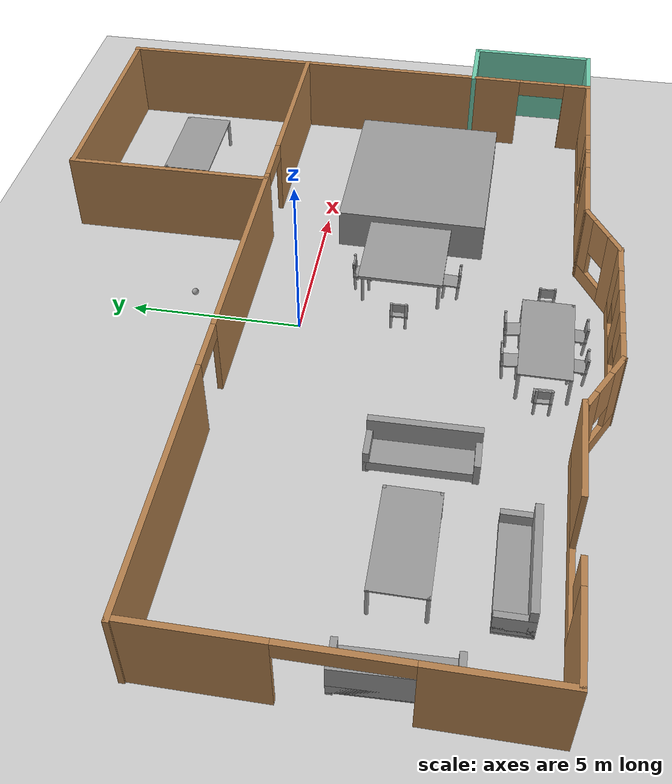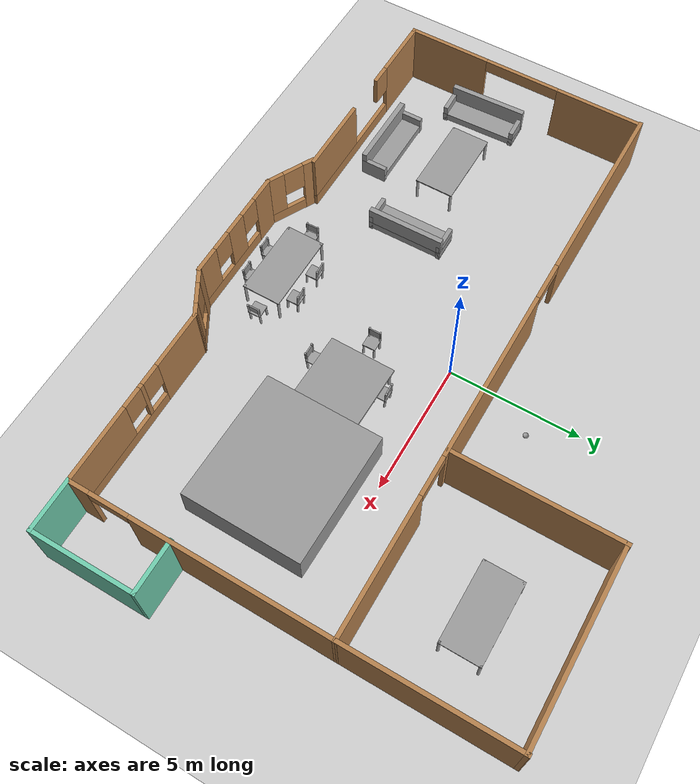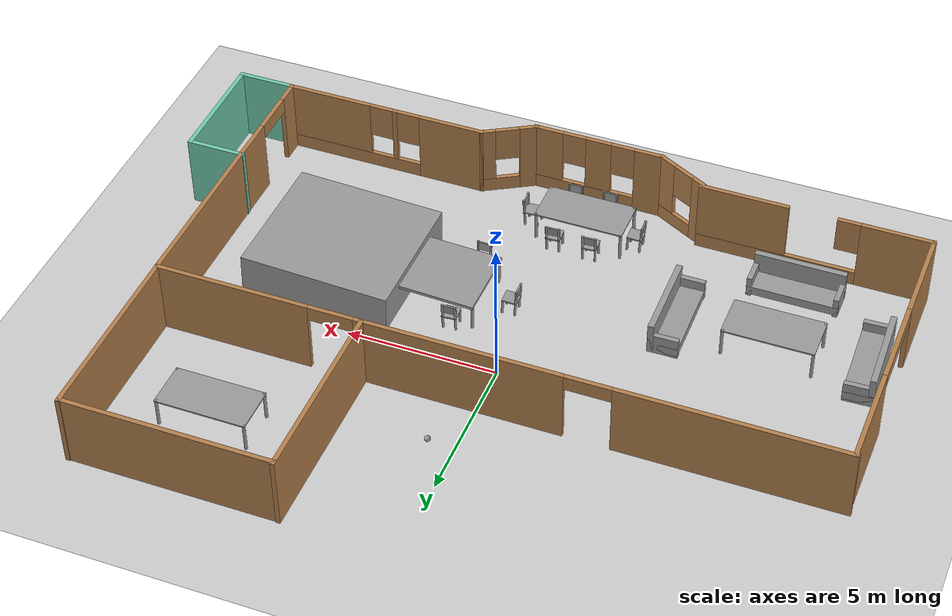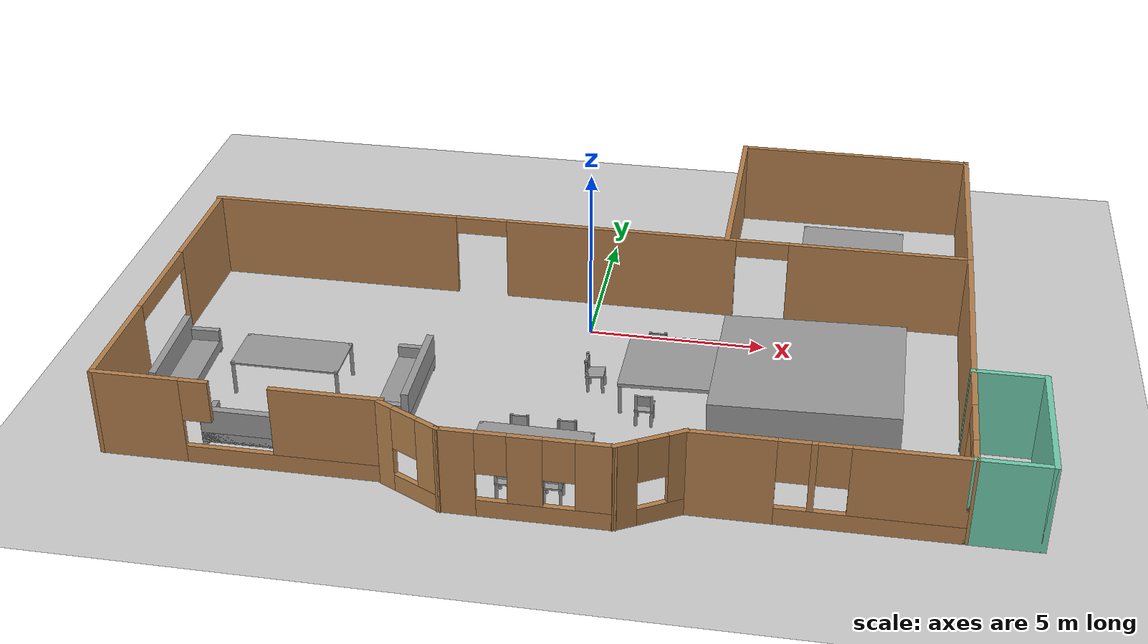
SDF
<sdf version="1.6">
 <world name="default">
  <plugin name="hello" filename="libhello.so"/>
  <light name="sun" type="directional">
   <pose>0 0 10 0 -0 0</pose>
   <diffuse>0.8 0.8 0.8 1</diffuse>
   <specular>0.2 0.2 0.2 1</specular>
   <attenuation>
    <range>1000</range>
    <constant>0.9</constant>
    <linear>0.01</linear>
    <quadratic>0.001</quadratic>
   </attenuation>
   <direction>-0.5 0.1 -0.9</direction>
  </light>
  <model name="ground_plane">
   <static>1</static>
   <link name="link">
    <collision name="collision">
     <geometry><plane><normal>0 0 1</normal><size>100 100</size></plane></geometry>
     <surface><friction><ode><mu>100</mu><mu2>50</mu2></ode></friction></surface>
    </collision>
    <visual name="visual">
     <cast_shadows>0</cast_shadows>
     <geometry><plane><normal>0 0 1</normal><size>100 100</size></plane></geometry>
     <material>
      <script><uri>file://media/materials/scripts/gazebo.material</uri><name>Gazebo/Grey</name></script>
     </material>
    </visual>
   </link>
  </model>
  <gravity>0 0 -9.8</gravity>
  <magnetic_field>6e-06 2.3e-05 -4.2e-05</magnetic_field>
  <atmosphere type="adiabatic"/>
  <physics name="default_physics" default="0" type="ode">
   <max_step_size>0.001</max_step_size>
   <real_time_factor>1</real_time_factor>
   <real_time_update_rate>1000</real_time_update_rate>
  </physics>
  <scene><ambient>0.4 0.4 0.4 1</ambient><background>0.7 0.7 0.7 1</background><shadows>1</shadows></scene>
  <spherical_coordinates>
   <surface_model>EARTH_WGS84</surface_model>
   <latitude_deg>0</latitude_deg>
   <longitude_deg>0</longitude_deg>
   <elevation>0</elevation>
   <heading_deg>0</heading_deg>
  </spherical_coordinates>
  <model name="myHouse">
   <pose>0.37474 -0.53824 0 0 -0 0</pose>
   <link name="Wall_10">
    <pose>2.44321 -7.87426 0 0 -0 0.523599</pose>
    <visual name="Wall_10_Visual_0">
     <pose>-0.672057 0 1.25 0 -0 0</pose>
     <geometry><box><size>0.655887 0.15 2.5</size></box></geometry>
     <material>
      <script><uri>file://media/materials/scripts/gazebo.material</uri><name>Gazebo/Wood</name></script>
      <ambient>0.784314 0.392157 0 1</ambient>
     </material>
     <meta><layer>0</layer></meta>
    </visual>
    <collision name="Wall_10_Collision_0">
     <geometry><box><size>0.655887 0.15 2.5</size></box></geometry>
     <pose>-0.672057 0 1.25 0 -0 0</pose>
    </collision>
    <visual name="Wall_10_Visual_1">
     <pose>0.327943 0 0.25 0 -0 0</pose>
     <geometry><box><size>1.34411 0.15 0.5</size></box></geometry>
     <material>
      <script><uri>file://media/materials/scripts/gazebo.material</uri><name>Gazebo/Wood</name></script>
      <ambient>0.784314 0.392157 0 1</ambient>
     </material>
     <meta><layer>0</layer></meta>
    </visual>
    <collision name="Wall_10_Collision_1">
     <geometry><box><size>1.34411 0.15 0.5</size></box></geometry>
     <pose>0.327943 0 0.25 0 -0 0</pose>
    </collision>
    <visual name="Wall_10_Visual_2">
     <pose>0.727943 0 1.5 0 -0 0</pose>
     <geometry><box><size>0.544113 0.15 2</size></box></geometry>
     <material>
      <script><uri>file://media/materials/scripts/gazebo.material</uri><name>Gazebo/Wood</name></script>
      <ambient>0.784314 0.392157 0 1</ambient>
     </material>
     <meta><layer>0</layer></meta>
    </visual>
    <collision name="Wall_10_Collision_2">
     <geometry><box><size>0.544113 0.15 2</size></box></geometry>
     <pose>0.727943 0 1.5 0 -0 0</pose>
    </collision>
    <visual name="Wall_10_Visual_3">
     <pose>0.055887 0 1.9 0 -0 0</pose>
     <geometry><box><size>0.8 0.15 1.2</size></box></geometry>
     <material>
      <script><uri>file://media/materials/scripts/gazebo.material</uri><name>Gazebo/Wood</name></script>
      <ambient>0.784314 0.392157 0 1</ambient>
     </material>
     <meta><layer>0</layer></meta>
    </visual>
    <collision name="Wall_10_Collision_3">
     <geometry><box><size>0.8 0.15 1.2</size></box></geometry>
     <pose>0.055887 0 1.9 0 -0 0</pose>
    </collision>
   </link>
   <link name="Wall_12">
    <pose>6.66929 -7.41176 0 0 -0 0</pose>
    <visual name="Wall_12_Visual_0">
     <pose>-2.36116 0 1.25 0 -0 0</pose>
     <geometry><box><size>2.27767 0.15 2.5</size></box></geometry>
     <material>
      <script><uri>file://media/materials/scripts/gazebo.material</uri><name>Gazebo/Wood</name></script>
      <ambient>0.784314 0.392157 0 1</ambient>
     </material>
     <meta><layer>0</layer></meta>
    </visual>
    <collision name="Wall_12_Collision_0">
     <geometry><box><size>2.27767 0.15 2.5</size></box></geometry>
     <pose>-2.36116 0 1.25 0 -0 0</pose>
    </collision>
    <visual name="Wall_12_Visual_1">
     <pose>1.13884 0 0.25 0 -0 0</pose>
     <geometry><box><size>4.72233 0.15 0.5</size></box></geometry>
     <material>
      <script><uri>file://media/materials/scripts/gazebo.material</uri><name>Gazebo/Wood</name></script>
      <ambient>0.784314 0.392157 0 1</ambient>
     </material>
     <meta><layer>0</layer></meta>
    </visual>
    <collision name="Wall_12_Collision_1">
     <geometry><box><size>4.72233 0.15 0.5</size></box></geometry>
     <pose>1.13884 0 0.25 0 -0 0</pose>
    </collision>
    <visual name="Wall_12_Visual_2">
     <pose>-0.341351 0 1.5 0 -0 0</pose>
     <geometry><box><size>0.161954 0.15 2</size></box></geometry>
     <material>
      <script><uri>file://media/materials/scripts/gazebo.material</uri><name>Gazebo/Wood</name></script>
      <ambient>0.784314 0.392157 0 1</ambient>
     </material>
     <meta><layer>0</layer></meta>
    </visual>
    <collision name="Wall_12_Collision_2">
     <geometry><box><size>0.161954 0.15 2</size></box></geometry>
     <pose>-0.341351 0 1.5 0 -0 0</pose>
    </collision>
    <visual name="Wall_12_Visual_3">
     <pose>2.01981 0 1.5 0 -0 0</pose>
     <geometry><box><size>2.96037 0.15 2</size></box></geometry>
     <material>
      <script><uri>file://media/materials/scripts/gazebo.material</uri><name>Gazebo/Wood</name></script>
      <ambient>0.784314 0.392157 0 1</ambient>
     </material>
     <meta><layer>0</layer></meta>
    </visual>
    <collision name="Wall_12_Collision_3">
     <geometry><box><size>2.96037 0.15 2</size></box></geometry>
     <pose>2.01981 0 1.5 0 -0 0</pose>
    </collision>
    <visual name="Wall_12_Visual_4">
     <pose>-0.822328 0 1.9 0 -0 0</pose>
     <geometry><box><size>0.8 0.15 1.2</size></box></geometry>
     <material>
      <script><uri>file://media/materials/scripts/gazebo.material</uri><name>Gazebo/Wood</name></script>
      <ambient>0.784314 0.392157 0 1</ambient>
     </material>
     <meta><layer>0</layer></meta>
    </visual>
    <collision name="Wall_12_Collision_4">
     <geometry><box><size>0.8 0.15 1.2</size></box></geometry>
     <pose>-0.822328 0 1.9 0 -0 0</pose>
    </collision>
    <visual name="Wall_12_Visual_5">
     <pose>0.139626 0 1.9 0 -0 0</pose>
     <geometry><box><size>0.8 0.15 1.2</size></box></geometry>
     <material>
      <script><uri>file://media/materials/scripts/gazebo.material</uri><name>Gazebo/Wood</name></script>
      <ambient>0.784314 0.392157 0 1</ambient>
     </material>
     <meta><layer>0</layer></meta>
    </visual>
    <collision name="Wall_12_Collision_5">
     <geometry><box><size>0.8 0.15 1.2</size></box></geometry>
     <pose>0.139626 0 1.9 0 -0 0</pose>
    </collision>
   </link>
   <link name="Wall_14">
    <pose>10.125 -2.58559 0 0 -0 1.56443</pose>
    <visual name="Wall_14_Visual_0">
     <pose>-4.46829 0 1.25 0 -0 0</pose>
     <geometry><box><size>0.866041 0.15 2.5</size></box></geometry>
     <material>
      <script><uri>file://media/materials/scripts/gazebo.material</uri><name>Gazebo/Wood</name></script>
      <ambient>0.784314 0.392157 0 1</ambient>
     </material>
     <meta><layer>0</layer></meta>
    </visual>
    <collision name="Wall_14_Collision_0">
     <geometry><box><size>0.866041 0.15 2.5</size></box></geometry>
     <pose>-4.46829 0 1.25 0 -0 0</pose>
    </collision>
    <visual name="Wall_14_Visual_1">
     <pose>1.18302 0 1.25 0 -0 0</pose>
     <geometry><box><size>7.43658 0.15 2.5</size></box></geometry>
     <material>
      <script><uri>file://media/materials/scripts/gazebo.material</uri><name>Gazebo/Wood</name></script>
      <ambient>0.784314 0.392157 0 1</ambient>
     </material>
     <meta><layer>0</layer></meta>
    </visual>
    <collision name="Wall_14_Collision_1">
     <geometry><box><size>7.43658 0.15 2.5</size></box></geometry>
     <pose>1.18302 0 1.25 0 -0 0</pose>
    </collision>
    <visual name="Wall_14_Visual_2">
     <pose>-3.28527 0 2.25 0 -0 0</pose>
     <geometry><box><size>1.5 0.15 0.5</size></box></geometry>
     <material>
      <script><uri>file://media/materials/scripts/gazebo.material</uri><name>Gazebo/Wood</name></script>
      <ambient>0.784314 0.392157 0 1</ambient>
     </material>
     <meta><layer>0</layer></meta>
    </visual>
    <collision name="Wall_14_Collision_2">
     <geometry><box><size>1.5 0.15 0.5</size></box></geometry>
     <pose>-3.28527 0 2.25 0 -0 0</pose>
    </collision>
   </link>
   <link name="Wall_15">
    <pose>-0.894285 2.22735 0 0 -0 3.14159</pose>
    <visual name="Wall_15_Visual_0">
     <pose>-8.54304 0 1.25 0 -0 0</pose>
     <geometry><box><size>5.16392 0.15 2.5</size></box></geometry>
     <material>
      <script><uri>file://media/materials/scripts/gazebo.material</uri><name>Gazebo/Wood</name></script>
      <ambient>0.784314 0.392157 0 1</ambient>
     </material>
     <meta><layer>0</layer></meta>
    </visual>
    <collision name="Wall_15_Collision_0">
     <geometry><box><size>5.16392 0.15 2.5</size></box></geometry>
     <pose>-8.54304 0 1.25 0 -0 0</pose>
    </collision>
    <visual name="Wall_15_Visual_1">
     <pose>-1.10091 0 1.25 0 -0 0</pose>
     <geometry><box><size>6.72033 0.15 2.5</size></box></geometry>
     <material>
      <script><uri>file://media/materials/scripts/gazebo.material</uri><name>Gazebo/Wood</name></script>
      <ambient>0.784314 0.392157 0 1</ambient>
     </material>
     <meta><layer>0</layer></meta>
    </visual>
    <collision name="Wall_15_Collision_1">
     <geometry><box><size>6.72033 0.15 2.5</size></box></geometry>
     <pose>-1.10091 0 1.25 0 -0 0</pose>
    </collision>
    <visual name="Wall_15_Visual_2">
     <pose>7.44213 0 1.25 0 -0 0</pose>
     <geometry><box><size>7.36575 0.15 2.5</size></box></geometry>
     <material>
      <script><uri>file://media/materials/scripts/gazebo.material</uri><name>Gazebo/Wood</name></script>
      <ambient>0.784314 0.392157 0 1</ambient>
     </material>
     <meta><layer>0</layer></meta>
    </visual>
    <collision name="Wall_15_Collision_2">
     <geometry><box><size>7.36575 0.15 2.5</size></box></geometry>
     <pose>7.44213 0 1.25 0 -0 0</pose>
    </collision>
    <visual name="Wall_15_Visual_3">
     <pose>-5.21108 0 2.25 0 -0 0</pose>
     <geometry><box><size>1.5 0.15 0.5</size></box></geometry>
     <material>
      <script><uri>file://media/materials/scripts/gazebo.material</uri><name>Gazebo/Wood</name></script>
      <ambient>0.784314 0.392157 0 1</ambient>
     </material>
     <meta><layer>0</layer></meta>
    </visual>
    <collision name="Wall_15_Collision_3">
     <geometry><box><size>1.5 0.15 0.5</size></box></geometry>
     <pose>-5.21108 0 2.25 0 -0 0</pose>
    </collision>
    <visual name="Wall_15_Visual_4">
     <pose>3.00925 0 2.25 0 -0 0</pose>
     <geometry><box><size>1.5 0.15 0.5</size></box></geometry>
     <material>
      <script><uri>file://media/materials/scripts/gazebo.material</uri><name>Gazebo/Wood</name></script>
      <ambient>0.784314 0.392157 0 1</ambient>
     </material>
     <meta><layer>0</layer></meta>
    </visual>
    <collision name="Wall_15_Collision_4">
     <geometry><box><size>1.5 0.15 0.5</size></box></geometry>
     <pose>3.00925 0 2.25 0 -0 0</pose>
    </collision>
   </link>
   <link name="Wall_18">
    <collision name="Wall_18_Collision">
     <geometry><box><size>6.25 0.15 2.5</size></box></geometry>
     <pose>0 0 1.25 0 -0 0</pose>
    </collision>
    <visual name="Wall_18_Visual">
     <pose>0 0 1.25 0 -0 0</pose>
     <geometry><box><size>6.25 0.15 2.5</size></box></geometry>
     <material>
      <script><uri>file://media/materials/scripts/gazebo.material</uri><name>Gazebo/Wood</name></script>
      <ambient>1 1 1 1</ambient>
     </material>
     <meta><layer>0</layer></meta>
    </visual>
    <pose>3.30252 5.31421 0 0 -0 1.5708</pose>
   </link>
   <link name="Wall_19">
    <collision name="Wall_19_Collision">
     <geometry><box><size>7 0.15 2.5</size></box></geometry>
     <pose>0 0 1.25 0 -0 0</pose>
    </collision>
    <visual name="Wall_19_Visual">
     <pose>0 0 1.25 0 -0 0</pose>
     <geometry><box><size>7 0.15 2.5</size></box></geometry>
     <material>
      <script><uri>file://media/materials/scripts/gazebo.material</uri><name>Gazebo/Wood</name></script>
      <ambient>1 1 1 1</ambient>
     </material>
     <meta><layer>0</layer></meta>
    </visual>
    <pose>6.72752 8.33761 0 0 -0 0</pose>
   </link>
   <link name="Wall_20">
    <collision name="Wall_20_Collision">
     <geometry><box><size>6.25 0.15 2.5</size></box></geometry>
     <pose>0 0 1.25 0 -0 0</pose>
    </collision>
    <visual name="Wall_20_Visual">
     <pose>0 0 1.25 0 -0 0</pose>
     <geometry><box><size>6.25 0.15 2.5</size></box></geometry>
     <material>
      <script><uri>file://media/materials/scripts/gazebo.material</uri><name>Gazebo/Wood</name></script>
      <ambient>1 1 1 1</ambient>
     </material>
     <meta><layer>0</layer></meta>
    </visual>
    <pose>10.1525 5.31421 0 0 0 -1.5708</pose>
   </link>
   <link name="Wall_22">
    <collision name="Wall_22_Collision">
     <geometry><box><size>2 0.15 2.5</size></box></geometry>
     <pose>0 0 1.25 0 -0 0</pose>
    </collision>
    <visual name="Wall_22_Visual">
     <pose>0 0 1.25 0 -0 0</pose>
     <geometry><box><size>2 0.15 2.5</size></box></geometry>
     <material>
      <script><uri>file://media/materials/scripts/gazebo.material</uri><name>Gazebo/Grey</name></script>
      <ambient>0.435294 0.796078 0.67451 1</ambient>
     </material>
     <meta><layer>0</layer></meta>
    </visual>
    <pose>11.0193 -7.41176 0 0 -0 0</pose>
   </link>
   <link name="Wall_23">
    <collision name="Wall_23_Collision">
     <geometry><box><size>4 0.15 2.5</size></box></geometry>
     <pose>0 0 1.25 0 -0 0</pose>
    </collision>
    <visual name="Wall_23_Visual">
     <pose>0 0 1.25 0 -0 0</pose>
     <geometry><box><size>4 0.15 2.5</size></box></geometry>
     <material>
      <script><uri>file://media/materials/scripts/gazebo.material</uri><name>Gazebo/Grey</name></script>
      <ambient>0.435294 0.796078 0.67451 1</ambient>
     </material>
     <meta><layer>0</layer></meta>
    </visual>
    <pose>11.9443 -5.48676 0 0 -0 1.5708</pose>
   </link>
   <link name="Wall_24">
    <collision name="Wall_24_Collision">
     <geometry><box><size>2 0.15 2.5</size></box></geometry>
     <pose>0 0 1.25 0 -0 0</pose>
    </collision>
    <visual name="Wall_24_Visual">
     <pose>0 0 1.25 0 -0 0</pose>
     <geometry><box><size>2 0.15 2.5</size></box></geometry>
     <material>
      <script><uri>file://media/materials/scripts/gazebo.material</uri><name>Gazebo/Grey</name></script>
      <ambient>0.435294 0.796078 0.67451 1</ambient>
     </material>
     <meta><layer>0</layer></meta>
    </visual>
    <pose>11.0193 -3.56175 0 0 -0 3.14159</pose>
   </link>
   <link name="Wall_4">
    <pose>-11.9025 -2.57962 0 0 0 -1.5708</pose>
    <visual name="Wall_4_Visual_0">
     <pose>-3.14855 0 1.25 0 -0 0</pose>
     <geometry><box><size>3.45289 0.15 2.5</size></box></geometry>
     <material>
      <script><uri>file://media/materials/scripts/gazebo.material</uri><name>Gazebo/Wood</name></script>
      <ambient>0.784314 0.392157 0 1</ambient>
     </material>
     <meta><layer>0</layer></meta>
    </visual>
    <collision name="Wall_4_Collision_0">
     <geometry><box><size>3.45289 0.15 2.5</size></box></geometry>
     <pose>-3.14855 0 1.25 0 -0 0</pose>
    </collision>
    <visual name="Wall_4_Visual_1">
     <pose>3.22645 0 1.25 0 -0 0</pose>
     <geometry><box><size>3.29711 0.15 2.5</size></box></geometry>
     <material>
      <script><uri>file://media/materials/scripts/gazebo.material</uri><name>Gazebo/Wood</name></script>
      <ambient>0.784314 0.392157 0 1</ambient>
     </material>
     <meta><layer>0</layer></meta>
    </visual>
    <collision name="Wall_4_Collision_1">
     <geometry><box><size>3.29711 0.15 2.5</size></box></geometry>
     <pose>3.22645 0 1.25 0 -0 0</pose>
    </collision>
    <visual name="Wall_4_Visual_2">
     <pose>0.077891 0 2.25 0 -0 0</pose>
     <geometry><box><size>3 0.15 0.5</size></box></geometry>
     <material>
      <script><uri>file://media/materials/scripts/gazebo.material</uri><name>Gazebo/Wood</name></script>
      <ambient>0.784314 0.392157 0 1</ambient>
     </material>
     <meta><layer>0</layer></meta>
    </visual>
    <collision name="Wall_4_Collision_2">
     <geometry><box><size>3 0.15 0.5</size></box></geometry>
     <pose>0.077891 0 2.25 0 -0 0</pose>
    </collision>
   </link>
   <link name="Wall_5">
    <pose>-8.10206 -7.38239 0 0 0 -0.000736</pose>
    <visual name="Wall_5_Visual_0">
     <pose>-2.66197 0 1.25 0 -0 0</pose>
     <geometry><box><size>2.35696 0.15 2.5</size></box></geometry>
     <material>
      <script><uri>file://media/materials/scripts/gazebo.material</uri><name>Gazebo/Wood</name></script>
      <ambient>0.784314 0.392157 0 1</ambient>
     </material>
     <meta><layer>0</layer></meta>
    </visual>
    <collision name="Wall_5_Collision_0">
     <geometry><box><size>2.35696 0.15 2.5</size></box></geometry>
     <pose>-2.66197 0 1.25 0 -0 0</pose>
    </collision>
    <visual name="Wall_5_Visual_1">
     <pose>1.17848 0 0.25 0 -0 0</pose>
     <geometry><box><size>5.32394 0.15 0.5</size></box></geometry>
     <material>
      <script><uri>file://media/materials/scripts/gazebo.material</uri><name>Gazebo/Wood</name></script>
      <ambient>0.784314 0.392157 0 1</ambient>
     </material>
     <meta><layer>0</layer></meta>
    </visual>
    <collision name="Wall_5_Collision_1">
     <geometry><box><size>5.32394 0.15 0.5</size></box></geometry>
     <pose>1.17848 0 0.25 0 -0 0</pose>
    </collision>
    <visual name="Wall_5_Visual_2">
     <pose>2.34696 0 1.5 0 -0 0</pose>
     <geometry><box><size>2.98698 0.15 2</size></box></geometry>
     <material>
      <script><uri>file://media/materials/scripts/gazebo.material</uri><name>Gazebo/Wood</name></script>
      <ambient>0.784314 0.392157 0 1</ambient>
     </material>
     <meta><layer>0</layer></meta>
    </visual>
    <collision name="Wall_5_Collision_2">
     <geometry><box><size>2.98698 0.15 2</size></box></geometry>
     <pose>2.34696 0 1.5 0 -0 0</pose>
    </collision>
    <visual name="Wall_5_Visual_3">
     <pose>-1.0993 0 1.9 0 -0 0</pose>
     <geometry><box><size>0.768378 0.15 1.2</size></box></geometry>
     <material>
      <script><uri>file://media/materials/scripts/gazebo.material</uri><name>Gazebo/Wood</name></script>
      <ambient>0.784314 0.392157 0 1</ambient>
     </material>
     <meta><layer>0</layer></meta>
    </visual>
    <collision name="Wall_5_Collision_3">
     <geometry><box><size>0.768378 0.15 1.2</size></box></geometry>
     <pose>-1.0993 0 1.9 0 -0 0</pose>
    </collision>
   </link>
   <link name="Wall_7">
    <pose>-3.53554 -7.90086 0 0 0 -0.484745</pose>
    <visual name="Wall_7_Visual_0">
     <pose>-0.754717 0 1.25 0 -0 0</pose>
     <geometry><box><size>0.51145 0.15 2.5</size></box></geometry>
     <material>
      <script><uri>file://media/materials/scripts/gazebo.material</uri><name>Gazebo/Wood</name></script>
      <ambient>0.784314 0.392157 0 1</ambient>
     </material>
     <meta><layer>0</layer></meta>
    </visual>
    <collision name="Wall_7_Collision_0">
     <geometry><box><size>0.51145 0.15 2.5</size></box></geometry>
     <pose>-0.754717 0 1.25 0 -0 0</pose>
    </collision>
    <visual name="Wall_7_Visual_1">
     <pose>0.255725 0 0.25 0 -0 0</pose>
     <geometry><box><size>1.50943 0.15 0.5</size></box></geometry>
     <material>
      <script><uri>file://media/materials/scripts/gazebo.material</uri><name>Gazebo/Wood</name></script>
      <ambient>0.784314 0.392157 0 1</ambient>
     </material>
     <meta><layer>0</layer></meta>
    </visual>
    <collision name="Wall_7_Collision_1">
     <geometry><box><size>1.50943 0.15 0.5</size></box></geometry>
     <pose>0.255725 0 0.25 0 -0 0</pose>
    </collision>
    <visual name="Wall_7_Visual_2">
     <pose>0.655725 0 1.5 0 -0 0</pose>
     <geometry><box><size>0.709434 0.15 2</size></box></geometry>
     <material>
      <script><uri>file://media/materials/scripts/gazebo.material</uri><name>Gazebo/Wood</name></script>
      <ambient>0.784314 0.392157 0 1</ambient>
     </material>
     <meta><layer>0</layer></meta>
    </visual>
    <collision name="Wall_7_Collision_2">
     <geometry><box><size>0.709434 0.15 2</size></box></geometry>
     <pose>0.655725 0 1.5 0 -0 0</pose>
    </collision>
    <visual name="Wall_7_Visual_3">
     <pose>-0.098992 0 1.9 0 -0 0</pose>
     <geometry><box><size>0.8 0.15 1.2</size></box></geometry>
     <material>
      <script><uri>file://media/materials/scripts/gazebo.material</uri><name>Gazebo/Wood</name></script>
      <ambient>0.784314 0.392157 0 1</ambient>
     </material>
     <meta><layer>0</layer></meta>
    </visual>
    <collision name="Wall_7_Collision_3">
     <geometry><box><size>0.8 0.15 1.2</size></box></geometry>
     <pose>-0.098992 0 1.9 0 -0 0</pose>
    </collision>
   </link>
   <link name="Wall_8">
    <pose>-0.532862 -8.33676 0 0 -0 0</pose>
    <visual name="Wall_8_Visual_0">
     <pose>-1.74679 0 1.25 0 -0 0</pose>
     <geometry><box><size>1.00642 0.15 2.5</size></box></geometry>
     <material>
      <script><uri>file://media/materials/scripts/gazebo.material</uri><name>Gazebo/Wood</name></script>
      <ambient>0.784314 0.392157 0 1</ambient>
     </material>
     <meta><layer>0</layer></meta>
    </visual>
    <collision name="Wall_8_Collision_0">
     <geometry><box><size>1.00642 0.15 2.5</size></box></geometry>
     <pose>-1.74679 0 1.25 0 -0 0</pose>
    </collision>
    <visual name="Wall_8_Visual_1">
     <pose>0.503212 0 0.25 0 -0 0</pose>
     <geometry><box><size>3.49358 0.15 0.5</size></box></geometry>
     <material>
      <script><uri>file://media/materials/scripts/gazebo.material</uri><name>Gazebo/Wood</name></script>
      <ambient>0.784314 0.392157 0 1</ambient>
     </material>
     <meta><layer>0</layer></meta>
    </visual>
    <collision name="Wall_8_Collision_1">
     <geometry><box><size>3.49358 0.15 0.5</size></box></geometry>
     <pose>0.503212 0 0.25 0 -0 0</pose>
    </collision>
    <visual name="Wall_8_Visual_2">
     <pose>-0.004053 0 1.5 0 -0 0</pose>
     <geometry><box><size>0.879046 0.15 2</size></box></geometry>
     <material>
      <script><uri>file://media/materials/scripts/gazebo.material</uri><name>Gazebo/Wood</name></script>
      <ambient>0.784314 0.392157 0 1</ambient>
     </material>
     <meta><layer>0</layer></meta>
    </visual>
    <collision name="Wall_8_Collision_2">
     <geometry><box><size>0.879046 0.15 2</size></box></geometry>
     <pose>-0.004053 0 1.5 0 -0 0</pose>
    </collision>
    <visual name="Wall_8_Visual_3">
     <pose>1.74273 0 1.5 0 -0 0</pose>
     <geometry><box><size>1.01453 0.15 2</size></box></geometry>
     <material>
      <script><uri>file://media/materials/scripts/gazebo.material</uri><name>Gazebo/Wood</name></script>
      <ambient>0.784314 0.392157 0 1</ambient>
     </material>
     <meta><layer>0</layer></meta>
    </visual>
    <collision name="Wall_8_Collision_3">
     <geometry><box><size>1.01453 0.15 2</size></box></geometry>
     <pose>1.74273 0 1.5 0 -0 0</pose>
    </collision>
    <visual name="Wall_8_Visual_4">
     <pose>-0.843576 0 1.9 0 -0 0</pose>
     <geometry><box><size>0.8 0.15 1.2</size></box></geometry>
     <material>
      <script><uri>file://media/materials/scripts/gazebo.material</uri><name>Gazebo/Wood</name></script>
      <ambient>0.784314 0.392157 0 1</ambient>
     </material>
     <meta><layer>0</layer></meta>
    </visual>
    <collision name="Wall_8_Collision_4">
     <geometry><box><size>0.8 0.15 1.2</size></box></geometry>
     <pose>-0.843576 0 1.9 0 -0 0</pose>
    </collision>
    <visual name="Wall_8_Visual_5">
     <pose>0.83547 0 1.9 0 -0 0</pose>
     <geometry><box><size>0.8 0.15 1.2</size></box></geometry>
     <material>
      <script><uri>file://media/materials/scripts/gazebo.material</uri><name>Gazebo/Wood</name></script>
      <ambient>0.784314 0.392157 0 1</ambient>
     </material>
     <meta><layer>0</layer></meta>
    </visual>
    <collision name="Wall_8_Collision_5">
     <geometry><box><size>0.8 0.15 1.2</size></box></geometry>
     <pose>0.83547 0 1.9 0 -0 0</pose>
    </collision>
   </link>
   <static>1</static>
  </model>
  <model name="diningTable">
   <link name="link_0">
    <pose>-1.45 -0.7 -0.015 0 -0 0</pose>
    <inertial>
     <mass>1</mass>
     <inertia><ixx>0.145833</ixx><ixy>0</ixy><ixz>0</ixz><iyy>0.145833</iyy><iyz>0</iyz><izz>0.125</izz></inertia>
    </inertial>
    <visual name="visual">
     <geometry><cylinder><radius>0.05</radius><length>1</length></cylinder></geometry>
     <material>
      <lighting>1</lighting>
      <script><uri>file://media/materials/scripts/gazebo.material</uri><name>Gazebo/Grey</name></script>
      <shader type="pixel"><normal_map>__default__</normal_map></shader>
      <ambient>0.3 0.3 0.3 1</ambient>
      <diffuse>0.7 0.7 0.7 1</diffuse>
      <specular>0.01 0.01 0.01 1</specular>
      <emissive>0 0 0 1</emissive>
     </material>
    </visual>
    <collision name="collision">
     <geometry><cylinder><radius>0.05</radius><length>1</length></cylinder></geometry>
     <surface>
      <friction>
       <ode><mu>1</mu><mu2>1</mu2><fdir1>0 0 0</fdir1><slip1>0</slip1><slip2>0</slip2></ode>
       <torsional>
        <coefficient>1</coefficient>
        <patch_radius>0</patch_radius>
        <surface_radius>0</surface_radius>
        <use_patch_radius>1</use_patch_radius>
        <ode><slip>0</slip></ode>
       </torsional>
      </friction>
      <bounce><restitution_coefficient>0</restitution_coefficient><threshold>1e+06</threshold></bounce>
      <contact>
       <collide_without_contact>0</collide_without_contact>
       <collide_without_contact_bitmask>1</collide_without_contact_bitmask>
       <collide_bitmask>1</collide_bitmask>
       <ode>
        <soft_cfm>0</soft_cfm>
        <soft_erp>0.2</soft_erp>
        <kp>1e+13</kp>
        <kd>1</kd>
        <max_vel>0.01</max_vel>
        <min_depth>0</min_depth>
       </ode>
       <bullet>
        <split_impulse>1</split_impulse>
        <split_impulse_penetration_threshold>-0.01</split_impulse_penetration_threshold>
        <soft_cfm>0</soft_cfm>
        <soft_erp>0.2</soft_erp>
        <kp>1e+13</kp>
        <kd>1</kd>
       </bullet>
      </contact>
     </surface>
    </collision>
   </link>
   <link name="link_0_clone">
    <pose>1.45 0.7 -0.015 0 -0 0</pose>
    <inertial>
     <mass>1</mass>
     <inertia><ixx>0.145833</ixx><ixy>0</ixy><ixz>0</ixz><iyy>0.145833</iyy><iyz>0</iyz><izz>0.125</izz></inertia>
    </inertial>
    <visual name="visual">
     <geometry><cylinder><radius>0.05</radius><length>1</length></cylinder></geometry>
     <material>
      <lighting>1</lighting>
      <script><uri>file://media/materials/scripts/gazebo.material</uri><name>Gazebo/Grey</name></script>
      <shader type="pixel"><normal_map>__default__</normal_map></shader>
      <ambient>0.3 0.3 0.3 1</ambient>
      <diffuse>0.7 0.7 0.7 1</diffuse>
      <specular>0.01 0.01 0.01 1</specular>
      <emissive>0 0 0 1</emissive>
     </material>
    </visual>
    <collision name="collision">
     <geometry><cylinder><radius>0.05</radius><length>1</length></cylinder></geometry>
     <surface>
      <friction>
       <ode><mu>1</mu><mu2>1</mu2><fdir1>0 0 0</fdir1><slip1>0</slip1><slip2>0</slip2></ode>
       <torsional>
        <coefficient>1</coefficient>
        <patch_radius>0</patch_radius>
        <surface_radius>0</surface_radius>
        <use_patch_radius>1</use_patch_radius>
        <ode><slip>0</slip></ode>
       </torsional>
      </friction>
      <bounce><restitution_coefficient>0</restitution_coefficient><threshold>1e+06</threshold></bounce>
      <contact>
       <collide_without_contact>0</collide_without_contact>
       <collide_without_contact_bitmask>1</collide_without_contact_bitmask>
       <collide_bitmask>1</collide_bitmask>
       <ode>
        <soft_cfm>0</soft_cfm>
        <soft_erp>0.2</soft_erp>
        <kp>1e+13</kp>
        <kd>1</kd>
        <max_vel>0.01</max_vel>
        <min_depth>0</min_depth>
       </ode>
       <bullet>
        <split_impulse>1</split_impulse>
        <split_impulse_penetration_threshold>-0.01</split_impulse_penetration_threshold>
        <soft_cfm>0</soft_cfm>
        <soft_erp>0.2</soft_erp>
        <kp>1e+13</kp>
        <kd>1</kd>
       </bullet>
      </contact>
     </surface>
    </collision>
   </link>
   <link name="link_0_clone_0">
    <pose>1.45 -0.7 -0.015 0 -0 0</pose>
    <inertial>
     <mass>1</mass>
     <inertia><ixx>0.145833</ixx><ixy>0</ixy><ixz>0</ixz><iyy>0.145833</iyy><iyz>0</iyz><izz>0.125</izz></inertia>
    </inertial>
    <visual name="visual">
     <geometry><cylinder><radius>0.05</radius><length>1</length></cylinder></geometry>
     <material>
      <lighting>1</lighting>
      <script><uri>file://media/materials/scripts/gazebo.material</uri><name>Gazebo/Grey</name></script>
      <shader type="pixel"><normal_map>__default__</normal_map></shader>
      <ambient>0.3 0.3 0.3 1</ambient>
      <diffuse>0.7 0.7 0.7 1</diffuse>
      <specular>0.01 0.01 0.01 1</specular>
      <emissive>0 0 0 1</emissive>
     </material>
    </visual>
    <collision name="collision">
     <geometry><cylinder><radius>0.05</radius><length>1</length></cylinder></geometry>
     <surface>
      <friction>
       <ode><mu>1</mu><mu2>1</mu2><fdir1>0 0 0</fdir1><slip1>0</slip1><slip2>0</slip2></ode>
       <torsional>
        <coefficient>1</coefficient>
        <patch_radius>0</patch_radius>
        <surface_radius>0</surface_radius>
        <use_patch_radius>1</use_patch_radius>
        <ode><slip>0</slip></ode>
       </torsional>
      </friction>
      <bounce><restitution_coefficient>0</restitution_coefficient><threshold>1e+06</threshold></bounce>
      <contact>
       <collide_without_contact>0</collide_without_contact>
       <collide_without_contact_bitmask>1</collide_without_contact_bitmask>
       <collide_bitmask>1</collide_bitmask>
       <ode>
        <soft_cfm>0</soft_cfm>
        <soft_erp>0.2</soft_erp>
        <kp>1e+13</kp>
        <kd>1</kd>
        <max_vel>0.01</max_vel>
        <min_depth>0</min_depth>
       </ode>
       <bullet>
        <split_impulse>1</split_impulse>
        <split_impulse_penetration_threshold>-0.01</split_impulse_penetration_threshold>
        <soft_cfm>0</soft_cfm>
        <soft_erp>0.2</soft_erp>
        <kp>1e+13</kp>
        <kd>1</kd>
       </bullet>
      </contact>
     </surface>
    </collision>
   </link>
   <link name="link_0_clone_1">
    <pose>-1.45 0.7 -0.015 0 -0 0</pose>
    <inertial>
     <mass>1</mass>
     <inertia><ixx>0.145833</ixx><ixy>0</ixy><ixz>0</ixz><iyy>0.145833</iyy><iyz>0</iyz><izz>0.125</izz></inertia>
    </inertial>
    <visual name="visual">
     <geometry><cylinder><radius>0.05</radius><length>1</length></cylinder></geometry>
     <material>
      <lighting>1</lighting>
      <script><uri>file://media/materials/scripts/gazebo.material</uri><name>Gazebo/Grey</name></script>
      <shader type="pixel"><normal_map>__default__</normal_map></shader>
      <ambient>0.3 0.3 0.3 1</ambient>
      <diffuse>0.7 0.7 0.7 1</diffuse>
      <specular>0.01 0.01 0.01 1</specular>
      <emissive>0 0 0 1</emissive>
     </material>
    </visual>
    <collision name="collision">
     <geometry><cylinder><radius>0.05</radius><length>1</length></cylinder></geometry>
     <surface>
      <friction>
       <ode><mu>1</mu><mu2>1</mu2><fdir1>0 0 0</fdir1><slip1>0</slip1><slip2>0</slip2></ode>
       <torsional>
        <coefficient>1</coefficient>
        <patch_radius>0</patch_radius>
        <surface_radius>0</surface_radius>
        <use_patch_radius>1</use_patch_radius>
        <ode><slip>0</slip></ode>
       </torsional>
      </friction>
      <bounce><restitution_coefficient>0</restitution_coefficient><threshold>1e+06</threshold></bounce>
      <contact>
       <collide_without_contact>0</collide_without_contact>
       <collide_without_contact_bitmask>1</collide_without_contact_bitmask>
       <collide_bitmask>1</collide_bitmask>
       <ode>
        <soft_cfm>0</soft_cfm>
        <soft_erp>0.2</soft_erp>
        <kp>1e+13</kp>
        <kd>1</kd>
        <max_vel>0.01</max_vel>
        <min_depth>0</min_depth>
       </ode>
       <bullet>
        <split_impulse>1</split_impulse>
        <split_impulse_penetration_threshold>-0.01</split_impulse_penetration_threshold>
        <soft_cfm>0</soft_cfm>
        <soft_erp>0.2</soft_erp>
        <kp>1e+13</kp>
        <kd>1</kd>
       </bullet>
      </contact>
     </surface>
    </collision>
   </link>
   <link name="link_1">
    <pose>-0 -0 0.06 0 -0 0</pose>
    <inertial>
     <mass>1</mass>
     <inertia>
      <ixx>0.166667</ixx>
      <ixy>0</ixy>
      <ixz>0</ixz>
      <iyy>0.166667</iyy>
      <iyz>0</iyz>
      <izz>0.166667</izz>
     </inertia>
    </inertial>
    <visual name="visual">
     <pose>0 0 0.4 0 -0 0</pose>
     <geometry><box><size>3 1.5 0.05</size></box></geometry>
     <material>
      <lighting>1</lighting>
      <script><uri>file://media/materials/scripts/gazebo.material</uri><name>Gazebo/Grey</name></script>
      <shader type="pixel"><normal_map>__default__</normal_map></shader>
      <ambient>0.3 0.3 0.3 1</ambient>
      <diffuse>0.7 0.7 0.7 1</diffuse>
      <specular>0.01 0.01 0.01 1</specular>
      <emissive>0 0 0 1</emissive>
     </material>
    </visual>
    <collision name="collision">
     <pose>0 0 0.4 0 -0 0</pose>
     <geometry><box><size>3 1.5 0.05</size></box></geometry>
     <surface>
      <friction>
       <ode><mu>1</mu><mu2>1</mu2><fdir1>0 0 0</fdir1><slip1>0</slip1><slip2>0</slip2></ode>
       <torsional>
        <coefficient>1</coefficient>
        <patch_radius>0</patch_radius>
        <surface_radius>0</surface_radius>
        <use_patch_radius>1</use_patch_radius>
        <ode><slip>0</slip></ode>
       </torsional>
      </friction>
      <bounce><restitution_coefficient>0</restitution_coefficient><threshold>1e+06</threshold></bounce>
      <contact>
       <collide_without_contact>0</collide_without_contact>
       <collide_without_contact_bitmask>1</collide_without_contact_bitmask>
       <collide_bitmask>1</collide_bitmask>
       <ode>
        <soft_cfm>0</soft_cfm>
        <soft_erp>0.2</soft_erp>
        <kp>1e+13</kp>
        <kd>1</kd>
        <max_vel>0.01</max_vel>
        <min_depth>0</min_depth>
       </ode>
       <bullet>
        <split_impulse>1</split_impulse>
        <split_impulse_penetration_threshold>-0.01</split_impulse_penetration_threshold>
        <soft_cfm>0</soft_cfm>
        <soft_erp>0.2</soft_erp>
        <kp>1e+13</kp>
        <kd>1</kd>
       </bullet>
      </contact>
     </surface>
    </collision>
   </link>
   <joint name="link_1_JOINT_4" type="fixed">
    <parent>link_1</parent>
    <child>link_0_clone</child>
    <physics>
     <ode><limit><cfm>0</cfm><erp>0.2</erp></limit><suspension><cfm>0</cfm><erp>0.2</erp></suspension></ode>
    </physics>
   </joint>
   <joint name="link_1_JOINT_5" type="revolute">
    <parent>link_1</parent>
    <child>link_0_clone_0</child>
    <axis>
     <xyz>1 0 0</xyz>
     <use_parent_model_frame>0</use_parent_model_frame>
     <limit>
      <lower>-1.79769e+308</lower>
      <upper>1.79769e+308</upper>
      <effort>-1</effort>
      <velocity>-1</velocity>
     </limit>
     <dynamics>
      <spring_reference>0</spring_reference>
      <spring_stiffness>0</spring_stiffness>
      <damping>0</damping>
     </dynamics>
    </axis>
    <physics>
     <ode><limit><cfm>0</cfm><erp>0.2</erp></limit><suspension><cfm>0</cfm><erp>0.2</erp></suspension></ode>
    </physics>
   </joint>
   <joint name="link_1_JOINT_6" type="fixed">
    <parent>link_1</parent>
    <child>link_0_clone_1</child>
    <physics>
     <ode><limit><cfm>0</cfm><erp>0.2</erp></limit><suspension><cfm>0</cfm><erp>0.2</erp></suspension></ode>
    </physics>
   </joint>
   <joint name="link_1_JOINT_7" type="fixed">
    <parent>link_1</parent>
    <child>link_0</child>
    <physics>
     <ode><limit><cfm>0</cfm><erp>0.2</erp></limit><suspension><cfm>0</cfm><erp>0.2</erp></suspension></ode>
    </physics>
   </joint>
   <static>0</static>
   <pose>7.25961 4.89414 0.514998 0 -2e-06 -0.002647</pose>
  </model>
  <model name="diningTable_0">
   <link name="link_0">
    <pose>-1.45 -0.7 -0.015 0 -0 0</pose>
    <inertial>
     <mass>1</mass>
     <inertia><ixx>0.145833</ixx><ixy>0</ixy><ixz>0</ixz><iyy>0.145833</iyy><iyz>0</iyz><izz>0.125</izz></inertia>
    </inertial>
    <visual name="visual">
     <geometry><cylinder><radius>0.05</radius><length>1</length></cylinder></geometry>
     <material>
      <lighting>1</lighting>
      <script><uri>file://media/materials/scripts/gazebo.material</uri><name>Gazebo/Grey</name></script>
      <shader type="pixel"><normal_map>__default__</normal_map></shader>
      <ambient>0.3 0.3 0.3 1</ambient>
      <diffuse>0.7 0.7 0.7 1</diffuse>
      <specular>0.01 0.01 0.01 1</specular>
      <emissive>0 0 0 1</emissive>
     </material>
    </visual>
    <collision name="collision">
     <geometry><cylinder><radius>0.05</radius><length>1</length></cylinder></geometry>
     <surface>
      <friction>
       <ode><mu>1</mu><mu2>1</mu2><fdir1>0 0 0</fdir1><slip1>0</slip1><slip2>0</slip2></ode>
       <torsional>
        <coefficient>1</coefficient>
        <patch_radius>0</patch_radius>
        <surface_radius>0</surface_radius>
        <use_patch_radius>1</use_patch_radius>
        <ode><slip>0</slip></ode>
       </torsional>
      </friction>
      <bounce><restitution_coefficient>0</restitution_coefficient><threshold>1e+06</threshold></bounce>
      <contact>
       <collide_without_contact>0</collide_without_contact>
       <collide_without_contact_bitmask>1</collide_without_contact_bitmask>
       <collide_bitmask>1</collide_bitmask>
       <ode>
        <soft_cfm>0</soft_cfm>
        <soft_erp>0.2</soft_erp>
        <kp>1e+13</kp>
        <kd>1</kd>
        <max_vel>0.01</max_vel>
        <min_depth>0</min_depth>
       </ode>
       <bullet>
        <split_impulse>1</split_impulse>
        <split_impulse_penetration_threshold>-0.01</split_impulse_penetration_threshold>
        <soft_cfm>0</soft_cfm>
        <soft_erp>0.2</soft_erp>
        <kp>1e+13</kp>
        <kd>1</kd>
       </bullet>
      </contact>
     </surface>
    </collision>
   </link>
   <link name="link_0_clone">
    <pose>1.45 0.7 -0.015 0 -0 0</pose>
    <inertial>
     <mass>1</mass>
     <inertia><ixx>0.145833</ixx><ixy>0</ixy><ixz>0</ixz><iyy>0.145833</iyy><iyz>0</iyz><izz>0.125</izz></inertia>
    </inertial>
    <visual name="visual">
     <geometry><cylinder><radius>0.05</radius><length>1</length></cylinder></geometry>
     <material>
      <lighting>1</lighting>
      <script><uri>file://media/materials/scripts/gazebo.material</uri><name>Gazebo/Grey</name></script>
      <shader type="pixel"><normal_map>__default__</normal_map></shader>
      <ambient>0.3 0.3 0.3 1</ambient>
      <diffuse>0.7 0.7 0.7 1</diffuse>
      <specular>0.01 0.01 0.01 1</specular>
      <emissive>0 0 0 1</emissive>
     </material>
    </visual>
    <collision name="collision">
     <geometry><cylinder><radius>0.05</radius><length>1</length></cylinder></geometry>
     <surface>
      <friction>
       <ode><mu>1</mu><mu2>1</mu2><fdir1>0 0 0</fdir1><slip1>0</slip1><slip2>0</slip2></ode>
       <torsional>
        <coefficient>1</coefficient>
        <patch_radius>0</patch_radius>
        <surface_radius>0</surface_radius>
        <use_patch_radius>1</use_patch_radius>
        <ode><slip>0</slip></ode>
       </torsional>
      </friction>
      <bounce><restitution_coefficient>0</restitution_coefficient><threshold>1e+06</threshold></bounce>
      <contact>
       <collide_without_contact>0</collide_without_contact>
       <collide_without_contact_bitmask>1</collide_without_contact_bitmask>
       <collide_bitmask>1</collide_bitmask>
       <ode>
        <soft_cfm>0</soft_cfm>
        <soft_erp>0.2</soft_erp>
        <kp>1e+13</kp>
        <kd>1</kd>
        <max_vel>0.01</max_vel>
        <min_depth>0</min_depth>
       </ode>
       <bullet>
        <split_impulse>1</split_impulse>
        <split_impulse_penetration_threshold>-0.01</split_impulse_penetration_threshold>
        <soft_cfm>0</soft_cfm>
        <soft_erp>0.2</soft_erp>
        <kp>1e+13</kp>
        <kd>1</kd>
       </bullet>
      </contact>
     </surface>
    </collision>
   </link>
   <link name="link_0_clone_0">
    <pose>1.45 -0.7 -0.015 0 -0 0</pose>
    <inertial>
     <mass>1</mass>
     <inertia><ixx>0.145833</ixx><ixy>0</ixy><ixz>0</ixz><iyy>0.145833</iyy><iyz>0</iyz><izz>0.125</izz></inertia>
    </inertial>
    <visual name="visual">
     <geometry><cylinder><radius>0.05</radius><length>1</length></cylinder></geometry>
     <material>
      <lighting>1</lighting>
      <script><uri>file://media/materials/scripts/gazebo.material</uri><name>Gazebo/Grey</name></script>
      <shader type="pixel"><normal_map>__default__</normal_map></shader>
      <ambient>0.3 0.3 0.3 1</ambient>
      <diffuse>0.7 0.7 0.7 1</diffuse>
      <specular>0.01 0.01 0.01 1</specular>
      <emissive>0 0 0 1</emissive>
     </material>
    </visual>
    <collision name="collision">
     <geometry><cylinder><radius>0.05</radius><length>1</length></cylinder></geometry>
     <surface>
      <friction>
       <ode><mu>1</mu><mu2>1</mu2><fdir1>0 0 0</fdir1><slip1>0</slip1><slip2>0</slip2></ode>
       <torsional>
        <coefficient>1</coefficient>
        <patch_radius>0</patch_radius>
        <surface_radius>0</surface_radius>
        <use_patch_radius>1</use_patch_radius>
        <ode><slip>0</slip></ode>
       </torsional>
      </friction>
      <bounce><restitution_coefficient>0</restitution_coefficient><threshold>1e+06</threshold></bounce>
      <contact>
       <collide_without_contact>0</collide_without_contact>
       <collide_without_contact_bitmask>1</collide_without_contact_bitmask>
       <collide_bitmask>1</collide_bitmask>
       <ode>
        <soft_cfm>0</soft_cfm>
        <soft_erp>0.2</soft_erp>
        <kp>1e+13</kp>
        <kd>1</kd>
        <max_vel>0.01</max_vel>
        <min_depth>0</min_depth>
       </ode>
       <bullet>
        <split_impulse>1</split_impulse>
        <split_impulse_penetration_threshold>-0.01</split_impulse_penetration_threshold>
        <soft_cfm>0</soft_cfm>
        <soft_erp>0.2</soft_erp>
        <kp>1e+13</kp>
        <kd>1</kd>
       </bullet>
      </contact>
     </surface>
    </collision>
   </link>
   <link name="link_0_clone_1">
    <pose>-1.45 0.7 -0.015 0 -0 0</pose>
    <inertial>
     <mass>1</mass>
     <inertia><ixx>0.145833</ixx><ixy>0</ixy><ixz>0</ixz><iyy>0.145833</iyy><iyz>0</iyz><izz>0.125</izz></inertia>
    </inertial>
    <visual name="visual">
     <geometry><cylinder><radius>0.05</radius><length>1</length></cylinder></geometry>
     <material>
      <lighting>1</lighting>
      <script><uri>file://media/materials/scripts/gazebo.material</uri><name>Gazebo/Grey</name></script>
      <shader type="pixel"><normal_map>__default__</normal_map></shader>
      <ambient>0.3 0.3 0.3 1</ambient>
      <diffuse>0.7 0.7 0.7 1</diffuse>
      <specular>0.01 0.01 0.01 1</specular>
      <emissive>0 0 0 1</emissive>
     </material>
    </visual>
    <collision name="collision">
     <geometry><cylinder><radius>0.05</radius><length>1</length></cylinder></geometry>
     <surface>
      <friction>
       <ode><mu>1</mu><mu2>1</mu2><fdir1>0 0 0</fdir1><slip1>0</slip1><slip2>0</slip2></ode>
       <torsional>
        <coefficient>1</coefficient>
        <patch_radius>0</patch_radius>
        <surface_radius>0</surface_radius>
        <use_patch_radius>1</use_patch_radius>
        <ode><slip>0</slip></ode>
       </torsional>
      </friction>
      <bounce><restitution_coefficient>0</restitution_coefficient><threshold>1e+06</threshold></bounce>
      <contact>
       <collide_without_contact>0</collide_without_contact>
       <collide_without_contact_bitmask>1</collide_without_contact_bitmask>
       <collide_bitmask>1</collide_bitmask>
       <ode>
        <soft_cfm>0</soft_cfm>
        <soft_erp>0.2</soft_erp>
        <kp>1e+13</kp>
        <kd>1</kd>
        <max_vel>0.01</max_vel>
        <min_depth>0</min_depth>
       </ode>
       <bullet>
        <split_impulse>1</split_impulse>
        <split_impulse_penetration_threshold>-0.01</split_impulse_penetration_threshold>
        <soft_cfm>0</soft_cfm>
        <soft_erp>0.2</soft_erp>
        <kp>1e+13</kp>
        <kd>1</kd>
       </bullet>
      </contact>
     </surface>
    </collision>
   </link>
   <link name="link_1">
    <pose>-0 -0 0.06 0 -0 0</pose>
    <inertial>
     <mass>1</mass>
     <inertia>
      <ixx>0.166667</ixx>
      <ixy>0</ixy>
      <ixz>0</ixz>
      <iyy>0.166667</iyy>
      <iyz>0</iyz>
      <izz>0.166667</izz>
     </inertia>
    </inertial>
    <visual name="visual">
     <pose>0 0 0.4 0 -0 0</pose>
     <geometry><box><size>3 1.5 0.05</size></box></geometry>
     <material>
      <lighting>1</lighting>
      <script><uri>file://media/materials/scripts/gazebo.material</uri><name>Gazebo/Grey</name></script>
      <shader type="pixel"><normal_map>__default__</normal_map></shader>
      <ambient>0.3 0.3 0.3 1</ambient>
      <diffuse>0.7 0.7 0.7 1</diffuse>
      <specular>0.01 0.01 0.01 1</specular>
      <emissive>0 0 0 1</emissive>
     </material>
    </visual>
    <collision name="collision">
     <pose>0 0 0.4 0 -0 0</pose>
     <geometry><box><size>3 1.5 0.05</size></box></geometry>
     <surface>
      <friction>
       <ode><mu>1</mu><mu2>1</mu2><fdir1>0 0 0</fdir1><slip1>0</slip1><slip2>0</slip2></ode>
       <torsional>
        <coefficient>1</coefficient>
        <patch_radius>0</patch_radius>
        <surface_radius>0</surface_radius>
        <use_patch_radius>1</use_patch_radius>
        <ode><slip>0</slip></ode>
       </torsional>
      </friction>
      <bounce><restitution_coefficient>0</restitution_coefficient><threshold>1e+06</threshold></bounce>
      <contact>
       <collide_without_contact>0</collide_without_contact>
       <collide_without_contact_bitmask>1</collide_without_contact_bitmask>
       <collide_bitmask>1</collide_bitmask>
       <ode>
        <soft_cfm>0</soft_cfm>
        <soft_erp>0.2</soft_erp>
        <kp>1e+13</kp>
        <kd>1</kd>
        <max_vel>0.01</max_vel>
        <min_depth>0</min_depth>
       </ode>
       <bullet>
        <split_impulse>1</split_impulse>
        <split_impulse_penetration_threshold>-0.01</split_impulse_penetration_threshold>
        <soft_cfm>0</soft_cfm>
        <soft_erp>0.2</soft_erp>
        <kp>1e+13</kp>
        <kd>1</kd>
       </bullet>
      </contact>
     </surface>
    </collision>
   </link>
   <joint name="link_1_JOINT_4" type="fixed">
    <parent>link_1</parent>
    <child>link_0_clone</child>
    <physics>
     <ode><limit><cfm>0</cfm><erp>0.2</erp></limit><suspension><cfm>0</cfm><erp>0.2</erp></suspension></ode>
    </physics>
   </joint>
   <joint name="link_1_JOINT_5" type="revolute">
    <parent>link_1</parent>
    <child>link_0_clone_0</child>
    <axis>
     <xyz>1 0 0</xyz>
     <use_parent_model_frame>0</use_parent_model_frame>
     <limit>
      <lower>-1.79769e+308</lower>
      <upper>1.79769e+308</upper>
      <effort>-1</effort>
      <velocity>-1</velocity>
     </limit>
     <dynamics>
      <spring_reference>0</spring_reference>
      <spring_stiffness>0</spring_stiffness>
      <damping>0</damping>
     </dynamics>
    </axis>
    <physics>
     <ode><limit><cfm>0</cfm><erp>0.2</erp></limit><suspension><cfm>0</cfm><erp>0.2</erp></suspension></ode>
    </physics>
   </joint>
   <joint name="link_1_JOINT_6" type="fixed">
    <parent>link_1</parent>
    <child>link_0_clone_1</child>
    <physics>
     <ode><limit><cfm>0</cfm><erp>0.2</erp></limit><suspension><cfm>0</cfm><erp>0.2</erp></suspension></ode>
    </physics>
   </joint>
   <joint name="link_1_JOINT_7" type="fixed">
    <parent>link_1</parent>
    <child>link_0</child>
    <physics>
     <ode><limit><cfm>0</cfm><erp>0.2</erp></limit><suspension><cfm>0</cfm><erp>0.2</erp></suspension></ode>
    </physics>
   </joint>
   <static>0</static>
   <pose>-0.361406 -7.075 0.514998 0 1e-06 -0.005366</pose>
  </model>
  <model name="diningTable_1">
   <link name="link_0">
    <pose>-1.45 -0.7 -0.015 0 -0 0</pose>
    <inertial>
     <mass>1</mass>
     <inertia><ixx>0.145833</ixx><ixy>0</ixy><ixz>0</ixz><iyy>0.145833</iyy><iyz>0</iyz><izz>0.125</izz></inertia>
    </inertial>
    <visual name="visual">
     <geometry><cylinder><radius>0.05</radius><length>1</length></cylinder></geometry>
     <material>
      <lighting>1</lighting>
      <script><uri>file://media/materials/scripts/gazebo.material</uri><name>Gazebo/Grey</name></script>
      <shader type="pixel"><normal_map>__default__</normal_map></shader>
      <ambient>0.3 0.3 0.3 1</ambient>
      <diffuse>0.7 0.7 0.7 1</diffuse>
      <specular>0.01 0.01 0.01 1</specular>
      <emissive>0 0 0 1</emissive>
     </material>
    </visual>
    <collision name="collision">
     <geometry><cylinder><radius>0.05</radius><length>1</length></cylinder></geometry>
     <surface>
      <friction>
       <ode><mu>1</mu><mu2>1</mu2><fdir1>0 0 0</fdir1><slip1>0</slip1><slip2>0</slip2></ode>
       <torsional>
        <coefficient>1</coefficient>
        <patch_radius>0</patch_radius>
        <surface_radius>0</surface_radius>
        <use_patch_radius>1</use_patch_radius>
        <ode><slip>0</slip></ode>
       </torsional>
      </friction>
      <bounce><restitution_coefficient>0</restitution_coefficient><threshold>1e+06</threshold></bounce>
      <contact>
       <collide_without_contact>0</collide_without_contact>
       <collide_without_contact_bitmask>1</collide_without_contact_bitmask>
       <collide_bitmask>1</collide_bitmask>
       <ode>
        <soft_cfm>0</soft_cfm>
        <soft_erp>0.2</soft_erp>
        <kp>1e+13</kp>
        <kd>1</kd>
        <max_vel>0.01</max_vel>
        <min_depth>0</min_depth>
       </ode>
       <bullet>
        <split_impulse>1</split_impulse>
        <split_impulse_penetration_threshold>-0.01</split_impulse_penetration_threshold>
        <soft_cfm>0</soft_cfm>
        <soft_erp>0.2</soft_erp>
        <kp>1e+13</kp>
        <kd>1</kd>
       </bullet>
      </contact>
     </surface>
    </collision>
   </link>
   <link name="link_0_clone">
    <pose>1.45 0.7 -0.015 0 -0 0</pose>
    <inertial>
     <mass>1</mass>
     <inertia><ixx>0.145833</ixx><ixy>0</ixy><ixz>0</ixz><iyy>0.145833</iyy><iyz>0</iyz><izz>0.125</izz></inertia>
    </inertial>
    <visual name="visual">
     <geometry><cylinder><radius>0.05</radius><length>1</length></cylinder></geometry>
     <material>
      <lighting>1</lighting>
      <script><uri>file://media/materials/scripts/gazebo.material</uri><name>Gazebo/Grey</name></script>
      <shader type="pixel"><normal_map>__default__</normal_map></shader>
      <ambient>0.3 0.3 0.3 1</ambient>
      <diffuse>0.7 0.7 0.7 1</diffuse>
      <specular>0.01 0.01 0.01 1</specular>
      <emissive>0 0 0 1</emissive>
     </material>
    </visual>
    <collision name="collision">
     <geometry><cylinder><radius>0.05</radius><length>1</length></cylinder></geometry>
     <surface>
      <friction>
       <ode><mu>1</mu><mu2>1</mu2><fdir1>0 0 0</fdir1><slip1>0</slip1><slip2>0</slip2></ode>
       <torsional>
        <coefficient>1</coefficient>
        <patch_radius>0</patch_radius>
        <surface_radius>0</surface_radius>
        <use_patch_radius>1</use_patch_radius>
        <ode><slip>0</slip></ode>
       </torsional>
      </friction>
      <bounce><restitution_coefficient>0</restitution_coefficient><threshold>1e+06</threshold></bounce>
      <contact>
       <collide_without_contact>0</collide_without_contact>
       <collide_without_contact_bitmask>1</collide_without_contact_bitmask>
       <collide_bitmask>1</collide_bitmask>
       <ode>
        <soft_cfm>0</soft_cfm>
        <soft_erp>0.2</soft_erp>
        <kp>1e+13</kp>
        <kd>1</kd>
        <max_vel>0.01</max_vel>
        <min_depth>0</min_depth>
       </ode>
       <bullet>
        <split_impulse>1</split_impulse>
        <split_impulse_penetration_threshold>-0.01</split_impulse_penetration_threshold>
        <soft_cfm>0</soft_cfm>
        <soft_erp>0.2</soft_erp>
        <kp>1e+13</kp>
        <kd>1</kd>
       </bullet>
      </contact>
     </surface>
    </collision>
   </link>
   <link name="link_0_clone_0">
    <pose>1.45 -0.7 -0.015 0 -0 0</pose>
    <inertial>
     <mass>1</mass>
     <inertia><ixx>0.145833</ixx><ixy>0</ixy><ixz>0</ixz><iyy>0.145833</iyy><iyz>0</iyz><izz>0.125</izz></inertia>
    </inertial>
    <visual name="visual">
     <geometry><cylinder><radius>0.05</radius><length>1</length></cylinder></geometry>
     <material>
      <lighting>1</lighting>
      <script><uri>file://media/materials/scripts/gazebo.material</uri><name>Gazebo/Grey</name></script>
      <shader type="pixel"><normal_map>__default__</normal_map></shader>
      <ambient>0.3 0.3 0.3 1</ambient>
      <diffuse>0.7 0.7 0.7 1</diffuse>
      <specular>0.01 0.01 0.01 1</specular>
      <emissive>0 0 0 1</emissive>
     </material>
    </visual>
    <collision name="collision">
     <geometry><cylinder><radius>0.05</radius><length>1</length></cylinder></geometry>
     <surface>
      <friction>
       <ode><mu>1</mu><mu2>1</mu2><fdir1>0 0 0</fdir1><slip1>0</slip1><slip2>0</slip2></ode>
       <torsional>
        <coefficient>1</coefficient>
        <patch_radius>0</patch_radius>
        <surface_radius>0</surface_radius>
        <use_patch_radius>1</use_patch_radius>
        <ode><slip>0</slip></ode>
       </torsional>
      </friction>
      <bounce><restitution_coefficient>0</restitution_coefficient><threshold>1e+06</threshold></bounce>
      <contact>
       <collide_without_contact>0</collide_without_contact>
       <collide_without_contact_bitmask>1</collide_without_contact_bitmask>
       <collide_bitmask>1</collide_bitmask>
       <ode>
        <soft_cfm>0</soft_cfm>
        <soft_erp>0.2</soft_erp>
        <kp>1e+13</kp>
        <kd>1</kd>
        <max_vel>0.01</max_vel>
        <min_depth>0</min_depth>
       </ode>
       <bullet>
        <split_impulse>1</split_impulse>
        <split_impulse_penetration_threshold>-0.01</split_impulse_penetration_threshold>
        <soft_cfm>0</soft_cfm>
        <soft_erp>0.2</soft_erp>
        <kp>1e+13</kp>
        <kd>1</kd>
       </bullet>
      </contact>
     </surface>
    </collision>
   </link>
   <link name="link_0_clone_1">
    <pose>-1.45 0.7 -0.015 0 -0 0</pose>
    <inertial>
     <mass>1</mass>
     <inertia><ixx>0.145833</ixx><ixy>0</ixy><ixz>0</ixz><iyy>0.145833</iyy><iyz>0</iyz><izz>0.125</izz></inertia>
    </inertial>
    <visual name="visual">
     <geometry><cylinder><radius>0.05</radius><length>1</length></cylinder></geometry>
     <material>
      <lighting>1</lighting>
      <script><uri>file://media/materials/scripts/gazebo.material</uri><name>Gazebo/Grey</name></script>
      <shader type="pixel"><normal_map>__default__</normal_map></shader>
      <ambient>0.3 0.3 0.3 1</ambient>
      <diffuse>0.7 0.7 0.7 1</diffuse>
      <specular>0.01 0.01 0.01 1</specular>
      <emissive>0 0 0 1</emissive>
     </material>
    </visual>
    <collision name="collision">
     <geometry><cylinder><radius>0.05</radius><length>1</length></cylinder></geometry>
     <surface>
      <friction>
       <ode><mu>1</mu><mu2>1</mu2><fdir1>0 0 0</fdir1><slip1>0</slip1><slip2>0</slip2></ode>
       <torsional>
        <coefficient>1</coefficient>
        <patch_radius>0</patch_radius>
        <surface_radius>0</surface_radius>
        <use_patch_radius>1</use_patch_radius>
        <ode><slip>0</slip></ode>
       </torsional>
      </friction>
      <bounce><restitution_coefficient>0</restitution_coefficient><threshold>1e+06</threshold></bounce>
      <contact>
       <collide_without_contact>0</collide_without_contact>
       <collide_without_contact_bitmask>1</collide_without_contact_bitmask>
       <collide_bitmask>1</collide_bitmask>
       <ode>
        <soft_cfm>0</soft_cfm>
        <soft_erp>0.2</soft_erp>
        <kp>1e+13</kp>
        <kd>1</kd>
        <max_vel>0.01</max_vel>
        <min_depth>0</min_depth>
       </ode>
       <bullet>
        <split_impulse>1</split_impulse>
        <split_impulse_penetration_threshold>-0.01</split_impulse_penetration_threshold>
        <soft_cfm>0</soft_cfm>
        <soft_erp>0.2</soft_erp>
        <kp>1e+13</kp>
        <kd>1</kd>
       </bullet>
      </contact>
     </surface>
    </collision>
   </link>
   <link name="link_1">
    <pose>-0 -0 0.06 0 -0 0</pose>
    <inertial>
     <mass>1</mass>
     <inertia>
      <ixx>0.166667</ixx>
      <ixy>0</ixy>
      <ixz>0</ixz>
      <iyy>0.166667</iyy>
      <iyz>0</iyz>
      <izz>0.166667</izz>
     </inertia>
    </inertial>
    <visual name="visual">
     <pose>0 0 0.4 0 -0 0</pose>
     <geometry><box><size>3 1.5 0.05</size></box></geometry>
     <material>
      <lighting>1</lighting>
      <script><uri>file://media/materials/scripts/gazebo.material</uri><name>Gazebo/Grey</name></script>
      <shader type="pixel"><normal_map>__default__</normal_map></shader>
      <ambient>0.3 0.3 0.3 1</ambient>
      <diffuse>0.7 0.7 0.7 1</diffuse>
      <specular>0.01 0.01 0.01 1</specular>
      <emissive>0 0 0 1</emissive>
     </material>
    </visual>
    <collision name="collision">
     <pose>0 0 0.4 0 -0 0</pose>
     <geometry><box><size>3 1.5 0.05</size></box></geometry>
     <surface>
      <friction>
       <ode><mu>1</mu><mu2>1</mu2><fdir1>0 0 0</fdir1><slip1>0</slip1><slip2>0</slip2></ode>
       <torsional>
        <coefficient>1</coefficient>
        <patch_radius>0</patch_radius>
        <surface_radius>0</surface_radius>
        <use_patch_radius>1</use_patch_radius>
        <ode><slip>0</slip></ode>
       </torsional>
      </friction>
      <bounce><restitution_coefficient>0</restitution_coefficient><threshold>1e+06</threshold></bounce>
      <contact>
       <collide_without_contact>0</collide_without_contact>
       <collide_without_contact_bitmask>1</collide_without_contact_bitmask>
       <collide_bitmask>1</collide_bitmask>
       <ode>
        <soft_cfm>0</soft_cfm>
        <soft_erp>0.2</soft_erp>
        <kp>1e+13</kp>
        <kd>1</kd>
        <max_vel>0.01</max_vel>
        <min_depth>0</min_depth>
       </ode>
       <bullet>
        <split_impulse>1</split_impulse>
        <split_impulse_penetration_threshold>-0.01</split_impulse_penetration_threshold>
        <soft_cfm>0</soft_cfm>
        <soft_erp>0.2</soft_erp>
        <kp>1e+13</kp>
        <kd>1</kd>
       </bullet>
      </contact>
     </surface>
    </collision>
   </link>
   <joint name="link_1_JOINT_4" type="fixed">
    <parent>link_1</parent>
    <child>link_0_clone</child>
    <physics>
     <ode><limit><cfm>0</cfm><erp>0.2</erp></limit><suspension><cfm>0</cfm><erp>0.2</erp></suspension></ode>
    </physics>
   </joint>
   <joint name="link_1_JOINT_5" type="revolute">
    <parent>link_1</parent>
    <child>link_0_clone_0</child>
    <axis>
     <xyz>1 0 0</xyz>
     <use_parent_model_frame>0</use_parent_model_frame>
     <limit>
      <lower>-1.79769e+308</lower>
      <upper>1.79769e+308</upper>
      <effort>-1</effort>
      <velocity>-1</velocity>
     </limit>
     <dynamics>
      <spring_reference>0</spring_reference>
      <spring_stiffness>0</spring_stiffness>
      <damping>0</damping>
     </dynamics>
    </axis>
    <physics>
     <ode><limit><cfm>0</cfm><erp>0.2</erp></limit><suspension><cfm>0</cfm><erp>0.2</erp></suspension></ode>
    </physics>
   </joint>
   <joint name="link_1_JOINT_6" type="fixed">
    <parent>link_1</parent>
    <child>link_0_clone_1</child>
    <physics>
     <ode><limit><cfm>0</cfm><erp>0.2</erp></limit><suspension><cfm>0</cfm><erp>0.2</erp></suspension></ode>
    </physics>
   </joint>
   <joint name="link_1_JOINT_7" type="fixed">
    <parent>link_1</parent>
    <child>link_0</child>
    <physics>
     <ode><limit><cfm>0</cfm><erp>0.2</erp></limit><suspension><cfm>0</cfm><erp>0.2</erp></suspension></ode>
    </physics>
   </joint>
   <static>0</static>
   <pose>-7.61085 -4.02853 0.514998 0 -2e-06 -0.002081</pose>
  </model>
  <model name="chair">
   <link name="link_2">
    <pose>0.235 -0.21 -0.2375 0 -0 0</pose>
    <inertial>
     <mass>1</mass>
     <inertia><ixx>0.145833</ixx><ixy>0</ixy><ixz>0</ixz><iyy>0.145833</iyy><iyz>0</iyz><izz>0.125</izz></inertia>
    </inertial>
    <visual name="visual">
     <geometry><cylinder><radius>0.04</radius><length>0.5</length></cylinder></geometry>
     <material>
      <lighting>1</lighting>
      <script><uri>file://media/materials/scripts/gazebo.material</uri><name>Gazebo/Grey</name></script>
      <shader type="pixel"><normal_map>__default__</normal_map></shader>
      <ambient>0.3 0.3 0.3 1</ambient>
      <diffuse>0.7 0.7 0.7 1</diffuse>
      <specular>0.01 0.01 0.01 1</specular>
      <emissive>0 0 0 1</emissive>
     </material>
    </visual>
    <collision name="collision">
     <geometry><cylinder><radius>0.04</radius><length>0.5</length></cylinder></geometry>
     <surface>
      <friction>
       <ode><mu>1</mu><mu2>1</mu2><fdir1>0 0 0</fdir1><slip1>0</slip1><slip2>0</slip2></ode>
       <torsional>
        <coefficient>1</coefficient>
        <patch_radius>0</patch_radius>
        <surface_radius>0</surface_radius>
        <use_patch_radius>1</use_patch_radius>
        <ode><slip>0</slip></ode>
       </torsional>
      </friction>
      <bounce><restitution_coefficient>0</restitution_coefficient><threshold>1e+06</threshold></bounce>
      <contact>
       <collide_without_contact>0</collide_without_contact>
       <collide_without_contact_bitmask>1</collide_without_contact_bitmask>
       <collide_bitmask>1</collide_bitmask>
       <ode>
        <soft_cfm>0</soft_cfm>
        <soft_erp>0.2</soft_erp>
        <kp>1e+13</kp>
        <kd>1</kd>
        <max_vel>0.01</max_vel>
        <min_depth>0</min_depth>
       </ode>
       <bullet>
        <split_impulse>1</split_impulse>
        <split_impulse_penetration_threshold>-0.01</split_impulse_penetration_threshold>
        <soft_cfm>0</soft_cfm>
        <soft_erp>0.2</soft_erp>
        <kp>1e+13</kp>
        <kd>1</kd>
       </bullet>
      </contact>
     </surface>
    </collision>
   </link>
   <link name="link_2_clone">
    <pose>0.245 0.21 -0.2375 0 -0 0</pose>
    <inertial>
     <mass>1</mass>
     <inertia><ixx>0.145833</ixx><ixy>0</ixy><ixz>0</ixz><iyy>0.145833</iyy><iyz>0</iyz><izz>0.125</izz></inertia>
    </inertial>
    <visual name="visual">
     <geometry><cylinder><radius>0.04</radius><length>0.5</length></cylinder></geometry>
     <material>
      <lighting>1</lighting>
      <script><uri>file://media/materials/scripts/gazebo.material</uri><name>Gazebo/Grey</name></script>
      <shader type="pixel"><normal_map>__default__</normal_map></shader>
      <ambient>0.3 0.3 0.3 1</ambient>
      <diffuse>0.7 0.7 0.7 1</diffuse>
      <specular>0.01 0.01 0.01 1</specular>
      <emissive>0 0 0 1</emissive>
     </material>
    </visual>
    <collision name="collision">
     <geometry><cylinder><radius>0.04</radius><length>0.5</length></cylinder></geometry>
     <surface>
      <friction>
       <ode><mu>1</mu><mu2>1</mu2><fdir1>0 0 0</fdir1><slip1>0</slip1><slip2>0</slip2></ode>
       <torsional>
        <coefficient>1</coefficient>
        <patch_radius>0</patch_radius>
        <surface_radius>0</surface_radius>
        <use_patch_radius>1</use_patch_radius>
        <ode><slip>0</slip></ode>
       </torsional>
      </friction>
      <bounce><restitution_coefficient>0</restitution_coefficient><threshold>1e+06</threshold></bounce>
      <contact>
       <collide_without_contact>0</collide_without_contact>
       <collide_without_contact_bitmask>1</collide_without_contact_bitmask>
       <collide_bitmask>1</collide_bitmask>
       <ode>
        <soft_cfm>0</soft_cfm>
        <soft_erp>0.2</soft_erp>
        <kp>1e+13</kp>
        <kd>1</kd>
        <max_vel>0.01</max_vel>
        <min_depth>0</min_depth>
       </ode>
       <bullet>
        <split_impulse>1</split_impulse>
        <split_impulse_penetration_threshold>-0.01</split_impulse_penetration_threshold>
        <soft_cfm>0</soft_cfm>
        <soft_erp>0.2</soft_erp>
        <kp>1e+13</kp>
        <kd>1</kd>
       </bullet>
      </contact>
     </surface>
    </collision>
   </link>
   <link name="link_2_clone_1">
    <pose>-0.175 -0.21 0.0375 0 -0 0</pose>
    <inertial>
     <mass>1</mass>
     <inertia><ixx>0.145833</ixx><ixy>0</ixy><ixz>0</ixz><iyy>0.145833</iyy><iyz>0</iyz><izz>0.125</izz></inertia>
    </inertial>
    <visual name="visual">
     <geometry><cylinder><radius>0.04</radius><length>1</length></cylinder></geometry>
     <material>
      <lighting>1</lighting>
      <script><uri>file://media/materials/scripts/gazebo.material</uri><name>Gazebo/Grey</name></script>
      <shader type="pixel"><normal_map>__default__</normal_map></shader>
      <ambient>0.3 0.3 0.3 1</ambient>
      <diffuse>0.7 0.7 0.7 1</diffuse>
      <specular>0.01 0.01 0.01 1</specular>
      <emissive>0 0 0 1</emissive>
     </material>
    </visual>
    <collision name="collision">
     <geometry><cylinder><radius>0.04</radius><length>1</length></cylinder></geometry>
     <surface>
      <friction>
       <ode><mu>1</mu><mu2>1</mu2><fdir1>0 0 0</fdir1><slip1>0</slip1><slip2>0</slip2></ode>
       <torsional>
        <coefficient>1</coefficient>
        <patch_radius>0</patch_radius>
        <surface_radius>0</surface_radius>
        <use_patch_radius>1</use_patch_radius>
        <ode><slip>0</slip></ode>
       </torsional>
      </friction>
      <bounce><restitution_coefficient>0</restitution_coefficient><threshold>1e+06</threshold></bounce>
      <contact>
       <collide_without_contact>0</collide_without_contact>
       <collide_without_contact_bitmask>1</collide_without_contact_bitmask>
       <collide_bitmask>1</collide_bitmask>
       <ode>
        <soft_cfm>0</soft_cfm>
        <soft_erp>0.2</soft_erp>
        <kp>1e+13</kp>
        <kd>1</kd>
        <max_vel>0.01</max_vel>
        <min_depth>0</min_depth>
       </ode>
       <bullet>
        <split_impulse>1</split_impulse>
        <split_impulse_penetration_threshold>-0.01</split_impulse_penetration_threshold>
        <soft_cfm>0</soft_cfm>
        <soft_erp>0.2</soft_erp>
        <kp>1e+13</kp>
        <kd>1</kd>
       </bullet>
      </contact>
     </surface>
    </collision>
   </link>
   <link name="link_2_clone_1_clone">
    <pose>-0.175 0.21 0.0375 0 -0 0</pose>
    <inertial>
     <mass>1</mass>
     <inertia><ixx>0.145833</ixx><ixy>0</ixy><ixz>0</ixz><iyy>0.145833</iyy><iyz>0</iyz><izz>0.125</izz></inertia>
    </inertial>
    <visual name="visual">
     <geometry><cylinder><radius>0.04</radius><length>1</length></cylinder></geometry>
     <material>
      <lighting>1</lighting>
      <script><uri>file://media/materials/scripts/gazebo.material</uri><name>Gazebo/Grey</name></script>
      <shader type="pixel"><normal_map>__default__</normal_map></shader>
      <ambient>0.3 0.3 0.3 1</ambient>
      <diffuse>0.7 0.7 0.7 1</diffuse>
      <specular>0.01 0.01 0.01 1</specular>
      <emissive>0 0 0 1</emissive>
     </material>
    </visual>
    <collision name="collision">
     <geometry><cylinder><radius>0.04</radius><length>1</length></cylinder></geometry>
     <surface>
      <friction>
       <ode><mu>1</mu><mu2>1</mu2><fdir1>0 0 0</fdir1><slip1>0</slip1><slip2>0</slip2></ode>
       <torsional>
        <coefficient>1</coefficient>
        <patch_radius>0</patch_radius>
        <surface_radius>0</surface_radius>
        <use_patch_radius>1</use_patch_radius>
        <ode><slip>0</slip></ode>
       </torsional>
      </friction>
      <bounce><restitution_coefficient>0</restitution_coefficient><threshold>1e+06</threshold></bounce>
      <contact>
       <collide_without_contact>0</collide_without_contact>
       <collide_without_contact_bitmask>1</collide_without_contact_bitmask>
       <collide_bitmask>1</collide_bitmask>
       <ode>
        <soft_cfm>0</soft_cfm>
        <soft_erp>0.2</soft_erp>
        <kp>1e+13</kp>
        <kd>1</kd>
        <max_vel>0.01</max_vel>
        <min_depth>0</min_depth>
       </ode>
       <bullet>
        <split_impulse>1</split_impulse>
        <split_impulse_penetration_threshold>-0.01</split_impulse_penetration_threshold>
        <soft_cfm>0</soft_cfm>
        <soft_erp>0.2</soft_erp>
        <kp>1e+13</kp>
        <kd>1</kd>
       </bullet>
      </contact>
     </surface>
    </collision>
   </link>
   <link name="link_3">
    <pose>0.035 -0 0.0375 0 -0 0</pose>
    <inertial>
     <mass>1</mass>
     <inertia>
      <ixx>0.166667</ixx>
      <ixy>0</ixy>
      <ixz>0</ixz>
      <iyy>0.166667</iyy>
      <iyz>0</iyz>
      <izz>0.166667</izz>
     </inertia>
    </inertial>
    <visual name="visual">
     <geometry><box><size>0.5 0.5 0.05</size></box></geometry>
     <material>
      <lighting>1</lighting>
      <script><uri>file://media/materials/scripts/gazebo.material</uri><name>Gazebo/Grey</name></script>
      <shader type="pixel"><normal_map>__default__</normal_map></shader>
      <ambient>0.3 0.3 0.3 1</ambient>
      <diffuse>0.7 0.7 0.7 1</diffuse>
      <specular>0.01 0.01 0.01 1</specular>
      <emissive>0 0 0 1</emissive>
     </material>
    </visual>
    <collision name="collision">
     <geometry><box><size>0.5 0.5 0.05</size></box></geometry>
     <surface>
      <friction>
       <ode><mu>1</mu><mu2>1</mu2><fdir1>0 0 0</fdir1><slip1>0</slip1><slip2>0</slip2></ode>
       <torsional>
        <coefficient>1</coefficient>
        <patch_radius>0</patch_radius>
        <surface_radius>0</surface_radius>
        <use_patch_radius>1</use_patch_radius>
        <ode><slip>0</slip></ode>
       </torsional>
      </friction>
      <bounce><restitution_coefficient>0</restitution_coefficient><threshold>1e+06</threshold></bounce>
      <contact>
       <collide_without_contact>0</collide_without_contact>
       <collide_without_contact_bitmask>1</collide_without_contact_bitmask>
       <collide_bitmask>1</collide_bitmask>
       <ode>
        <soft_cfm>0</soft_cfm>
        <soft_erp>0.2</soft_erp>
        <kp>1e+13</kp>
        <kd>1</kd>
        <max_vel>0.01</max_vel>
        <min_depth>0</min_depth>
       </ode>
       <bullet>
        <split_impulse>1</split_impulse>
        <split_impulse_penetration_threshold>-0.01</split_impulse_penetration_threshold>
        <soft_cfm>0</soft_cfm>
        <soft_erp>0.2</soft_erp>
        <kp>1e+13</kp>
        <kd>1</kd>
       </bullet>
      </contact>
     </surface>
    </collision>
   </link>
   <link name="link_4">
    <pose>-0.165 -0 0.3625 0 -0 0</pose>
    <inertial>
     <mass>1</mass>
     <inertia>
      <ixx>0.166667</ixx>
      <ixy>0</ixy>
      <ixz>0</ixz>
      <iyy>0.166667</iyy>
      <iyz>0</iyz>
      <izz>0.166667</izz>
     </inertia>
    </inertial>
    <visual name="visual">
     <geometry><box><size>0.05 0.5 0.3</size></box></geometry>
     <material>
      <lighting>1</lighting>
      <script><uri>file://media/materials/scripts/gazebo.material</uri><name>Gazebo/Grey</name></script>
      <shader type="pixel"><normal_map>__default__</normal_map></shader>
      <ambient>0.3 0.3 0.3 1</ambient>
      <diffuse>0.7 0.7 0.7 1</diffuse>
      <specular>0.01 0.01 0.01 1</specular>
      <emissive>0 0 0 1</emissive>
     </material>
    </visual>
    <collision name="collision">
     <geometry><box><size>0.05 0.5 0.3</size></box></geometry>
     <surface>
      <friction>
       <ode><mu>1</mu><mu2>1</mu2><fdir1>0 0 0</fdir1><slip1>0</slip1><slip2>0</slip2></ode>
       <torsional>
        <coefficient>1</coefficient>
        <patch_radius>0</patch_radius>
        <surface_radius>0</surface_radius>
        <use_patch_radius>1</use_patch_radius>
        <ode><slip>0</slip></ode>
       </torsional>
      </friction>
      <bounce><restitution_coefficient>0</restitution_coefficient><threshold>1e+06</threshold></bounce>
      <contact>
       <collide_without_contact>0</collide_without_contact>
       <collide_without_contact_bitmask>1</collide_without_contact_bitmask>
       <collide_bitmask>1</collide_bitmask>
       <ode>
        <soft_cfm>0</soft_cfm>
        <soft_erp>0.2</soft_erp>
        <kp>1e+13</kp>
        <kd>1</kd>
        <max_vel>0.01</max_vel>
        <min_depth>0</min_depth>
       </ode>
       <bullet>
        <split_impulse>1</split_impulse>
        <split_impulse_penetration_threshold>-0.01</split_impulse_penetration_threshold>
        <soft_cfm>0</soft_cfm>
        <soft_erp>0.2</soft_erp>
        <kp>1e+13</kp>
        <kd>1</kd>
       </bullet>
      </contact>
     </surface>
    </collision>
   </link>
   <joint name="link_3_JOINT_10" type="fixed">
    <parent>link_3</parent>
    <child>link_2_clone_1_clone</child>
    <physics>
     <ode><limit><cfm>0</cfm><erp>0.2</erp></limit><suspension><cfm>0</cfm><erp>0.2</erp></suspension></ode>
    </physics>
   </joint>
   <joint name="link_3_JOINT_11" type="fixed">
    <parent>link_3</parent>
    <child>link_2_clone_1</child>
    <physics>
     <ode><limit><cfm>0</cfm><erp>0.2</erp></limit><suspension><cfm>0</cfm><erp>0.2</erp></suspension></ode>
    </physics>
   </joint>
   <joint name="link_3_JOINT_12" type="fixed">
    <parent>link_3</parent>
    <child>link_2</child>
    <physics>
     <ode><limit><cfm>0</cfm><erp>0.2</erp></limit><suspension><cfm>0</cfm><erp>0.2</erp></suspension></ode>
    </physics>
   </joint>
   <joint name="link_3_JOINT_14" type="fixed">
    <parent>link_3</parent>
    <child>link_4</child>
    <physics>
     <ode><limit><cfm>0</cfm><erp>0.2</erp></limit><suspension><cfm>0</cfm><erp>0.2</erp></suspension></ode>
    </physics>
   </joint>
   <joint name="link_3_JOINT_9" type="fixed">
    <parent>link_3</parent>
    <child>link_2_clone</child>
    <physics>
     <ode><limit><cfm>0</cfm><erp>0.2</erp></limit><suspension><cfm>0</cfm><erp>0.2</erp></suspension></ode>
    </physics>
   </joint>
   <static>0</static>
   <pose>0.56431 -2.8377 0.474728 -3e-06 -0.060894 0.028854</pose>
  </model>
  <model name="chair_clone">
   <link name="link_2">
    <pose>0.235 -0.21 -0.2375 0 -0 0</pose>
    <inertial>
     <mass>1</mass>
     <inertia><ixx>0.145833</ixx><ixy>0</ixy><ixz>0</ixz><iyy>0.145833</iyy><iyz>0</iyz><izz>0.125</izz></inertia>
    </inertial>
    <visual name="visual">
     <geometry><cylinder><radius>0.04</radius><length>0.5</length></cylinder></geometry>
     <material>
      <lighting>1</lighting>
      <script><uri>file://media/materials/scripts/gazebo.material</uri><name>Gazebo/Grey</name></script>
      <shader type="pixel"><normal_map>__default__</normal_map></shader>
      <ambient>0.3 0.3 0.3 1</ambient>
      <diffuse>0.7 0.7 0.7 1</diffuse>
      <specular>0.01 0.01 0.01 1</specular>
      <emissive>0 0 0 1</emissive>
     </material>
    </visual>
    <collision name="collision">
     <geometry><cylinder><radius>0.04</radius><length>0.5</length></cylinder></geometry>
     <surface>
      <friction>
       <ode><mu>1</mu><mu2>1</mu2><fdir1>0 0 0</fdir1><slip1>0</slip1><slip2>0</slip2></ode>
       <torsional>
        <coefficient>1</coefficient>
        <patch_radius>0</patch_radius>
        <surface_radius>0</surface_radius>
        <use_patch_radius>1</use_patch_radius>
        <ode><slip>0</slip></ode>
       </torsional>
      </friction>
      <bounce><restitution_coefficient>0</restitution_coefficient><threshold>1e+06</threshold></bounce>
      <contact>
       <collide_without_contact>0</collide_without_contact>
       <collide_without_contact_bitmask>1</collide_without_contact_bitmask>
       <collide_bitmask>1</collide_bitmask>
       <ode>
        <soft_cfm>0</soft_cfm>
        <soft_erp>0.2</soft_erp>
        <kp>1e+13</kp>
        <kd>1</kd>
        <max_vel>0.01</max_vel>
        <min_depth>0</min_depth>
       </ode>
       <bullet>
        <split_impulse>1</split_impulse>
        <split_impulse_penetration_threshold>-0.01</split_impulse_penetration_threshold>
        <soft_cfm>0</soft_cfm>
        <soft_erp>0.2</soft_erp>
        <kp>1e+13</kp>
        <kd>1</kd>
       </bullet>
      </contact>
     </surface>
    </collision>
   </link>
   <link name="link_2_clone">
    <pose>0.245 0.21 -0.2375 0 -0 0</pose>
    <inertial>
     <mass>1</mass>
     <inertia><ixx>0.145833</ixx><ixy>0</ixy><ixz>0</ixz><iyy>0.145833</iyy><iyz>0</iyz><izz>0.125</izz></inertia>
    </inertial>
    <visual name="visual">
     <geometry><cylinder><radius>0.04</radius><length>0.5</length></cylinder></geometry>
     <material>
      <lighting>1</lighting>
      <script><uri>file://media/materials/scripts/gazebo.material</uri><name>Gazebo/Grey</name></script>
      <shader type="pixel"><normal_map>__default__</normal_map></shader>
      <ambient>0.3 0.3 0.3 1</ambient>
      <diffuse>0.7 0.7 0.7 1</diffuse>
      <specular>0.01 0.01 0.01 1</specular>
      <emissive>0 0 0 1</emissive>
     </material>
    </visual>
    <collision name="collision">
     <geometry><cylinder><radius>0.04</radius><length>0.5</length></cylinder></geometry>
     <surface>
      <friction>
       <ode><mu>1</mu><mu2>1</mu2><fdir1>0 0 0</fdir1><slip1>0</slip1><slip2>0</slip2></ode>
       <torsional>
        <coefficient>1</coefficient>
        <patch_radius>0</patch_radius>
        <surface_radius>0</surface_radius>
        <use_patch_radius>1</use_patch_radius>
        <ode><slip>0</slip></ode>
       </torsional>
      </friction>
      <bounce><restitution_coefficient>0</restitution_coefficient><threshold>1e+06</threshold></bounce>
      <contact>
       <collide_without_contact>0</collide_without_contact>
       <collide_without_contact_bitmask>1</collide_without_contact_bitmask>
       <collide_bitmask>1</collide_bitmask>
       <ode>
        <soft_cfm>0</soft_cfm>
        <soft_erp>0.2</soft_erp>
        <kp>1e+13</kp>
        <kd>1</kd>
        <max_vel>0.01</max_vel>
        <min_depth>0</min_depth>
       </ode>
       <bullet>
        <split_impulse>1</split_impulse>
        <split_impulse_penetration_threshold>-0.01</split_impulse_penetration_threshold>
        <soft_cfm>0</soft_cfm>
        <soft_erp>0.2</soft_erp>
        <kp>1e+13</kp>
        <kd>1</kd>
       </bullet>
      </contact>
     </surface>
    </collision>
   </link>
   <link name="link_2_clone_1">
    <pose>-0.175 -0.21 0.0375 0 -0 0</pose>
    <inertial>
     <mass>1</mass>
     <inertia><ixx>0.145833</ixx><ixy>0</ixy><ixz>0</ixz><iyy>0.145833</iyy><iyz>0</iyz><izz>0.125</izz></inertia>
    </inertial>
    <visual name="visual">
     <geometry><cylinder><radius>0.04</radius><length>1</length></cylinder></geometry>
     <material>
      <lighting>1</lighting>
      <script><uri>file://media/materials/scripts/gazebo.material</uri><name>Gazebo/Grey</name></script>
      <shader type="pixel"><normal_map>__default__</normal_map></shader>
      <ambient>0.3 0.3 0.3 1</ambient>
      <diffuse>0.7 0.7 0.7 1</diffuse>
      <specular>0.01 0.01 0.01 1</specular>
      <emissive>0 0 0 1</emissive>
     </material>
    </visual>
    <collision name="collision">
     <geometry><cylinder><radius>0.04</radius><length>1</length></cylinder></geometry>
     <surface>
      <friction>
       <ode><mu>1</mu><mu2>1</mu2><fdir1>0 0 0</fdir1><slip1>0</slip1><slip2>0</slip2></ode>
       <torsional>
        <coefficient>1</coefficient>
        <patch_radius>0</patch_radius>
        <surface_radius>0</surface_radius>
        <use_patch_radius>1</use_patch_radius>
        <ode><slip>0</slip></ode>
       </torsional>
      </friction>
      <bounce><restitution_coefficient>0</restitution_coefficient><threshold>1e+06</threshold></bounce>
      <contact>
       <collide_without_contact>0</collide_without_contact>
       <collide_without_contact_bitmask>1</collide_without_contact_bitmask>
       <collide_bitmask>1</collide_bitmask>
       <ode>
        <soft_cfm>0</soft_cfm>
        <soft_erp>0.2</soft_erp>
        <kp>1e+13</kp>
        <kd>1</kd>
        <max_vel>0.01</max_vel>
        <min_depth>0</min_depth>
       </ode>
       <bullet>
        <split_impulse>1</split_impulse>
        <split_impulse_penetration_threshold>-0.01</split_impulse_penetration_threshold>
        <soft_cfm>0</soft_cfm>
        <soft_erp>0.2</soft_erp>
        <kp>1e+13</kp>
        <kd>1</kd>
       </bullet>
      </contact>
     </surface>
    </collision>
   </link>
   <link name="link_2_clone_1_clone">
    <pose>-0.175 0.21 0.0375 0 -0 0</pose>
    <inertial>
     <mass>1</mass>
     <inertia><ixx>0.145833</ixx><ixy>0</ixy><ixz>0</ixz><iyy>0.145833</iyy><iyz>0</iyz><izz>0.125</izz></inertia>
    </inertial>
    <visual name="visual">
     <geometry><cylinder><radius>0.04</radius><length>1</length></cylinder></geometry>
     <material>
      <lighting>1</lighting>
      <script><uri>file://media/materials/scripts/gazebo.material</uri><name>Gazebo/Grey</name></script>
      <shader type="pixel"><normal_map>__default__</normal_map></shader>
      <ambient>0.3 0.3 0.3 1</ambient>
      <diffuse>0.7 0.7 0.7 1</diffuse>
      <specular>0.01 0.01 0.01 1</specular>
      <emissive>0 0 0 1</emissive>
     </material>
    </visual>
    <collision name="collision">
     <geometry><cylinder><radius>0.04</radius><length>1</length></cylinder></geometry>
     <surface>
      <friction>
       <ode><mu>1</mu><mu2>1</mu2><fdir1>0 0 0</fdir1><slip1>0</slip1><slip2>0</slip2></ode>
       <torsional>
        <coefficient>1</coefficient>
        <patch_radius>0</patch_radius>
        <surface_radius>0</surface_radius>
        <use_patch_radius>1</use_patch_radius>
        <ode><slip>0</slip></ode>
       </torsional>
      </friction>
      <bounce><restitution_coefficient>0</restitution_coefficient><threshold>1e+06</threshold></bounce>
      <contact>
       <collide_without_contact>0</collide_without_contact>
       <collide_without_contact_bitmask>1</collide_without_contact_bitmask>
       <collide_bitmask>1</collide_bitmask>
       <ode>
        <soft_cfm>0</soft_cfm>
        <soft_erp>0.2</soft_erp>
        <kp>1e+13</kp>
        <kd>1</kd>
        <max_vel>0.01</max_vel>
        <min_depth>0</min_depth>
       </ode>
       <bullet>
        <split_impulse>1</split_impulse>
        <split_impulse_penetration_threshold>-0.01</split_impulse_penetration_threshold>
        <soft_cfm>0</soft_cfm>
        <soft_erp>0.2</soft_erp>
        <kp>1e+13</kp>
        <kd>1</kd>
       </bullet>
      </contact>
     </surface>
    </collision>
   </link>
   <link name="link_3">
    <pose>0.035 -0 0.0375 0 -0 0</pose>
    <inertial>
     <mass>1</mass>
     <inertia>
      <ixx>0.166667</ixx>
      <ixy>0</ixy>
      <ixz>0</ixz>
      <iyy>0.166667</iyy>
      <iyz>0</iyz>
      <izz>0.166667</izz>
     </inertia>
    </inertial>
    <visual name="visual">
     <geometry><box><size>0.5 0.5 0.05</size></box></geometry>
     <material>
      <lighting>1</lighting>
      <script><uri>file://media/materials/scripts/gazebo.material</uri><name>Gazebo/Grey</name></script>
      <shader type="pixel"><normal_map>__default__</normal_map></shader>
      <ambient>0.3 0.3 0.3 1</ambient>
      <diffuse>0.7 0.7 0.7 1</diffuse>
      <specular>0.01 0.01 0.01 1</specular>
      <emissive>0 0 0 1</emissive>
     </material>
    </visual>
    <collision name="collision">
     <geometry><box><size>0.5 0.5 0.05</size></box></geometry>
     <surface>
      <friction>
       <ode><mu>1</mu><mu2>1</mu2><fdir1>0 0 0</fdir1><slip1>0</slip1><slip2>0</slip2></ode>
       <torsional>
        <coefficient>1</coefficient>
        <patch_radius>0</patch_radius>
        <surface_radius>0</surface_radius>
        <use_patch_radius>1</use_patch_radius>
        <ode><slip>0</slip></ode>
       </torsional>
      </friction>
      <bounce><restitution_coefficient>0</restitution_coefficient><threshold>1e+06</threshold></bounce>
      <contact>
       <collide_without_contact>0</collide_without_contact>
       <collide_without_contact_bitmask>1</collide_without_contact_bitmask>
       <collide_bitmask>1</collide_bitmask>
       <ode>
        <soft_cfm>0</soft_cfm>
        <soft_erp>0.2</soft_erp>
        <kp>1e+13</kp>
        <kd>1</kd>
        <max_vel>0.01</max_vel>
        <min_depth>0</min_depth>
       </ode>
       <bullet>
        <split_impulse>1</split_impulse>
        <split_impulse_penetration_threshold>-0.01</split_impulse_penetration_threshold>
        <soft_cfm>0</soft_cfm>
        <soft_erp>0.2</soft_erp>
        <kp>1e+13</kp>
        <kd>1</kd>
       </bullet>
      </contact>
     </surface>
    </collision>
   </link>
   <link name="link_4">
    <pose>-0.165 -0 0.3625 0 -0 0</pose>
    <inertial>
     <mass>1</mass>
     <inertia>
      <ixx>0.166667</ixx>
      <ixy>0</ixy>
      <ixz>0</ixz>
      <iyy>0.166667</iyy>
      <iyz>0</iyz>
      <izz>0.166667</izz>
     </inertia>
    </inertial>
    <visual name="visual">
     <geometry><box><size>0.05 0.5 0.3</size></box></geometry>
     <material>
      <lighting>1</lighting>
      <script><uri>file://media/materials/scripts/gazebo.material</uri><name>Gazebo/Grey</name></script>
      <shader type="pixel"><normal_map>__default__</normal_map></shader>
      <ambient>0.3 0.3 0.3 1</ambient>
      <diffuse>0.7 0.7 0.7 1</diffuse>
      <specular>0.01 0.01 0.01 1</specular>
      <emissive>0 0 0 1</emissive>
     </material>
    </visual>
    <collision name="collision">
     <geometry><box><size>0.05 0.5 0.3</size></box></geometry>
     <surface>
      <friction>
       <ode><mu>1</mu><mu2>1</mu2><fdir1>0 0 0</fdir1><slip1>0</slip1><slip2>0</slip2></ode>
       <torsional>
        <coefficient>1</coefficient>
        <patch_radius>0</patch_radius>
        <surface_radius>0</surface_radius>
        <use_patch_radius>1</use_patch_radius>
        <ode><slip>0</slip></ode>
       </torsional>
      </friction>
      <bounce><restitution_coefficient>0</restitution_coefficient><threshold>1e+06</threshold></bounce>
      <contact>
       <collide_without_contact>0</collide_without_contact>
       <collide_without_contact_bitmask>1</collide_without_contact_bitmask>
       <collide_bitmask>1</collide_bitmask>
       <ode>
        <soft_cfm>0</soft_cfm>
        <soft_erp>0.2</soft_erp>
        <kp>1e+13</kp>
        <kd>1</kd>
        <max_vel>0.01</max_vel>
        <min_depth>0</min_depth>
       </ode>
       <bullet>
        <split_impulse>1</split_impulse>
        <split_impulse_penetration_threshold>-0.01</split_impulse_penetration_threshold>
        <soft_cfm>0</soft_cfm>
        <soft_erp>0.2</soft_erp>
        <kp>1e+13</kp>
        <kd>1</kd>
       </bullet>
      </contact>
     </surface>
    </collision>
   </link>
   <joint name="link_3_JOINT_10" type="fixed">
    <parent>link_3</parent>
    <child>link_2_clone_1_clone</child>
    <physics>
     <ode><limit><cfm>0</cfm><erp>0.2</erp></limit><suspension><cfm>0</cfm><erp>0.2</erp></suspension></ode>
    </physics>
   </joint>
   <joint name="link_3_JOINT_11" type="fixed">
    <parent>link_3</parent>
    <child>link_2_clone_1</child>
    <physics>
     <ode><limit><cfm>0</cfm><erp>0.2</erp></limit><suspension><cfm>0</cfm><erp>0.2</erp></suspension></ode>
    </physics>
   </joint>
   <joint name="link_3_JOINT_12" type="fixed">
    <parent>link_3</parent>
    <child>link_2</child>
    <physics>
     <ode><limit><cfm>0</cfm><erp>0.2</erp></limit><suspension><cfm>0</cfm><erp>0.2</erp></suspension></ode>
    </physics>
   </joint>
   <joint name="link_3_JOINT_14" type="fixed">
    <parent>link_3</parent>
    <child>link_4</child>
    <physics>
     <ode><limit><cfm>0</cfm><erp>0.2</erp></limit><suspension><cfm>0</cfm><erp>0.2</erp></suspension></ode>
    </physics>
   </joint>
   <joint name="link_3_JOINT_9" type="fixed">
    <parent>link_3</parent>
    <child>link_2_clone</child>
    <physics>
     <ode><limit><cfm>0</cfm><erp>0.2</erp></limit><suspension><cfm>0</cfm><erp>0.2</erp></suspension></ode>
    </physics>
   </joint>
   <static>0</static>
   <pose>0.358791 -6.10277 0.474727 1e-06 -0.060896 -1.52252</pose>
  </model>
  <model name="chair_clone_0">
   <link name="link_2">
    <pose>0.235 -0.21 -0.2375 0 -0 0</pose>
    <inertial>
     <mass>1</mass>
     <inertia><ixx>0.145833</ixx><ixy>0</ixy><ixz>0</ixz><iyy>0.145833</iyy><iyz>0</iyz><izz>0.125</izz></inertia>
    </inertial>
    <visual name="visual">
     <geometry><cylinder><radius>0.04</radius><length>0.5</length></cylinder></geometry>
     <material>
      <lighting>1</lighting>
      <script><uri>file://media/materials/scripts/gazebo.material</uri><name>Gazebo/Grey</name></script>
      <shader type="pixel"><normal_map>__default__</normal_map></shader>
      <ambient>0.3 0.3 0.3 1</ambient>
      <diffuse>0.7 0.7 0.7 1</diffuse>
      <specular>0.01 0.01 0.01 1</specular>
      <emissive>0 0 0 1</emissive>
     </material>
    </visual>
    <collision name="collision">
     <geometry><cylinder><radius>0.04</radius><length>0.5</length></cylinder></geometry>
     <surface>
      <friction>
       <ode><mu>1</mu><mu2>1</mu2><fdir1>0 0 0</fdir1><slip1>0</slip1><slip2>0</slip2></ode>
       <torsional>
        <coefficient>1</coefficient>
        <patch_radius>0</patch_radius>
        <surface_radius>0</surface_radius>
        <use_patch_radius>1</use_patch_radius>
        <ode><slip>0</slip></ode>
       </torsional>
      </friction>
      <bounce><restitution_coefficient>0</restitution_coefficient><threshold>1e+06</threshold></bounce>
      <contact>
       <collide_without_contact>0</collide_without_contact>
       <collide_without_contact_bitmask>1</collide_without_contact_bitmask>
       <collide_bitmask>1</collide_bitmask>
       <ode>
        <soft_cfm>0</soft_cfm>
        <soft_erp>0.2</soft_erp>
        <kp>1e+13</kp>
        <kd>1</kd>
        <max_vel>0.01</max_vel>
        <min_depth>0</min_depth>
       </ode>
       <bullet>
        <split_impulse>1</split_impulse>
        <split_impulse_penetration_threshold>-0.01</split_impulse_penetration_threshold>
        <soft_cfm>0</soft_cfm>
        <soft_erp>0.2</soft_erp>
        <kp>1e+13</kp>
        <kd>1</kd>
       </bullet>
      </contact>
     </surface>
    </collision>
   </link>
   <link name="link_2_clone">
    <pose>0.245 0.21 -0.2375 0 -0 0</pose>
    <inertial>
     <mass>1</mass>
     <inertia><ixx>0.145833</ixx><ixy>0</ixy><ixz>0</ixz><iyy>0.145833</iyy><iyz>0</iyz><izz>0.125</izz></inertia>
    </inertial>
    <visual name="visual">
     <geometry><cylinder><radius>0.04</radius><length>0.5</length></cylinder></geometry>
     <material>
      <lighting>1</lighting>
      <script><uri>file://media/materials/scripts/gazebo.material</uri><name>Gazebo/Grey</name></script>
      <shader type="pixel"><normal_map>__default__</normal_map></shader>
      <ambient>0.3 0.3 0.3 1</ambient>
      <diffuse>0.7 0.7 0.7 1</diffuse>
      <specular>0.01 0.01 0.01 1</specular>
      <emissive>0 0 0 1</emissive>
     </material>
    </visual>
    <collision name="collision">
     <geometry><cylinder><radius>0.04</radius><length>0.5</length></cylinder></geometry>
     <surface>
      <friction>
       <ode><mu>1</mu><mu2>1</mu2><fdir1>0 0 0</fdir1><slip1>0</slip1><slip2>0</slip2></ode>
       <torsional>
        <coefficient>1</coefficient>
        <patch_radius>0</patch_radius>
        <surface_radius>0</surface_radius>
        <use_patch_radius>1</use_patch_radius>
        <ode><slip>0</slip></ode>
       </torsional>
      </friction>
      <bounce><restitution_coefficient>0</restitution_coefficient><threshold>1e+06</threshold></bounce>
      <contact>
       <collide_without_contact>0</collide_without_contact>
       <collide_without_contact_bitmask>1</collide_without_contact_bitmask>
       <collide_bitmask>1</collide_bitmask>
       <ode>
        <soft_cfm>0</soft_cfm>
        <soft_erp>0.2</soft_erp>
        <kp>1e+13</kp>
        <kd>1</kd>
        <max_vel>0.01</max_vel>
        <min_depth>0</min_depth>
       </ode>
       <bullet>
        <split_impulse>1</split_impulse>
        <split_impulse_penetration_threshold>-0.01</split_impulse_penetration_threshold>
        <soft_cfm>0</soft_cfm>
        <soft_erp>0.2</soft_erp>
        <kp>1e+13</kp>
        <kd>1</kd>
       </bullet>
      </contact>
     </surface>
    </collision>
   </link>
   <link name="link_2_clone_1">
    <pose>-0.175 -0.21 0.0375 0 -0 0</pose>
    <inertial>
     <mass>1</mass>
     <inertia><ixx>0.145833</ixx><ixy>0</ixy><ixz>0</ixz><iyy>0.145833</iyy><iyz>0</iyz><izz>0.125</izz></inertia>
    </inertial>
    <visual name="visual">
     <geometry><cylinder><radius>0.04</radius><length>1</length></cylinder></geometry>
     <material>
      <lighting>1</lighting>
      <script><uri>file://media/materials/scripts/gazebo.material</uri><name>Gazebo/Grey</name></script>
      <shader type="pixel"><normal_map>__default__</normal_map></shader>
      <ambient>0.3 0.3 0.3 1</ambient>
      <diffuse>0.7 0.7 0.7 1</diffuse>
      <specular>0.01 0.01 0.01 1</specular>
      <emissive>0 0 0 1</emissive>
     </material>
    </visual>
    <collision name="collision">
     <geometry><cylinder><radius>0.04</radius><length>1</length></cylinder></geometry>
     <surface>
      <friction>
       <ode><mu>1</mu><mu2>1</mu2><fdir1>0 0 0</fdir1><slip1>0</slip1><slip2>0</slip2></ode>
       <torsional>
        <coefficient>1</coefficient>
        <patch_radius>0</patch_radius>
        <surface_radius>0</surface_radius>
        <use_patch_radius>1</use_patch_radius>
        <ode><slip>0</slip></ode>
       </torsional>
      </friction>
      <bounce><restitution_coefficient>0</restitution_coefficient><threshold>1e+06</threshold></bounce>
      <contact>
       <collide_without_contact>0</collide_without_contact>
       <collide_without_contact_bitmask>1</collide_without_contact_bitmask>
       <collide_bitmask>1</collide_bitmask>
       <ode>
        <soft_cfm>0</soft_cfm>
        <soft_erp>0.2</soft_erp>
        <kp>1e+13</kp>
        <kd>1</kd>
        <max_vel>0.01</max_vel>
        <min_depth>0</min_depth>
       </ode>
       <bullet>
        <split_impulse>1</split_impulse>
        <split_impulse_penetration_threshold>-0.01</split_impulse_penetration_threshold>
        <soft_cfm>0</soft_cfm>
        <soft_erp>0.2</soft_erp>
        <kp>1e+13</kp>
        <kd>1</kd>
       </bullet>
      </contact>
     </surface>
    </collision>
   </link>
   <link name="link_2_clone_1_clone">
    <pose>-0.175 0.21 0.0375 0 -0 0</pose>
    <inertial>
     <mass>1</mass>
     <inertia><ixx>0.145833</ixx><ixy>0</ixy><ixz>0</ixz><iyy>0.145833</iyy><iyz>0</iyz><izz>0.125</izz></inertia>
    </inertial>
    <visual name="visual">
     <geometry><cylinder><radius>0.04</radius><length>1</length></cylinder></geometry>
     <material>
      <lighting>1</lighting>
      <script><uri>file://media/materials/scripts/gazebo.material</uri><name>Gazebo/Grey</name></script>
      <shader type="pixel"><normal_map>__default__</normal_map></shader>
      <ambient>0.3 0.3 0.3 1</ambient>
      <diffuse>0.7 0.7 0.7 1</diffuse>
      <specular>0.01 0.01 0.01 1</specular>
      <emissive>0 0 0 1</emissive>
     </material>
    </visual>
    <collision name="collision">
     <geometry><cylinder><radius>0.04</radius><length>1</length></cylinder></geometry>
     <surface>
      <friction>
       <ode><mu>1</mu><mu2>1</mu2><fdir1>0 0 0</fdir1><slip1>0</slip1><slip2>0</slip2></ode>
       <torsional>
        <coefficient>1</coefficient>
        <patch_radius>0</patch_radius>
        <surface_radius>0</surface_radius>
        <use_patch_radius>1</use_patch_radius>
        <ode><slip>0</slip></ode>
       </torsional>
      </friction>
      <bounce><restitution_coefficient>0</restitution_coefficient><threshold>1e+06</threshold></bounce>
      <contact>
       <collide_without_contact>0</collide_without_contact>
       <collide_without_contact_bitmask>1</collide_without_contact_bitmask>
       <collide_bitmask>1</collide_bitmask>
       <ode>
        <soft_cfm>0</soft_cfm>
        <soft_erp>0.2</soft_erp>
        <kp>1e+13</kp>
        <kd>1</kd>
        <max_vel>0.01</max_vel>
        <min_depth>0</min_depth>
       </ode>
       <bullet>
        <split_impulse>1</split_impulse>
        <split_impulse_penetration_threshold>-0.01</split_impulse_penetration_threshold>
        <soft_cfm>0</soft_cfm>
        <soft_erp>0.2</soft_erp>
        <kp>1e+13</kp>
        <kd>1</kd>
       </bullet>
      </contact>
     </surface>
    </collision>
   </link>
   <link name="link_3">
    <pose>0.035 -0 0.0375 0 -0 0</pose>
    <inertial>
     <mass>1</mass>
     <inertia>
      <ixx>0.166667</ixx>
      <ixy>0</ixy>
      <ixz>0</ixz>
      <iyy>0.166667</iyy>
      <iyz>0</iyz>
      <izz>0.166667</izz>
     </inertia>
    </inertial>
    <visual name="visual">
     <geometry><box><size>0.5 0.5 0.05</size></box></geometry>
     <material>
      <lighting>1</lighting>
      <script><uri>file://media/materials/scripts/gazebo.material</uri><name>Gazebo/Grey</name></script>
      <shader type="pixel"><normal_map>__default__</normal_map></shader>
      <ambient>0.3 0.3 0.3 1</ambient>
      <diffuse>0.7 0.7 0.7 1</diffuse>
      <specular>0.01 0.01 0.01 1</specular>
      <emissive>0 0 0 1</emissive>
     </material>
    </visual>
    <collision name="collision">
     <geometry><box><size>0.5 0.5 0.05</size></box></geometry>
     <surface>
      <friction>
       <ode><mu>1</mu><mu2>1</mu2><fdir1>0 0 0</fdir1><slip1>0</slip1><slip2>0</slip2></ode>
       <torsional>
        <coefficient>1</coefficient>
        <patch_radius>0</patch_radius>
        <surface_radius>0</surface_radius>
        <use_patch_radius>1</use_patch_radius>
        <ode><slip>0</slip></ode>
       </torsional>
      </friction>
      <bounce><restitution_coefficient>0</restitution_coefficient><threshold>1e+06</threshold></bounce>
      <contact>
       <collide_without_contact>0</collide_without_contact>
       <collide_without_contact_bitmask>1</collide_without_contact_bitmask>
       <collide_bitmask>1</collide_bitmask>
       <ode>
        <soft_cfm>0</soft_cfm>
        <soft_erp>0.2</soft_erp>
        <kp>1e+13</kp>
        <kd>1</kd>
        <max_vel>0.01</max_vel>
        <min_depth>0</min_depth>
       </ode>
       <bullet>
        <split_impulse>1</split_impulse>
        <split_impulse_penetration_threshold>-0.01</split_impulse_penetration_threshold>
        <soft_cfm>0</soft_cfm>
        <soft_erp>0.2</soft_erp>
        <kp>1e+13</kp>
        <kd>1</kd>
       </bullet>
      </contact>
     </surface>
    </collision>
   </link>
   <link name="link_4">
    <pose>-0.165 -0 0.3625 0 -0 0</pose>
    <inertial>
     <mass>1</mass>
     <inertia>
      <ixx>0.166667</ixx>
      <ixy>0</ixy>
      <ixz>0</ixz>
      <iyy>0.166667</iyy>
      <iyz>0</iyz>
      <izz>0.166667</izz>
     </inertia>
    </inertial>
    <visual name="visual">
     <geometry><box><size>0.05 0.5 0.3</size></box></geometry>
     <material>
      <lighting>1</lighting>
      <script><uri>file://media/materials/scripts/gazebo.material</uri><name>Gazebo/Grey</name></script>
      <shader type="pixel"><normal_map>__default__</normal_map></shader>
      <ambient>0.3 0.3 0.3 1</ambient>
      <diffuse>0.7 0.7 0.7 1</diffuse>
      <specular>0.01 0.01 0.01 1</specular>
      <emissive>0 0 0 1</emissive>
     </material>
    </visual>
    <collision name="collision">
     <geometry><box><size>0.05 0.5 0.3</size></box></geometry>
     <surface>
      <friction>
       <ode><mu>1</mu><mu2>1</mu2><fdir1>0 0 0</fdir1><slip1>0</slip1><slip2>0</slip2></ode>
       <torsional>
        <coefficient>1</coefficient>
        <patch_radius>0</patch_radius>
        <surface_radius>0</surface_radius>
        <use_patch_radius>1</use_patch_radius>
        <ode><slip>0</slip></ode>
       </torsional>
      </friction>
      <bounce><restitution_coefficient>0</restitution_coefficient><threshold>1e+06</threshold></bounce>
      <contact>
       <collide_without_contact>0</collide_without_contact>
       <collide_without_contact_bitmask>1</collide_without_contact_bitmask>
       <collide_bitmask>1</collide_bitmask>
       <ode>
        <soft_cfm>0</soft_cfm>
        <soft_erp>0.2</soft_erp>
        <kp>1e+13</kp>
        <kd>1</kd>
        <max_vel>0.01</max_vel>
        <min_depth>0</min_depth>
       </ode>
       <bullet>
        <split_impulse>1</split_impulse>
        <split_impulse_penetration_threshold>-0.01</split_impulse_penetration_threshold>
        <soft_cfm>0</soft_cfm>
        <soft_erp>0.2</soft_erp>
        <kp>1e+13</kp>
        <kd>1</kd>
       </bullet>
      </contact>
     </surface>
    </collision>
   </link>
   <joint name="link_3_JOINT_10" type="fixed">
    <parent>link_3</parent>
    <child>link_2_clone_1_clone</child>
    <physics>
     <ode><limit><cfm>0</cfm><erp>0.2</erp></limit><suspension><cfm>0</cfm><erp>0.2</erp></suspension></ode>
    </physics>
   </joint>
   <joint name="link_3_JOINT_11" type="fixed">
    <parent>link_3</parent>
    <child>link_2_clone_1</child>
    <physics>
     <ode><limit><cfm>0</cfm><erp>0.2</erp></limit><suspension><cfm>0</cfm><erp>0.2</erp></suspension></ode>
    </physics>
   </joint>
   <joint name="link_3_JOINT_12" type="fixed">
    <parent>link_3</parent>
    <child>link_2</child>
    <physics>
     <ode><limit><cfm>0</cfm><erp>0.2</erp></limit><suspension><cfm>0</cfm><erp>0.2</erp></suspension></ode>
    </physics>
   </joint>
   <joint name="link_3_JOINT_14" type="fixed">
    <parent>link_3</parent>
    <child>link_4</child>
    <physics>
     <ode><limit><cfm>0</cfm><erp>0.2</erp></limit><suspension><cfm>0</cfm><erp>0.2</erp></suspension></ode>
    </physics>
   </joint>
   <joint name="link_3_JOINT_9" type="fixed">
    <parent>link_3</parent>
    <child>link_2_clone</child>
    <physics>
     <ode><limit><cfm>0</cfm><erp>0.2</erp></limit><suspension><cfm>0</cfm><erp>0.2</erp></suspension></ode>
    </physics>
   </joint>
   <static>0</static>
   <pose>-0.894461 -6.076 0.474728 -9e-06 -0.060887 -1.52503</pose>
  </model>
  <model name="chair_clone_1">
   <link name="link_2">
    <pose>0.235 -0.21 -0.2375 0 -0 0</pose>
    <inertial>
     <mass>1</mass>
     <inertia><ixx>0.145833</ixx><ixy>0</ixy><ixz>0</ixz><iyy>0.145833</iyy><iyz>0</iyz><izz>0.125</izz></inertia>
    </inertial>
    <visual name="visual">
     <geometry><cylinder><radius>0.04</radius><length>0.5</length></cylinder></geometry>
     <material>
      <lighting>1</lighting>
      <script><uri>file://media/materials/scripts/gazebo.material</uri><name>Gazebo/Grey</name></script>
      <shader type="pixel"><normal_map>__default__</normal_map></shader>
      <ambient>0.3 0.3 0.3 1</ambient>
      <diffuse>0.7 0.7 0.7 1</diffuse>
      <specular>0.01 0.01 0.01 1</specular>
      <emissive>0 0 0 1</emissive>
     </material>
    </visual>
    <collision name="collision">
     <geometry><cylinder><radius>0.04</radius><length>0.5</length></cylinder></geometry>
     <surface>
      <friction>
       <ode><mu>1</mu><mu2>1</mu2><fdir1>0 0 0</fdir1><slip1>0</slip1><slip2>0</slip2></ode>
       <torsional>
        <coefficient>1</coefficient>
        <patch_radius>0</patch_radius>
        <surface_radius>0</surface_radius>
        <use_patch_radius>1</use_patch_radius>
        <ode><slip>0</slip></ode>
       </torsional>
      </friction>
      <bounce><restitution_coefficient>0</restitution_coefficient><threshold>1e+06</threshold></bounce>
      <contact>
       <collide_without_contact>0</collide_without_contact>
       <collide_without_contact_bitmask>1</collide_without_contact_bitmask>
       <collide_bitmask>1</collide_bitmask>
       <ode>
        <soft_cfm>0</soft_cfm>
        <soft_erp>0.2</soft_erp>
        <kp>1e+13</kp>
        <kd>1</kd>
        <max_vel>0.01</max_vel>
        <min_depth>0</min_depth>
       </ode>
       <bullet>
        <split_impulse>1</split_impulse>
        <split_impulse_penetration_threshold>-0.01</split_impulse_penetration_threshold>
        <soft_cfm>0</soft_cfm>
        <soft_erp>0.2</soft_erp>
        <kp>1e+13</kp>
        <kd>1</kd>
       </bullet>
      </contact>
     </surface>
    </collision>
   </link>
   <link name="link_2_clone">
    <pose>0.245 0.21 -0.2375 0 -0 0</pose>
    <inertial>
     <mass>1</mass>
     <inertia><ixx>0.145833</ixx><ixy>0</ixy><ixz>0</ixz><iyy>0.145833</iyy><iyz>0</iyz><izz>0.125</izz></inertia>
    </inertial>
    <visual name="visual">
     <geometry><cylinder><radius>0.04</radius><length>0.5</length></cylinder></geometry>
     <material>
      <lighting>1</lighting>
      <script><uri>file://media/materials/scripts/gazebo.material</uri><name>Gazebo/Grey</name></script>
      <shader type="pixel"><normal_map>__default__</normal_map></shader>
      <ambient>0.3 0.3 0.3 1</ambient>
      <diffuse>0.7 0.7 0.7 1</diffuse>
      <specular>0.01 0.01 0.01 1</specular>
      <emissive>0 0 0 1</emissive>
     </material>
    </visual>
    <collision name="collision">
     <geometry><cylinder><radius>0.04</radius><length>0.5</length></cylinder></geometry>
     <surface>
      <friction>
       <ode><mu>1</mu><mu2>1</mu2><fdir1>0 0 0</fdir1><slip1>0</slip1><slip2>0</slip2></ode>
       <torsional>
        <coefficient>1</coefficient>
        <patch_radius>0</patch_radius>
        <surface_radius>0</surface_radius>
        <use_patch_radius>1</use_patch_radius>
        <ode><slip>0</slip></ode>
       </torsional>
      </friction>
      <bounce><restitution_coefficient>0</restitution_coefficient><threshold>1e+06</threshold></bounce>
      <contact>
       <collide_without_contact>0</collide_without_contact>
       <collide_without_contact_bitmask>1</collide_without_contact_bitmask>
       <collide_bitmask>1</collide_bitmask>
       <ode>
        <soft_cfm>0</soft_cfm>
        <soft_erp>0.2</soft_erp>
        <kp>1e+13</kp>
        <kd>1</kd>
        <max_vel>0.01</max_vel>
        <min_depth>0</min_depth>
       </ode>
       <bullet>
        <split_impulse>1</split_impulse>
        <split_impulse_penetration_threshold>-0.01</split_impulse_penetration_threshold>
        <soft_cfm>0</soft_cfm>
        <soft_erp>0.2</soft_erp>
        <kp>1e+13</kp>
        <kd>1</kd>
       </bullet>
      </contact>
     </surface>
    </collision>
   </link>
   <link name="link_2_clone_1">
    <pose>-0.175 -0.21 0.0375 0 -0 0</pose>
    <inertial>
     <mass>1</mass>
     <inertia><ixx>0.145833</ixx><ixy>0</ixy><ixz>0</ixz><iyy>0.145833</iyy><iyz>0</iyz><izz>0.125</izz></inertia>
    </inertial>
    <visual name="visual">
     <geometry><cylinder><radius>0.04</radius><length>1</length></cylinder></geometry>
     <material>
      <lighting>1</lighting>
      <script><uri>file://media/materials/scripts/gazebo.material</uri><name>Gazebo/Grey</name></script>
      <shader type="pixel"><normal_map>__default__</normal_map></shader>
      <ambient>0.3 0.3 0.3 1</ambient>
      <diffuse>0.7 0.7 0.7 1</diffuse>
      <specular>0.01 0.01 0.01 1</specular>
      <emissive>0 0 0 1</emissive>
     </material>
    </visual>
    <collision name="collision">
     <geometry><cylinder><radius>0.04</radius><length>1</length></cylinder></geometry>
     <surface>
      <friction>
       <ode><mu>1</mu><mu2>1</mu2><fdir1>0 0 0</fdir1><slip1>0</slip1><slip2>0</slip2></ode>
       <torsional>
        <coefficient>1</coefficient>
        <patch_radius>0</patch_radius>
        <surface_radius>0</surface_radius>
        <use_patch_radius>1</use_patch_radius>
        <ode><slip>0</slip></ode>
       </torsional>
      </friction>
      <bounce><restitution_coefficient>0</restitution_coefficient><threshold>1e+06</threshold></bounce>
      <contact>
       <collide_without_contact>0</collide_without_contact>
       <collide_without_contact_bitmask>1</collide_without_contact_bitmask>
       <collide_bitmask>1</collide_bitmask>
       <ode>
        <soft_cfm>0</soft_cfm>
        <soft_erp>0.2</soft_erp>
        <kp>1e+13</kp>
        <kd>1</kd>
        <max_vel>0.01</max_vel>
        <min_depth>0</min_depth>
       </ode>
       <bullet>
        <split_impulse>1</split_impulse>
        <split_impulse_penetration_threshold>-0.01</split_impulse_penetration_threshold>
        <soft_cfm>0</soft_cfm>
        <soft_erp>0.2</soft_erp>
        <kp>1e+13</kp>
        <kd>1</kd>
       </bullet>
      </contact>
     </surface>
    </collision>
   </link>
   <link name="link_2_clone_1_clone">
    <pose>-0.175 0.21 0.0375 0 -0 0</pose>
    <inertial>
     <mass>1</mass>
     <inertia><ixx>0.145833</ixx><ixy>0</ixy><ixz>0</ixz><iyy>0.145833</iyy><iyz>0</iyz><izz>0.125</izz></inertia>
    </inertial>
    <visual name="visual">
     <geometry><cylinder><radius>0.04</radius><length>1</length></cylinder></geometry>
     <material>
      <lighting>1</lighting>
      <script><uri>file://media/materials/scripts/gazebo.material</uri><name>Gazebo/Grey</name></script>
      <shader type="pixel"><normal_map>__default__</normal_map></shader>
      <ambient>0.3 0.3 0.3 1</ambient>
      <diffuse>0.7 0.7 0.7 1</diffuse>
      <specular>0.01 0.01 0.01 1</specular>
      <emissive>0 0 0 1</emissive>
     </material>
    </visual>
    <collision name="collision">
     <geometry><cylinder><radius>0.04</radius><length>1</length></cylinder></geometry>
     <surface>
      <friction>
       <ode><mu>1</mu><mu2>1</mu2><fdir1>0 0 0</fdir1><slip1>0</slip1><slip2>0</slip2></ode>
       <torsional>
        <coefficient>1</coefficient>
        <patch_radius>0</patch_radius>
        <surface_radius>0</surface_radius>
        <use_patch_radius>1</use_patch_radius>
        <ode><slip>0</slip></ode>
       </torsional>
      </friction>
      <bounce><restitution_coefficient>0</restitution_coefficient><threshold>1e+06</threshold></bounce>
      <contact>
       <collide_without_contact>0</collide_without_contact>
       <collide_without_contact_bitmask>1</collide_without_contact_bitmask>
       <collide_bitmask>1</collide_bitmask>
       <ode>
        <soft_cfm>0</soft_cfm>
        <soft_erp>0.2</soft_erp>
        <kp>1e+13</kp>
        <kd>1</kd>
        <max_vel>0.01</max_vel>
        <min_depth>0</min_depth>
       </ode>
       <bullet>
        <split_impulse>1</split_impulse>
        <split_impulse_penetration_threshold>-0.01</split_impulse_penetration_threshold>
        <soft_cfm>0</soft_cfm>
        <soft_erp>0.2</soft_erp>
        <kp>1e+13</kp>
        <kd>1</kd>
       </bullet>
      </contact>
     </surface>
    </collision>
   </link>
   <link name="link_3">
    <pose>0.035 -0 0.0375 0 -0 0</pose>
    <inertial>
     <mass>1</mass>
     <inertia>
      <ixx>0.166667</ixx>
      <ixy>0</ixy>
      <ixz>0</ixz>
      <iyy>0.166667</iyy>
      <iyz>0</iyz>
      <izz>0.166667</izz>
     </inertia>
    </inertial>
    <visual name="visual">
     <geometry><box><size>0.5 0.5 0.05</size></box></geometry>
     <material>
      <lighting>1</lighting>
      <script><uri>file://media/materials/scripts/gazebo.material</uri><name>Gazebo/Grey</name></script>
      <shader type="pixel"><normal_map>__default__</normal_map></shader>
      <ambient>0.3 0.3 0.3 1</ambient>
      <diffuse>0.7 0.7 0.7 1</diffuse>
      <specular>0.01 0.01 0.01 1</specular>
      <emissive>0 0 0 1</emissive>
     </material>
    </visual>
    <collision name="collision">
     <geometry><box><size>0.5 0.5 0.05</size></box></geometry>
     <surface>
      <friction>
       <ode><mu>1</mu><mu2>1</mu2><fdir1>0 0 0</fdir1><slip1>0</slip1><slip2>0</slip2></ode>
       <torsional>
        <coefficient>1</coefficient>
        <patch_radius>0</patch_radius>
        <surface_radius>0</surface_radius>
        <use_patch_radius>1</use_patch_radius>
        <ode><slip>0</slip></ode>
       </torsional>
      </friction>
      <bounce><restitution_coefficient>0</restitution_coefficient><threshold>1e+06</threshold></bounce>
      <contact>
       <collide_without_contact>0</collide_without_contact>
       <collide_without_contact_bitmask>1</collide_without_contact_bitmask>
       <collide_bitmask>1</collide_bitmask>
       <ode>
        <soft_cfm>0</soft_cfm>
        <soft_erp>0.2</soft_erp>
        <kp>1e+13</kp>
        <kd>1</kd>
        <max_vel>0.01</max_vel>
        <min_depth>0</min_depth>
       </ode>
       <bullet>
        <split_impulse>1</split_impulse>
        <split_impulse_penetration_threshold>-0.01</split_impulse_penetration_threshold>
        <soft_cfm>0</soft_cfm>
        <soft_erp>0.2</soft_erp>
        <kp>1e+13</kp>
        <kd>1</kd>
       </bullet>
      </contact>
     </surface>
    </collision>
   </link>
   <link name="link_4">
    <pose>-0.165 -0 0.3625 0 -0 0</pose>
    <inertial>
     <mass>1</mass>
     <inertia>
      <ixx>0.166667</ixx>
      <ixy>0</ixy>
      <ixz>0</ixz>
      <iyy>0.166667</iyy>
      <iyz>0</iyz>
      <izz>0.166667</izz>
     </inertia>
    </inertial>
    <visual name="visual">
     <geometry><box><size>0.05 0.5 0.3</size></box></geometry>
     <material>
      <lighting>1</lighting>
      <script><uri>file://media/materials/scripts/gazebo.material</uri><name>Gazebo/Grey</name></script>
      <shader type="pixel"><normal_map>__default__</normal_map></shader>
      <ambient>0.3 0.3 0.3 1</ambient>
      <diffuse>0.7 0.7 0.7 1</diffuse>
      <specular>0.01 0.01 0.01 1</specular>
      <emissive>0 0 0 1</emissive>
     </material>
    </visual>
    <collision name="collision">
     <geometry><box><size>0.05 0.5 0.3</size></box></geometry>
     <surface>
      <friction>
       <ode><mu>1</mu><mu2>1</mu2><fdir1>0 0 0</fdir1><slip1>0</slip1><slip2>0</slip2></ode>
       <torsional>
        <coefficient>1</coefficient>
        <patch_radius>0</patch_radius>
        <surface_radius>0</surface_radius>
        <use_patch_radius>1</use_patch_radius>
        <ode><slip>0</slip></ode>
       </torsional>
      </friction>
      <bounce><restitution_coefficient>0</restitution_coefficient><threshold>1e+06</threshold></bounce>
      <contact>
       <collide_without_contact>0</collide_without_contact>
       <collide_without_contact_bitmask>1</collide_without_contact_bitmask>
       <collide_bitmask>1</collide_bitmask>
       <ode>
        <soft_cfm>0</soft_cfm>
        <soft_erp>0.2</soft_erp>
        <kp>1e+13</kp>
        <kd>1</kd>
        <max_vel>0.01</max_vel>
        <min_depth>0</min_depth>
       </ode>
       <bullet>
        <split_impulse>1</split_impulse>
        <split_impulse_penetration_threshold>-0.01</split_impulse_penetration_threshold>
        <soft_cfm>0</soft_cfm>
        <soft_erp>0.2</soft_erp>
        <kp>1e+13</kp>
        <kd>1</kd>
       </bullet>
      </contact>
     </surface>
    </collision>
   </link>
   <joint name="link_3_JOINT_10" type="fixed">
    <parent>link_3</parent>
    <child>link_2_clone_1_clone</child>
    <physics>
     <ode><limit><cfm>0</cfm><erp>0.2</erp></limit><suspension><cfm>0</cfm><erp>0.2</erp></suspension></ode>
    </physics>
   </joint>
   <joint name="link_3_JOINT_11" type="fixed">
    <parent>link_3</parent>
    <child>link_2_clone_1</child>
    <physics>
     <ode><limit><cfm>0</cfm><erp>0.2</erp></limit><suspension><cfm>0</cfm><erp>0.2</erp></suspension></ode>
    </physics>
   </joint>
   <joint name="link_3_JOINT_12" type="fixed">
    <parent>link_3</parent>
    <child>link_2</child>
    <physics>
     <ode><limit><cfm>0</cfm><erp>0.2</erp></limit><suspension><cfm>0</cfm><erp>0.2</erp></suspension></ode>
    </physics>
   </joint>
   <joint name="link_3_JOINT_14" type="fixed">
    <parent>link_3</parent>
    <child>link_4</child>
    <physics>
     <ode><limit><cfm>0</cfm><erp>0.2</erp></limit><suspension><cfm>0</cfm><erp>0.2</erp></suspension></ode>
    </physics>
   </joint>
   <joint name="link_3_JOINT_9" type="fixed">
    <parent>link_3</parent>
    <child>link_2_clone</child>
    <physics>
     <ode><limit><cfm>0</cfm><erp>0.2</erp></limit><suspension><cfm>0</cfm><erp>0.2</erp></suspension></ode>
    </physics>
   </joint>
   <static>0</static>
   <pose>-2.15627 -7.07217 0.474728 -1e-06 -0.060895 0.037695</pose>
  </model>
  <model name="chair_clone_2">
   <link name="link_2">
    <pose>0.235 -0.21 -0.2375 0 -0 0</pose>
    <inertial>
     <mass>1</mass>
     <inertia><ixx>0.145833</ixx><ixy>0</ixy><ixz>0</ixz><iyy>0.145833</iyy><iyz>0</iyz><izz>0.125</izz></inertia>
    </inertial>
    <visual name="visual">
     <geometry><cylinder><radius>0.04</radius><length>0.5</length></cylinder></geometry>
     <material>
      <lighting>1</lighting>
      <script><uri>file://media/materials/scripts/gazebo.material</uri><name>Gazebo/Grey</name></script>
      <shader type="pixel"><normal_map>__default__</normal_map></shader>
      <ambient>0.3 0.3 0.3 1</ambient>
      <diffuse>0.7 0.7 0.7 1</diffuse>
      <specular>0.01 0.01 0.01 1</specular>
      <emissive>0 0 0 1</emissive>
     </material>
    </visual>
    <collision name="collision">
     <geometry><cylinder><radius>0.04</radius><length>0.5</length></cylinder></geometry>
     <surface>
      <friction>
       <ode><mu>1</mu><mu2>1</mu2><fdir1>0 0 0</fdir1><slip1>0</slip1><slip2>0</slip2></ode>
       <torsional>
        <coefficient>1</coefficient>
        <patch_radius>0</patch_radius>
        <surface_radius>0</surface_radius>
        <use_patch_radius>1</use_patch_radius>
        <ode><slip>0</slip></ode>
       </torsional>
      </friction>
      <bounce><restitution_coefficient>0</restitution_coefficient><threshold>1e+06</threshold></bounce>
      <contact>
       <collide_without_contact>0</collide_without_contact>
       <collide_without_contact_bitmask>1</collide_without_contact_bitmask>
       <collide_bitmask>1</collide_bitmask>
       <ode>
        <soft_cfm>0</soft_cfm>
        <soft_erp>0.2</soft_erp>
        <kp>1e+13</kp>
        <kd>1</kd>
        <max_vel>0.01</max_vel>
        <min_depth>0</min_depth>
       </ode>
       <bullet>
        <split_impulse>1</split_impulse>
        <split_impulse_penetration_threshold>-0.01</split_impulse_penetration_threshold>
        <soft_cfm>0</soft_cfm>
        <soft_erp>0.2</soft_erp>
        <kp>1e+13</kp>
        <kd>1</kd>
       </bullet>
      </contact>
     </surface>
    </collision>
   </link>
   <link name="link_2_clone">
    <pose>0.245 0.21 -0.2375 0 -0 0</pose>
    <inertial>
     <mass>1</mass>
     <inertia><ixx>0.145833</ixx><ixy>0</ixy><ixz>0</ixz><iyy>0.145833</iyy><iyz>0</iyz><izz>0.125</izz></inertia>
    </inertial>
    <visual name="visual">
     <geometry><cylinder><radius>0.04</radius><length>0.5</length></cylinder></geometry>
     <material>
      <lighting>1</lighting>
      <script><uri>file://media/materials/scripts/gazebo.material</uri><name>Gazebo/Grey</name></script>
      <shader type="pixel"><normal_map>__default__</normal_map></shader>
      <ambient>0.3 0.3 0.3 1</ambient>
      <diffuse>0.7 0.7 0.7 1</diffuse>
      <specular>0.01 0.01 0.01 1</specular>
      <emissive>0 0 0 1</emissive>
     </material>
    </visual>
    <collision name="collision">
     <geometry><cylinder><radius>0.04</radius><length>0.5</length></cylinder></geometry>
     <surface>
      <friction>
       <ode><mu>1</mu><mu2>1</mu2><fdir1>0 0 0</fdir1><slip1>0</slip1><slip2>0</slip2></ode>
       <torsional>
        <coefficient>1</coefficient>
        <patch_radius>0</patch_radius>
        <surface_radius>0</surface_radius>
        <use_patch_radius>1</use_patch_radius>
        <ode><slip>0</slip></ode>
       </torsional>
      </friction>
      <bounce><restitution_coefficient>0</restitution_coefficient><threshold>1e+06</threshold></bounce>
      <contact>
       <collide_without_contact>0</collide_without_contact>
       <collide_without_contact_bitmask>1</collide_without_contact_bitmask>
       <collide_bitmask>1</collide_bitmask>
       <ode>
        <soft_cfm>0</soft_cfm>
        <soft_erp>0.2</soft_erp>
        <kp>1e+13</kp>
        <kd>1</kd>
        <max_vel>0.01</max_vel>
        <min_depth>0</min_depth>
       </ode>
       <bullet>
        <split_impulse>1</split_impulse>
        <split_impulse_penetration_threshold>-0.01</split_impulse_penetration_threshold>
        <soft_cfm>0</soft_cfm>
        <soft_erp>0.2</soft_erp>
        <kp>1e+13</kp>
        <kd>1</kd>
       </bullet>
      </contact>
     </surface>
    </collision>
   </link>
   <link name="link_2_clone_1">
    <pose>-0.175 -0.21 0.0375 0 -0 0</pose>
    <inertial>
     <mass>1</mass>
     <inertia><ixx>0.145833</ixx><ixy>0</ixy><ixz>0</ixz><iyy>0.145833</iyy><iyz>0</iyz><izz>0.125</izz></inertia>
    </inertial>
    <visual name="visual">
     <geometry><cylinder><radius>0.04</radius><length>1</length></cylinder></geometry>
     <material>
      <lighting>1</lighting>
      <script><uri>file://media/materials/scripts/gazebo.material</uri><name>Gazebo/Grey</name></script>
      <shader type="pixel"><normal_map>__default__</normal_map></shader>
      <ambient>0.3 0.3 0.3 1</ambient>
      <diffuse>0.7 0.7 0.7 1</diffuse>
      <specular>0.01 0.01 0.01 1</specular>
      <emissive>0 0 0 1</emissive>
     </material>
    </visual>
    <collision name="collision">
     <geometry><cylinder><radius>0.04</radius><length>1</length></cylinder></geometry>
     <surface>
      <friction>
       <ode><mu>1</mu><mu2>1</mu2><fdir1>0 0 0</fdir1><slip1>0</slip1><slip2>0</slip2></ode>
       <torsional>
        <coefficient>1</coefficient>
        <patch_radius>0</patch_radius>
        <surface_radius>0</surface_radius>
        <use_patch_radius>1</use_patch_radius>
        <ode><slip>0</slip></ode>
       </torsional>
      </friction>
      <bounce><restitution_coefficient>0</restitution_coefficient><threshold>1e+06</threshold></bounce>
      <contact>
       <collide_without_contact>0</collide_without_contact>
       <collide_without_contact_bitmask>1</collide_without_contact_bitmask>
       <collide_bitmask>1</collide_bitmask>
       <ode>
        <soft_cfm>0</soft_cfm>
        <soft_erp>0.2</soft_erp>
        <kp>1e+13</kp>
        <kd>1</kd>
        <max_vel>0.01</max_vel>
        <min_depth>0</min_depth>
       </ode>
       <bullet>
        <split_impulse>1</split_impulse>
        <split_impulse_penetration_threshold>-0.01</split_impulse_penetration_threshold>
        <soft_cfm>0</soft_cfm>
        <soft_erp>0.2</soft_erp>
        <kp>1e+13</kp>
        <kd>1</kd>
       </bullet>
      </contact>
     </surface>
    </collision>
   </link>
   <link name="link_2_clone_1_clone">
    <pose>-0.175 0.21 0.0375 0 -0 0</pose>
    <inertial>
     <mass>1</mass>
     <inertia><ixx>0.145833</ixx><ixy>0</ixy><ixz>0</ixz><iyy>0.145833</iyy><iyz>0</iyz><izz>0.125</izz></inertia>
    </inertial>
    <visual name="visual">
     <geometry><cylinder><radius>0.04</radius><length>1</length></cylinder></geometry>
     <material>
      <lighting>1</lighting>
      <script><uri>file://media/materials/scripts/gazebo.material</uri><name>Gazebo/Grey</name></script>
      <shader type="pixel"><normal_map>__default__</normal_map></shader>
      <ambient>0.3 0.3 0.3 1</ambient>
      <diffuse>0.7 0.7 0.7 1</diffuse>
      <specular>0.01 0.01 0.01 1</specular>
      <emissive>0 0 0 1</emissive>
     </material>
    </visual>
    <collision name="collision">
     <geometry><cylinder><radius>0.04</radius><length>1</length></cylinder></geometry>
     <surface>
      <friction>
       <ode><mu>1</mu><mu2>1</mu2><fdir1>0 0 0</fdir1><slip1>0</slip1><slip2>0</slip2></ode>
       <torsional>
        <coefficient>1</coefficient>
        <patch_radius>0</patch_radius>
        <surface_radius>0</surface_radius>
        <use_patch_radius>1</use_patch_radius>
        <ode><slip>0</slip></ode>
       </torsional>
      </friction>
      <bounce><restitution_coefficient>0</restitution_coefficient><threshold>1e+06</threshold></bounce>
      <contact>
       <collide_without_contact>0</collide_without_contact>
       <collide_without_contact_bitmask>1</collide_without_contact_bitmask>
       <collide_bitmask>1</collide_bitmask>
       <ode>
        <soft_cfm>0</soft_cfm>
        <soft_erp>0.2</soft_erp>
        <kp>1e+13</kp>
        <kd>1</kd>
        <max_vel>0.01</max_vel>
        <min_depth>0</min_depth>
       </ode>
       <bullet>
        <split_impulse>1</split_impulse>
        <split_impulse_penetration_threshold>-0.01</split_impulse_penetration_threshold>
        <soft_cfm>0</soft_cfm>
        <soft_erp>0.2</soft_erp>
        <kp>1e+13</kp>
        <kd>1</kd>
       </bullet>
      </contact>
     </surface>
    </collision>
   </link>
   <link name="link_3">
    <pose>0.035 -0 0.0375 0 -0 0</pose>
    <inertial>
     <mass>1</mass>
     <inertia>
      <ixx>0.166667</ixx>
      <ixy>0</ixy>
      <ixz>0</ixz>
      <iyy>0.166667</iyy>
      <iyz>0</iyz>
      <izz>0.166667</izz>
     </inertia>
    </inertial>
    <visual name="visual">
     <geometry><box><size>0.5 0.5 0.05</size></box></geometry>
     <material>
      <lighting>1</lighting>
      <script><uri>file://media/materials/scripts/gazebo.material</uri><name>Gazebo/Grey</name></script>
      <shader type="pixel"><normal_map>__default__</normal_map></shader>
      <ambient>0.3 0.3 0.3 1</ambient>
      <diffuse>0.7 0.7 0.7 1</diffuse>
      <specular>0.01 0.01 0.01 1</specular>
      <emissive>0 0 0 1</emissive>
     </material>
    </visual>
    <collision name="collision">
     <geometry><box><size>0.5 0.5 0.05</size></box></geometry>
     <surface>
      <friction>
       <ode><mu>1</mu><mu2>1</mu2><fdir1>0 0 0</fdir1><slip1>0</slip1><slip2>0</slip2></ode>
       <torsional>
        <coefficient>1</coefficient>
        <patch_radius>0</patch_radius>
        <surface_radius>0</surface_radius>
        <use_patch_radius>1</use_patch_radius>
        <ode><slip>0</slip></ode>
       </torsional>
      </friction>
      <bounce><restitution_coefficient>0</restitution_coefficient><threshold>1e+06</threshold></bounce>
      <contact>
       <collide_without_contact>0</collide_without_contact>
       <collide_without_contact_bitmask>1</collide_without_contact_bitmask>
       <collide_bitmask>1</collide_bitmask>
       <ode>
        <soft_cfm>0</soft_cfm>
        <soft_erp>0.2</soft_erp>
        <kp>1e+13</kp>
        <kd>1</kd>
        <max_vel>0.01</max_vel>
        <min_depth>0</min_depth>
       </ode>
       <bullet>
        <split_impulse>1</split_impulse>
        <split_impulse_penetration_threshold>-0.01</split_impulse_penetration_threshold>
        <soft_cfm>0</soft_cfm>
        <soft_erp>0.2</soft_erp>
        <kp>1e+13</kp>
        <kd>1</kd>
       </bullet>
      </contact>
     </surface>
    </collision>
   </link>
   <link name="link_4">
    <pose>-0.165 -0 0.3625 0 -0 0</pose>
    <inertial>
     <mass>1</mass>
     <inertia>
      <ixx>0.166667</ixx>
      <ixy>0</ixy>
      <ixz>0</ixz>
      <iyy>0.166667</iyy>
      <iyz>0</iyz>
      <izz>0.166667</izz>
     </inertia>
    </inertial>
    <visual name="visual">
     <geometry><box><size>0.05 0.5 0.3</size></box></geometry>
     <material>
      <lighting>1</lighting>
      <script><uri>file://media/materials/scripts/gazebo.material</uri><name>Gazebo/Grey</name></script>
      <shader type="pixel"><normal_map>__default__</normal_map></shader>
      <ambient>0.3 0.3 0.3 1</ambient>
      <diffuse>0.7 0.7 0.7 1</diffuse>
      <specular>0.01 0.01 0.01 1</specular>
      <emissive>0 0 0 1</emissive>
     </material>
    </visual>
    <collision name="collision">
     <geometry><box><size>0.05 0.5 0.3</size></box></geometry>
     <surface>
      <friction>
       <ode><mu>1</mu><mu2>1</mu2><fdir1>0 0 0</fdir1><slip1>0</slip1><slip2>0</slip2></ode>
       <torsional>
        <coefficient>1</coefficient>
        <patch_radius>0</patch_radius>
        <surface_radius>0</surface_radius>
        <use_patch_radius>1</use_patch_radius>
        <ode><slip>0</slip></ode>
       </torsional>
      </friction>
      <bounce><restitution_coefficient>0</restitution_coefficient><threshold>1e+06</threshold></bounce>
      <contact>
       <collide_without_contact>0</collide_without_contact>
       <collide_without_contact_bitmask>1</collide_without_contact_bitmask>
       <collide_bitmask>1</collide_bitmask>
       <ode>
        <soft_cfm>0</soft_cfm>
        <soft_erp>0.2</soft_erp>
        <kp>1e+13</kp>
        <kd>1</kd>
        <max_vel>0.01</max_vel>
        <min_depth>0</min_depth>
       </ode>
       <bullet>
        <split_impulse>1</split_impulse>
        <split_impulse_penetration_threshold>-0.01</split_impulse_penetration_threshold>
        <soft_cfm>0</soft_cfm>
        <soft_erp>0.2</soft_erp>
        <kp>1e+13</kp>
        <kd>1</kd>
       </bullet>
      </contact>
     </surface>
    </collision>
   </link>
   <joint name="link_3_JOINT_10" type="fixed">
    <parent>link_3</parent>
    <child>link_2_clone_1_clone</child>
    <physics>
     <ode><limit><cfm>0</cfm><erp>0.2</erp></limit><suspension><cfm>0</cfm><erp>0.2</erp></suspension></ode>
    </physics>
   </joint>
   <joint name="link_3_JOINT_11" type="fixed">
    <parent>link_3</parent>
    <child>link_2_clone_1</child>
    <physics>
     <ode><limit><cfm>0</cfm><erp>0.2</erp></limit><suspension><cfm>0</cfm><erp>0.2</erp></suspension></ode>
    </physics>
   </joint>
   <joint name="link_3_JOINT_12" type="fixed">
    <parent>link_3</parent>
    <child>link_2</child>
    <physics>
     <ode><limit><cfm>0</cfm><erp>0.2</erp></limit><suspension><cfm>0</cfm><erp>0.2</erp></suspension></ode>
    </physics>
   </joint>
   <joint name="link_3_JOINT_14" type="fixed">
    <parent>link_3</parent>
    <child>link_4</child>
    <physics>
     <ode><limit><cfm>0</cfm><erp>0.2</erp></limit><suspension><cfm>0</cfm><erp>0.2</erp></suspension></ode>
    </physics>
   </joint>
   <joint name="link_3_JOINT_9" type="fixed">
    <parent>link_3</parent>
    <child>link_2_clone</child>
    <physics>
     <ode><limit><cfm>0</cfm><erp>0.2</erp></limit><suspension><cfm>0</cfm><erp>0.2</erp></suspension></ode>
    </physics>
   </joint>
   <static>0</static>
   <pose>1.50034 -7.04982 0.474727 -8e-06 -0.060896 -3.1085</pose>
  </model>
  <model name="chair_clone_3">
   <link name="link_2">
    <pose>0.235 -0.21 -0.2375 0 -0 0</pose>
    <inertial>
     <mass>1</mass>
     <inertia><ixx>0.145833</ixx><ixy>0</ixy><ixz>0</ixz><iyy>0.145833</iyy><iyz>0</iyz><izz>0.125</izz></inertia>
    </inertial>
    <visual name="visual">
     <geometry><cylinder><radius>0.04</radius><length>0.5</length></cylinder></geometry>
     <material>
      <lighting>1</lighting>
      <script><uri>file://media/materials/scripts/gazebo.material</uri><name>Gazebo/Grey</name></script>
      <shader type="pixel"><normal_map>__default__</normal_map></shader>
      <ambient>0.3 0.3 0.3 1</ambient>
      <diffuse>0.7 0.7 0.7 1</diffuse>
      <specular>0.01 0.01 0.01 1</specular>
      <emissive>0 0 0 1</emissive>
     </material>
    </visual>
    <collision name="collision">
     <geometry><cylinder><radius>0.04</radius><length>0.5</length></cylinder></geometry>
     <surface>
      <friction>
       <ode><mu>1</mu><mu2>1</mu2><fdir1>0 0 0</fdir1><slip1>0</slip1><slip2>0</slip2></ode>
       <torsional>
        <coefficient>1</coefficient>
        <patch_radius>0</patch_radius>
        <surface_radius>0</surface_radius>
        <use_patch_radius>1</use_patch_radius>
        <ode><slip>0</slip></ode>
       </torsional>
      </friction>
      <bounce><restitution_coefficient>0</restitution_coefficient><threshold>1e+06</threshold></bounce>
      <contact>
       <collide_without_contact>0</collide_without_contact>
       <collide_without_contact_bitmask>1</collide_without_contact_bitmask>
       <collide_bitmask>1</collide_bitmask>
       <ode>
        <soft_cfm>0</soft_cfm>
        <soft_erp>0.2</soft_erp>
        <kp>1e+13</kp>
        <kd>1</kd>
        <max_vel>0.01</max_vel>
        <min_depth>0</min_depth>
       </ode>
       <bullet>
        <split_impulse>1</split_impulse>
        <split_impulse_penetration_threshold>-0.01</split_impulse_penetration_threshold>
        <soft_cfm>0</soft_cfm>
        <soft_erp>0.2</soft_erp>
        <kp>1e+13</kp>
        <kd>1</kd>
       </bullet>
      </contact>
     </surface>
    </collision>
   </link>
   <link name="link_2_clone">
    <pose>0.245 0.21 -0.2375 0 -0 0</pose>
    <inertial>
     <mass>1</mass>
     <inertia><ixx>0.145833</ixx><ixy>0</ixy><ixz>0</ixz><iyy>0.145833</iyy><iyz>0</iyz><izz>0.125</izz></inertia>
    </inertial>
    <visual name="visual">
     <geometry><cylinder><radius>0.04</radius><length>0.5</length></cylinder></geometry>
     <material>
      <lighting>1</lighting>
      <script><uri>file://media/materials/scripts/gazebo.material</uri><name>Gazebo/Grey</name></script>
      <shader type="pixel"><normal_map>__default__</normal_map></shader>
      <ambient>0.3 0.3 0.3 1</ambient>
      <diffuse>0.7 0.7 0.7 1</diffuse>
      <specular>0.01 0.01 0.01 1</specular>
      <emissive>0 0 0 1</emissive>
     </material>
    </visual>
    <collision name="collision">
     <geometry><cylinder><radius>0.04</radius><length>0.5</length></cylinder></geometry>
     <surface>
      <friction>
       <ode><mu>1</mu><mu2>1</mu2><fdir1>0 0 0</fdir1><slip1>0</slip1><slip2>0</slip2></ode>
       <torsional>
        <coefficient>1</coefficient>
        <patch_radius>0</patch_radius>
        <surface_radius>0</surface_radius>
        <use_patch_radius>1</use_patch_radius>
        <ode><slip>0</slip></ode>
       </torsional>
      </friction>
      <bounce><restitution_coefficient>0</restitution_coefficient><threshold>1e+06</threshold></bounce>
      <contact>
       <collide_without_contact>0</collide_without_contact>
       <collide_without_contact_bitmask>1</collide_without_contact_bitmask>
       <collide_bitmask>1</collide_bitmask>
       <ode>
        <soft_cfm>0</soft_cfm>
        <soft_erp>0.2</soft_erp>
        <kp>1e+13</kp>
        <kd>1</kd>
        <max_vel>0.01</max_vel>
        <min_depth>0</min_depth>
       </ode>
       <bullet>
        <split_impulse>1</split_impulse>
        <split_impulse_penetration_threshold>-0.01</split_impulse_penetration_threshold>
        <soft_cfm>0</soft_cfm>
        <soft_erp>0.2</soft_erp>
        <kp>1e+13</kp>
        <kd>1</kd>
       </bullet>
      </contact>
     </surface>
    </collision>
   </link>
   <link name="link_2_clone_1">
    <pose>-0.175 -0.21 0.0375 0 -0 0</pose>
    <inertial>
     <mass>1</mass>
     <inertia><ixx>0.145833</ixx><ixy>0</ixy><ixz>0</ixz><iyy>0.145833</iyy><iyz>0</iyz><izz>0.125</izz></inertia>
    </inertial>
    <visual name="visual">
     <geometry><cylinder><radius>0.04</radius><length>1</length></cylinder></geometry>
     <material>
      <lighting>1</lighting>
      <script><uri>file://media/materials/scripts/gazebo.material</uri><name>Gazebo/Grey</name></script>
      <shader type="pixel"><normal_map>__default__</normal_map></shader>
      <ambient>0.3 0.3 0.3 1</ambient>
      <diffuse>0.7 0.7 0.7 1</diffuse>
      <specular>0.01 0.01 0.01 1</specular>
      <emissive>0 0 0 1</emissive>
     </material>
    </visual>
    <collision name="collision">
     <geometry><cylinder><radius>0.04</radius><length>1</length></cylinder></geometry>
     <surface>
      <friction>
       <ode><mu>1</mu><mu2>1</mu2><fdir1>0 0 0</fdir1><slip1>0</slip1><slip2>0</slip2></ode>
       <torsional>
        <coefficient>1</coefficient>
        <patch_radius>0</patch_radius>
        <surface_radius>0</surface_radius>
        <use_patch_radius>1</use_patch_radius>
        <ode><slip>0</slip></ode>
       </torsional>
      </friction>
      <bounce><restitution_coefficient>0</restitution_coefficient><threshold>1e+06</threshold></bounce>
      <contact>
       <collide_without_contact>0</collide_without_contact>
       <collide_without_contact_bitmask>1</collide_without_contact_bitmask>
       <collide_bitmask>1</collide_bitmask>
       <ode>
        <soft_cfm>0</soft_cfm>
        <soft_erp>0.2</soft_erp>
        <kp>1e+13</kp>
        <kd>1</kd>
        <max_vel>0.01</max_vel>
        <min_depth>0</min_depth>
       </ode>
       <bullet>
        <split_impulse>1</split_impulse>
        <split_impulse_penetration_threshold>-0.01</split_impulse_penetration_threshold>
        <soft_cfm>0</soft_cfm>
        <soft_erp>0.2</soft_erp>
        <kp>1e+13</kp>
        <kd>1</kd>
       </bullet>
      </contact>
     </surface>
    </collision>
   </link>
   <link name="link_2_clone_1_clone">
    <pose>-0.175 0.21 0.0375 0 -0 0</pose>
    <inertial>
     <mass>1</mass>
     <inertia><ixx>0.145833</ixx><ixy>0</ixy><ixz>0</ixz><iyy>0.145833</iyy><iyz>0</iyz><izz>0.125</izz></inertia>
    </inertial>
    <visual name="visual">
     <geometry><cylinder><radius>0.04</radius><length>1</length></cylinder></geometry>
     <material>
      <lighting>1</lighting>
      <script><uri>file://media/materials/scripts/gazebo.material</uri><name>Gazebo/Grey</name></script>
      <shader type="pixel"><normal_map>__default__</normal_map></shader>
      <ambient>0.3 0.3 0.3 1</ambient>
      <diffuse>0.7 0.7 0.7 1</diffuse>
      <specular>0.01 0.01 0.01 1</specular>
      <emissive>0 0 0 1</emissive>
     </material>
    </visual>
    <collision name="collision">
     <geometry><cylinder><radius>0.04</radius><length>1</length></cylinder></geometry>
     <surface>
      <friction>
       <ode><mu>1</mu><mu2>1</mu2><fdir1>0 0 0</fdir1><slip1>0</slip1><slip2>0</slip2></ode>
       <torsional>
        <coefficient>1</coefficient>
        <patch_radius>0</patch_radius>
        <surface_radius>0</surface_radius>
        <use_patch_radius>1</use_patch_radius>
        <ode><slip>0</slip></ode>
       </torsional>
      </friction>
      <bounce><restitution_coefficient>0</restitution_coefficient><threshold>1e+06</threshold></bounce>
      <contact>
       <collide_without_contact>0</collide_without_contact>
       <collide_without_contact_bitmask>1</collide_without_contact_bitmask>
       <collide_bitmask>1</collide_bitmask>
       <ode>
        <soft_cfm>0</soft_cfm>
        <soft_erp>0.2</soft_erp>
        <kp>1e+13</kp>
        <kd>1</kd>
        <max_vel>0.01</max_vel>
        <min_depth>0</min_depth>
       </ode>
       <bullet>
        <split_impulse>1</split_impulse>
        <split_impulse_penetration_threshold>-0.01</split_impulse_penetration_threshold>
        <soft_cfm>0</soft_cfm>
        <soft_erp>0.2</soft_erp>
        <kp>1e+13</kp>
        <kd>1</kd>
       </bullet>
      </contact>
     </surface>
    </collision>
   </link>
   <link name="link_3">
    <pose>0.035 -0 0.0375 0 -0 0</pose>
    <inertial>
     <mass>1</mass>
     <inertia>
      <ixx>0.166667</ixx>
      <ixy>0</ixy>
      <ixz>0</ixz>
      <iyy>0.166667</iyy>
      <iyz>0</iyz>
      <izz>0.166667</izz>
     </inertia>
    </inertial>
    <visual name="visual">
     <geometry><box><size>0.5 0.5 0.05</size></box></geometry>
     <material>
      <lighting>1</lighting>
      <script><uri>file://media/materials/scripts/gazebo.material</uri><name>Gazebo/Grey</name></script>
      <shader type="pixel"><normal_map>__default__</normal_map></shader>
      <ambient>0.3 0.3 0.3 1</ambient>
      <diffuse>0.7 0.7 0.7 1</diffuse>
      <specular>0.01 0.01 0.01 1</specular>
      <emissive>0 0 0 1</emissive>
     </material>
    </visual>
    <collision name="collision">
     <geometry><box><size>0.5 0.5 0.05</size></box></geometry>
     <surface>
      <friction>
       <ode><mu>1</mu><mu2>1</mu2><fdir1>0 0 0</fdir1><slip1>0</slip1><slip2>0</slip2></ode>
       <torsional>
        <coefficient>1</coefficient>
        <patch_radius>0</patch_radius>
        <surface_radius>0</surface_radius>
        <use_patch_radius>1</use_patch_radius>
        <ode><slip>0</slip></ode>
       </torsional>
      </friction>
      <bounce><restitution_coefficient>0</restitution_coefficient><threshold>1e+06</threshold></bounce>
      <contact>
       <collide_without_contact>0</collide_without_contact>
       <collide_without_contact_bitmask>1</collide_without_contact_bitmask>
       <collide_bitmask>1</collide_bitmask>
       <ode>
        <soft_cfm>0</soft_cfm>
        <soft_erp>0.2</soft_erp>
        <kp>1e+13</kp>
        <kd>1</kd>
        <max_vel>0.01</max_vel>
        <min_depth>0</min_depth>
       </ode>
       <bullet>
        <split_impulse>1</split_impulse>
        <split_impulse_penetration_threshold>-0.01</split_impulse_penetration_threshold>
        <soft_cfm>0</soft_cfm>
        <soft_erp>0.2</soft_erp>
        <kp>1e+13</kp>
        <kd>1</kd>
       </bullet>
      </contact>
     </surface>
    </collision>
   </link>
   <link name="link_4">
    <pose>-0.165 -0 0.3625 0 -0 0</pose>
    <inertial>
     <mass>1</mass>
     <inertia>
      <ixx>0.166667</ixx>
      <ixy>0</ixy>
      <ixz>0</ixz>
      <iyy>0.166667</iyy>
      <iyz>0</iyz>
      <izz>0.166667</izz>
     </inertia>
    </inertial>
    <visual name="visual">
     <geometry><box><size>0.05 0.5 0.3</size></box></geometry>
     <material>
      <lighting>1</lighting>
      <script><uri>file://media/materials/scripts/gazebo.material</uri><name>Gazebo/Grey</name></script>
      <shader type="pixel"><normal_map>__default__</normal_map></shader>
      <ambient>0.3 0.3 0.3 1</ambient>
      <diffuse>0.7 0.7 0.7 1</diffuse>
      <specular>0.01 0.01 0.01 1</specular>
      <emissive>0 0 0 1</emissive>
     </material>
    </visual>
    <collision name="collision">
     <geometry><box><size>0.05 0.5 0.3</size></box></geometry>
     <surface>
      <friction>
       <ode><mu>1</mu><mu2>1</mu2><fdir1>0 0 0</fdir1><slip1>0</slip1><slip2>0</slip2></ode>
       <torsional>
        <coefficient>1</coefficient>
        <patch_radius>0</patch_radius>
        <surface_radius>0</surface_radius>
        <use_patch_radius>1</use_patch_radius>
        <ode><slip>0</slip></ode>
       </torsional>
      </friction>
      <bounce><restitution_coefficient>0</restitution_coefficient><threshold>1e+06</threshold></bounce>
      <contact>
       <collide_without_contact>0</collide_without_contact>
       <collide_without_contact_bitmask>1</collide_without_contact_bitmask>
       <collide_bitmask>1</collide_bitmask>
       <ode>
        <soft_cfm>0</soft_cfm>
        <soft_erp>0.2</soft_erp>
        <kp>1e+13</kp>
        <kd>1</kd>
        <max_vel>0.01</max_vel>
        <min_depth>0</min_depth>
       </ode>
       <bullet>
        <split_impulse>1</split_impulse>
        <split_impulse_penetration_threshold>-0.01</split_impulse_penetration_threshold>
        <soft_cfm>0</soft_cfm>
        <soft_erp>0.2</soft_erp>
        <kp>1e+13</kp>
        <kd>1</kd>
       </bullet>
      </contact>
     </surface>
    </collision>
   </link>
   <joint name="link_3_JOINT_10" type="fixed">
    <parent>link_3</parent>
    <child>link_2_clone_1_clone</child>
    <physics>
     <ode><limit><cfm>0</cfm><erp>0.2</erp></limit><suspension><cfm>0</cfm><erp>0.2</erp></suspension></ode>
    </physics>
   </joint>
   <joint name="link_3_JOINT_11" type="fixed">
    <parent>link_3</parent>
    <child>link_2_clone_1</child>
    <physics>
     <ode><limit><cfm>0</cfm><erp>0.2</erp></limit><suspension><cfm>0</cfm><erp>0.2</erp></suspension></ode>
    </physics>
   </joint>
   <joint name="link_3_JOINT_12" type="fixed">
    <parent>link_3</parent>
    <child>link_2</child>
    <physics>
     <ode><limit><cfm>0</cfm><erp>0.2</erp></limit><suspension><cfm>0</cfm><erp>0.2</erp></suspension></ode>
    </physics>
   </joint>
   <joint name="link_3_JOINT_14" type="fixed">
    <parent>link_3</parent>
    <child>link_4</child>
    <physics>
     <ode><limit><cfm>0</cfm><erp>0.2</erp></limit><suspension><cfm>0</cfm><erp>0.2</erp></suspension></ode>
    </physics>
   </joint>
   <joint name="link_3_JOINT_9" type="fixed">
    <parent>link_3</parent>
    <child>link_2_clone</child>
    <physics>
     <ode><limit><cfm>0</cfm><erp>0.2</erp></limit><suspension><cfm>0</cfm><erp>0.2</erp></suspension></ode>
    </physics>
   </joint>
   <static>0</static>
   <pose>0.365353 -8.00153 0.474728 -7e-06 -0.060891 1.58841</pose>
  </model>
  <model name="chair_clone_4">
   <link name="link_2">
    <pose>0.235 -0.21 -0.2375 0 -0 0</pose>
    <inertial>
     <mass>1</mass>
     <inertia><ixx>0.145833</ixx><ixy>0</ixy><ixz>0</ixz><iyy>0.145833</iyy><iyz>0</iyz><izz>0.125</izz></inertia>
    </inertial>
    <visual name="visual">
     <geometry><cylinder><radius>0.04</radius><length>0.5</length></cylinder></geometry>
     <material>
      <lighting>1</lighting>
      <script><uri>file://media/materials/scripts/gazebo.material</uri><name>Gazebo/Grey</name></script>
      <shader type="pixel"><normal_map>__default__</normal_map></shader>
      <ambient>0.3 0.3 0.3 1</ambient>
      <diffuse>0.7 0.7 0.7 1</diffuse>
      <specular>0.01 0.01 0.01 1</specular>
      <emissive>0 0 0 1</emissive>
     </material>
    </visual>
    <collision name="collision">
     <geometry><cylinder><radius>0.04</radius><length>0.5</length></cylinder></geometry>
     <surface>
      <friction>
       <ode><mu>1</mu><mu2>1</mu2><fdir1>0 0 0</fdir1><slip1>0</slip1><slip2>0</slip2></ode>
       <torsional>
        <coefficient>1</coefficient>
        <patch_radius>0</patch_radius>
        <surface_radius>0</surface_radius>
        <use_patch_radius>1</use_patch_radius>
        <ode><slip>0</slip></ode>
       </torsional>
      </friction>
      <bounce><restitution_coefficient>0</restitution_coefficient><threshold>1e+06</threshold></bounce>
      <contact>
       <collide_without_contact>0</collide_without_contact>
       <collide_without_contact_bitmask>1</collide_without_contact_bitmask>
       <collide_bitmask>1</collide_bitmask>
       <ode>
        <soft_cfm>0</soft_cfm>
        <soft_erp>0.2</soft_erp>
        <kp>1e+13</kp>
        <kd>1</kd>
        <max_vel>0.01</max_vel>
        <min_depth>0</min_depth>
       </ode>
       <bullet>
        <split_impulse>1</split_impulse>
        <split_impulse_penetration_threshold>-0.01</split_impulse_penetration_threshold>
        <soft_cfm>0</soft_cfm>
        <soft_erp>0.2</soft_erp>
        <kp>1e+13</kp>
        <kd>1</kd>
       </bullet>
      </contact>
     </surface>
    </collision>
   </link>
   <link name="link_2_clone">
    <pose>0.245 0.21 -0.2375 0 -0 0</pose>
    <inertial>
     <mass>1</mass>
     <inertia><ixx>0.145833</ixx><ixy>0</ixy><ixz>0</ixz><iyy>0.145833</iyy><iyz>0</iyz><izz>0.125</izz></inertia>
    </inertial>
    <visual name="visual">
     <geometry><cylinder><radius>0.04</radius><length>0.5</length></cylinder></geometry>
     <material>
      <lighting>1</lighting>
      <script><uri>file://media/materials/scripts/gazebo.material</uri><name>Gazebo/Grey</name></script>
      <shader type="pixel"><normal_map>__default__</normal_map></shader>
      <ambient>0.3 0.3 0.3 1</ambient>
      <diffuse>0.7 0.7 0.7 1</diffuse>
      <specular>0.01 0.01 0.01 1</specular>
      <emissive>0 0 0 1</emissive>
     </material>
    </visual>
    <collision name="collision">
     <geometry><cylinder><radius>0.04</radius><length>0.5</length></cylinder></geometry>
     <surface>
      <friction>
       <ode><mu>1</mu><mu2>1</mu2><fdir1>0 0 0</fdir1><slip1>0</slip1><slip2>0</slip2></ode>
       <torsional>
        <coefficient>1</coefficient>
        <patch_radius>0</patch_radius>
        <surface_radius>0</surface_radius>
        <use_patch_radius>1</use_patch_radius>
        <ode><slip>0</slip></ode>
       </torsional>
      </friction>
      <bounce><restitution_coefficient>0</restitution_coefficient><threshold>1e+06</threshold></bounce>
      <contact>
       <collide_without_contact>0</collide_without_contact>
       <collide_without_contact_bitmask>1</collide_without_contact_bitmask>
       <collide_bitmask>1</collide_bitmask>
       <ode>
        <soft_cfm>0</soft_cfm>
        <soft_erp>0.2</soft_erp>
        <kp>1e+13</kp>
        <kd>1</kd>
        <max_vel>0.01</max_vel>
        <min_depth>0</min_depth>
       </ode>
       <bullet>
        <split_impulse>1</split_impulse>
        <split_impulse_penetration_threshold>-0.01</split_impulse_penetration_threshold>
        <soft_cfm>0</soft_cfm>
        <soft_erp>0.2</soft_erp>
        <kp>1e+13</kp>
        <kd>1</kd>
       </bullet>
      </contact>
     </surface>
    </collision>
   </link>
   <link name="link_2_clone_1">
    <pose>-0.175 -0.21 0.0375 0 -0 0</pose>
    <inertial>
     <mass>1</mass>
     <inertia><ixx>0.145833</ixx><ixy>0</ixy><ixz>0</ixz><iyy>0.145833</iyy><iyz>0</iyz><izz>0.125</izz></inertia>
    </inertial>
    <visual name="visual">
     <geometry><cylinder><radius>0.04</radius><length>1</length></cylinder></geometry>
     <material>
      <lighting>1</lighting>
      <script><uri>file://media/materials/scripts/gazebo.material</uri><name>Gazebo/Grey</name></script>
      <shader type="pixel"><normal_map>__default__</normal_map></shader>
      <ambient>0.3 0.3 0.3 1</ambient>
      <diffuse>0.7 0.7 0.7 1</diffuse>
      <specular>0.01 0.01 0.01 1</specular>
      <emissive>0 0 0 1</emissive>
     </material>
    </visual>
    <collision name="collision">
     <geometry><cylinder><radius>0.04</radius><length>1</length></cylinder></geometry>
     <surface>
      <friction>
       <ode><mu>1</mu><mu2>1</mu2><fdir1>0 0 0</fdir1><slip1>0</slip1><slip2>0</slip2></ode>
       <torsional>
        <coefficient>1</coefficient>
        <patch_radius>0</patch_radius>
        <surface_radius>0</surface_radius>
        <use_patch_radius>1</use_patch_radius>
        <ode><slip>0</slip></ode>
       </torsional>
      </friction>
      <bounce><restitution_coefficient>0</restitution_coefficient><threshold>1e+06</threshold></bounce>
      <contact>
       <collide_without_contact>0</collide_without_contact>
       <collide_without_contact_bitmask>1</collide_without_contact_bitmask>
       <collide_bitmask>1</collide_bitmask>
       <ode>
        <soft_cfm>0</soft_cfm>
        <soft_erp>0.2</soft_erp>
        <kp>1e+13</kp>
        <kd>1</kd>
        <max_vel>0.01</max_vel>
        <min_depth>0</min_depth>
       </ode>
       <bullet>
        <split_impulse>1</split_impulse>
        <split_impulse_penetration_threshold>-0.01</split_impulse_penetration_threshold>
        <soft_cfm>0</soft_cfm>
        <soft_erp>0.2</soft_erp>
        <kp>1e+13</kp>
        <kd>1</kd>
       </bullet>
      </contact>
     </surface>
    </collision>
   </link>
   <link name="link_2_clone_1_clone">
    <pose>-0.175 0.21 0.0375 0 -0 0</pose>
    <inertial>
     <mass>1</mass>
     <inertia><ixx>0.145833</ixx><ixy>0</ixy><ixz>0</ixz><iyy>0.145833</iyy><iyz>0</iyz><izz>0.125</izz></inertia>
    </inertial>
    <visual name="visual">
     <geometry><cylinder><radius>0.04</radius><length>1</length></cylinder></geometry>
     <material>
      <lighting>1</lighting>
      <script><uri>file://media/materials/scripts/gazebo.material</uri><name>Gazebo/Grey</name></script>
      <shader type="pixel"><normal_map>__default__</normal_map></shader>
      <ambient>0.3 0.3 0.3 1</ambient>
      <diffuse>0.7 0.7 0.7 1</diffuse>
      <specular>0.01 0.01 0.01 1</specular>
      <emissive>0 0 0 1</emissive>
     </material>
    </visual>
    <collision name="collision">
     <geometry><cylinder><radius>0.04</radius><length>1</length></cylinder></geometry>
     <surface>
      <friction>
       <ode><mu>1</mu><mu2>1</mu2><fdir1>0 0 0</fdir1><slip1>0</slip1><slip2>0</slip2></ode>
       <torsional>
        <coefficient>1</coefficient>
        <patch_radius>0</patch_radius>
        <surface_radius>0</surface_radius>
        <use_patch_radius>1</use_patch_radius>
        <ode><slip>0</slip></ode>
       </torsional>
      </friction>
      <bounce><restitution_coefficient>0</restitution_coefficient><threshold>1e+06</threshold></bounce>
      <contact>
       <collide_without_contact>0</collide_without_contact>
       <collide_without_contact_bitmask>1</collide_without_contact_bitmask>
       <collide_bitmask>1</collide_bitmask>
       <ode>
        <soft_cfm>0</soft_cfm>
        <soft_erp>0.2</soft_erp>
        <kp>1e+13</kp>
        <kd>1</kd>
        <max_vel>0.01</max_vel>
        <min_depth>0</min_depth>
       </ode>
       <bullet>
        <split_impulse>1</split_impulse>
        <split_impulse_penetration_threshold>-0.01</split_impulse_penetration_threshold>
        <soft_cfm>0</soft_cfm>
        <soft_erp>0.2</soft_erp>
        <kp>1e+13</kp>
        <kd>1</kd>
       </bullet>
      </contact>
     </surface>
    </collision>
   </link>
   <link name="link_3">
    <pose>0.035 -0 0.0375 0 -0 0</pose>
    <inertial>
     <mass>1</mass>
     <inertia>
      <ixx>0.166667</ixx>
      <ixy>0</ixy>
      <ixz>0</ixz>
      <iyy>0.166667</iyy>
      <iyz>0</iyz>
      <izz>0.166667</izz>
     </inertia>
    </inertial>
    <visual name="visual">
     <geometry><box><size>0.5 0.5 0.05</size></box></geometry>
     <material>
      <lighting>1</lighting>
      <script><uri>file://media/materials/scripts/gazebo.material</uri><name>Gazebo/Grey</name></script>
      <shader type="pixel"><normal_map>__default__</normal_map></shader>
      <ambient>0.3 0.3 0.3 1</ambient>
      <diffuse>0.7 0.7 0.7 1</diffuse>
      <specular>0.01 0.01 0.01 1</specular>
      <emissive>0 0 0 1</emissive>
     </material>
    </visual>
    <collision name="collision">
     <geometry><box><size>0.5 0.5 0.05</size></box></geometry>
     <surface>
      <friction>
       <ode><mu>1</mu><mu2>1</mu2><fdir1>0 0 0</fdir1><slip1>0</slip1><slip2>0</slip2></ode>
       <torsional>
        <coefficient>1</coefficient>
        <patch_radius>0</patch_radius>
        <surface_radius>0</surface_radius>
        <use_patch_radius>1</use_patch_radius>
        <ode><slip>0</slip></ode>
       </torsional>
      </friction>
      <bounce><restitution_coefficient>0</restitution_coefficient><threshold>1e+06</threshold></bounce>
      <contact>
       <collide_without_contact>0</collide_without_contact>
       <collide_without_contact_bitmask>1</collide_without_contact_bitmask>
       <collide_bitmask>1</collide_bitmask>
       <ode>
        <soft_cfm>0</soft_cfm>
        <soft_erp>0.2</soft_erp>
        <kp>1e+13</kp>
        <kd>1</kd>
        <max_vel>0.01</max_vel>
        <min_depth>0</min_depth>
       </ode>
       <bullet>
        <split_impulse>1</split_impulse>
        <split_impulse_penetration_threshold>-0.01</split_impulse_penetration_threshold>
        <soft_cfm>0</soft_cfm>
        <soft_erp>0.2</soft_erp>
        <kp>1e+13</kp>
        <kd>1</kd>
       </bullet>
      </contact>
     </surface>
    </collision>
   </link>
   <link name="link_4">
    <pose>-0.165 -0 0.3625 0 -0 0</pose>
    <inertial>
     <mass>1</mass>
     <inertia>
      <ixx>0.166667</ixx>
      <ixy>0</ixy>
      <ixz>0</ixz>
      <iyy>0.166667</iyy>
      <iyz>0</iyz>
      <izz>0.166667</izz>
     </inertia>
    </inertial>
    <visual name="visual">
     <geometry><box><size>0.05 0.5 0.3</size></box></geometry>
     <material>
      <lighting>1</lighting>
      <script><uri>file://media/materials/scripts/gazebo.material</uri><name>Gazebo/Grey</name></script>
      <shader type="pixel"><normal_map>__default__</normal_map></shader>
      <ambient>0.3 0.3 0.3 1</ambient>
      <diffuse>0.7 0.7 0.7 1</diffuse>
      <specular>0.01 0.01 0.01 1</specular>
      <emissive>0 0 0 1</emissive>
     </material>
    </visual>
    <collision name="collision">
     <geometry><box><size>0.05 0.5 0.3</size></box></geometry>
     <surface>
      <friction>
       <ode><mu>1</mu><mu2>1</mu2><fdir1>0 0 0</fdir1><slip1>0</slip1><slip2>0</slip2></ode>
       <torsional>
        <coefficient>1</coefficient>
        <patch_radius>0</patch_radius>
        <surface_radius>0</surface_radius>
        <use_patch_radius>1</use_patch_radius>
        <ode><slip>0</slip></ode>
       </torsional>
      </friction>
      <bounce><restitution_coefficient>0</restitution_coefficient><threshold>1e+06</threshold></bounce>
      <contact>
       <collide_without_contact>0</collide_without_contact>
       <collide_without_contact_bitmask>1</collide_without_contact_bitmask>
       <collide_bitmask>1</collide_bitmask>
       <ode>
        <soft_cfm>0</soft_cfm>
        <soft_erp>0.2</soft_erp>
        <kp>1e+13</kp>
        <kd>1</kd>
        <max_vel>0.01</max_vel>
        <min_depth>0</min_depth>
       </ode>
       <bullet>
        <split_impulse>1</split_impulse>
        <split_impulse_penetration_threshold>-0.01</split_impulse_penetration_threshold>
        <soft_cfm>0</soft_cfm>
        <soft_erp>0.2</soft_erp>
        <kp>1e+13</kp>
        <kd>1</kd>
       </bullet>
      </contact>
     </surface>
    </collision>
   </link>
   <joint name="link_3_JOINT_10" type="fixed">
    <parent>link_3</parent>
    <child>link_2_clone_1_clone</child>
    <physics>
     <ode><limit><cfm>0</cfm><erp>0.2</erp></limit><suspension><cfm>0</cfm><erp>0.2</erp></suspension></ode>
    </physics>
   </joint>
   <joint name="link_3_JOINT_11" type="fixed">
    <parent>link_3</parent>
    <child>link_2_clone_1</child>
    <physics>
     <ode><limit><cfm>0</cfm><erp>0.2</erp></limit><suspension><cfm>0</cfm><erp>0.2</erp></suspension></ode>
    </physics>
   </joint>
   <joint name="link_3_JOINT_12" type="fixed">
    <parent>link_3</parent>
    <child>link_2</child>
    <physics>
     <ode><limit><cfm>0</cfm><erp>0.2</erp></limit><suspension><cfm>0</cfm><erp>0.2</erp></suspension></ode>
    </physics>
   </joint>
   <joint name="link_3_JOINT_14" type="fixed">
    <parent>link_3</parent>
    <child>link_4</child>
    <physics>
     <ode><limit><cfm>0</cfm><erp>0.2</erp></limit><suspension><cfm>0</cfm><erp>0.2</erp></suspension></ode>
    </physics>
   </joint>
   <joint name="link_3_JOINT_9" type="fixed">
    <parent>link_3</parent>
    <child>link_2_clone</child>
    <physics>
     <ode><limit><cfm>0</cfm><erp>0.2</erp></limit><suspension><cfm>0</cfm><erp>0.2</erp></suspension></ode>
    </physics>
   </joint>
   <static>0</static>
   <pose>-0.834321 -8.02433 0.474728 1e-06 -0.060898 1.57509</pose>
  </model>
  <model name="couch">
   <link name="link_5">
    <pose>0 0.1 -0.1525 0 -0 0</pose>
    <inertial>
     <mass>1</mass>
     <inertia>
      <ixx>0.166667</ixx>
      <ixy>0</ixy>
      <ixz>0</ixz>
      <iyy>0.166667</iyy>
      <iyz>0</iyz>
      <izz>0.166667</izz>
     </inertia>
    </inertial>
    <visual name="visual">
     <geometry><box><size>3 1 0.3</size></box></geometry>
     <material>
      <lighting>1</lighting>
      <script><uri>file://media/materials/scripts/gazebo.material</uri><name>Gazebo/Grey</name></script>
      <shader type="pixel"><normal_map>__default__</normal_map></shader>
      <ambient>0.3 0.3 0.3 1</ambient>
      <diffuse>0.7 0.7 0.7 1</diffuse>
      <specular>0.01 0.01 0.01 1</specular>
      <emissive>0 0 0 1</emissive>
     </material>
    </visual>
    <collision name="collision">
     <geometry><box><size>3 1 0.3</size></box></geometry>
     <surface>
      <friction>
       <ode><mu>1</mu><mu2>1</mu2><fdir1>0 0 0</fdir1><slip1>0</slip1><slip2>0</slip2></ode>
       <torsional>
        <coefficient>1</coefficient>
        <patch_radius>0</patch_radius>
        <surface_radius>0</surface_radius>
        <use_patch_radius>1</use_patch_radius>
        <ode><slip>0</slip></ode>
       </torsional>
      </friction>
      <bounce><restitution_coefficient>0</restitution_coefficient><threshold>1e+06</threshold></bounce>
      <contact>
       <collide_without_contact>0</collide_without_contact>
       <collide_without_contact_bitmask>1</collide_without_contact_bitmask>
       <collide_bitmask>1</collide_bitmask>
       <ode>
        <soft_cfm>0</soft_cfm>
        <soft_erp>0.2</soft_erp>
        <kp>1e+13</kp>
        <kd>1</kd>
        <max_vel>0.01</max_vel>
        <min_depth>0</min_depth>
       </ode>
       <bullet>
        <split_impulse>1</split_impulse>
        <split_impulse_penetration_threshold>-0.01</split_impulse_penetration_threshold>
        <soft_cfm>0</soft_cfm>
        <soft_erp>0.2</soft_erp>
        <kp>1e+13</kp>
        <kd>1</kd>
       </bullet>
      </contact>
     </surface>
    </collision>
   </link>
   <link name="link_6">
    <pose>0 -0.3 0.1975 0 -0 0</pose>
    <inertial>
     <mass>1</mass>
     <inertia>
      <ixx>0.166667</ixx>
      <ixy>0</ixy>
      <ixz>0</ixz>
      <iyy>0.166667</iyy>
      <iyz>0</iyz>
      <izz>0.166667</izz>
     </inertia>
    </inertial>
    <visual name="visual">
     <geometry><box><size>3 0.2 1</size></box></geometry>
     <material>
      <lighting>1</lighting>
      <script><uri>file://media/materials/scripts/gazebo.material</uri><name>Gazebo/Grey</name></script>
      <shader type="pixel"><normal_map>__default__</normal_map></shader>
      <ambient>0.3 0.3 0.3 1</ambient>
      <diffuse>0.7 0.7 0.7 1</diffuse>
      <specular>0.01 0.01 0.01 1</specular>
      <emissive>0 0 0 1</emissive>
     </material>
    </visual>
    <collision name="collision">
     <geometry><box><size>3 0.2 1</size></box></geometry>
     <surface>
      <friction>
       <ode><mu>1</mu><mu2>1</mu2><fdir1>0 0 0</fdir1><slip1>0</slip1><slip2>0</slip2></ode>
       <torsional>
        <coefficient>1</coefficient>
        <patch_radius>0</patch_radius>
        <surface_radius>0</surface_radius>
        <use_patch_radius>1</use_patch_radius>
        <ode><slip>0</slip></ode>
       </torsional>
      </friction>
      <bounce><restitution_coefficient>0</restitution_coefficient><threshold>1e+06</threshold></bounce>
      <contact>
       <collide_without_contact>0</collide_without_contact>
       <collide_without_contact_bitmask>1</collide_without_contact_bitmask>
       <collide_bitmask>1</collide_bitmask>
       <ode>
        <soft_cfm>0</soft_cfm>
        <soft_erp>0.2</soft_erp>
        <kp>1e+13</kp>
        <kd>1</kd>
        <max_vel>0.01</max_vel>
        <min_depth>0</min_depth>
       </ode>
       <bullet>
        <split_impulse>1</split_impulse>
        <split_impulse_penetration_threshold>-0.01</split_impulse_penetration_threshold>
        <soft_cfm>0</soft_cfm>
        <soft_erp>0.2</soft_erp>
        <kp>1e+13</kp>
        <kd>1</kd>
       </bullet>
      </contact>
     </surface>
    </collision>
   </link>
   <link name="link_7">
    <pose>-1.415 0.1 -0.0225 0 -0 0</pose>
    <inertial>
     <mass>1</mass>
     <inertia>
      <ixx>0.166667</ixx>
      <ixy>0</ixy>
      <ixz>0</ixz>
      <iyy>0.166667</iyy>
      <iyz>0</iyz>
      <izz>0.166667</izz>
     </inertia>
    </inertial>
    <visual name="visual">
     <geometry><box><size>0.17 1 0.7</size></box></geometry>
     <material>
      <lighting>1</lighting>
      <script><uri>file://media/materials/scripts/gazebo.material</uri><name>Gazebo/Grey</name></script>
      <shader type="pixel"><normal_map>__default__</normal_map></shader>
      <ambient>0.3 0.3 0.3 1</ambient>
      <diffuse>0.7 0.7 0.7 1</diffuse>
      <specular>0.01 0.01 0.01 1</specular>
      <emissive>0 0 0 1</emissive>
     </material>
    </visual>
    <collision name="collision">
     <geometry><box><size>0.17 1 0.7</size></box></geometry>
     <surface>
      <friction>
       <ode><mu>1</mu><mu2>1</mu2><fdir1>0 0 0</fdir1><slip1>0</slip1><slip2>0</slip2></ode>
       <torsional>
        <coefficient>1</coefficient>
        <patch_radius>0</patch_radius>
        <surface_radius>0</surface_radius>
        <use_patch_radius>1</use_patch_radius>
        <ode><slip>0</slip></ode>
       </torsional>
      </friction>
      <bounce><restitution_coefficient>0</restitution_coefficient><threshold>1e+06</threshold></bounce>
      <contact>
       <collide_without_contact>0</collide_without_contact>
       <collide_without_contact_bitmask>1</collide_without_contact_bitmask>
       <collide_bitmask>1</collide_bitmask>
       <ode>
        <soft_cfm>0</soft_cfm>
        <soft_erp>0.2</soft_erp>
        <kp>1e+13</kp>
        <kd>1</kd>
        <max_vel>0.01</max_vel>
        <min_depth>0</min_depth>
       </ode>
       <bullet>
        <split_impulse>1</split_impulse>
        <split_impulse_penetration_threshold>-0.01</split_impulse_penetration_threshold>
        <soft_cfm>0</soft_cfm>
        <soft_erp>0.2</soft_erp>
        <kp>1e+13</kp>
        <kd>1</kd>
       </bullet>
      </contact>
     </surface>
    </collision>
   </link>
   <link name="link_7_clone">
    <pose>1.415 0.1 -0.0225 0 -0 0</pose>
    <inertial>
     <mass>1</mass>
     <inertia>
      <ixx>0.166667</ixx>
      <ixy>0</ixy>
      <ixz>0</ixz>
      <iyy>0.166667</iyy>
      <iyz>0</iyz>
      <izz>0.166667</izz>
     </inertia>
    </inertial>
    <visual name="visual">
     <geometry><box><size>0.17 1 0.7</size></box></geometry>
     <material>
      <lighting>1</lighting>
      <script><uri>file://media/materials/scripts/gazebo.material</uri><name>Gazebo/Grey</name></script>
      <shader type="pixel"><normal_map>__default__</normal_map></shader>
      <ambient>0.3 0.3 0.3 1</ambient>
      <diffuse>0.7 0.7 0.7 1</diffuse>
      <specular>0.01 0.01 0.01 1</specular>
      <emissive>0 0 0 1</emissive>
     </material>
    </visual>
    <collision name="collision">
     <geometry><box><size>0.17 1 0.7</size></box></geometry>
     <surface>
      <friction>
       <ode><mu>1</mu><mu2>1</mu2><fdir1>0 0 0</fdir1><slip1>0</slip1><slip2>0</slip2></ode>
       <torsional>
        <coefficient>1</coefficient>
        <patch_radius>0</patch_radius>
        <surface_radius>0</surface_radius>
        <use_patch_radius>1</use_patch_radius>
        <ode><slip>0</slip></ode>
       </torsional>
      </friction>
      <bounce><restitution_coefficient>0</restitution_coefficient><threshold>1e+06</threshold></bounce>
      <contact>
       <collide_without_contact>0</collide_without_contact>
       <collide_without_contact_bitmask>1</collide_without_contact_bitmask>
       <collide_bitmask>1</collide_bitmask>
       <ode>
        <soft_cfm>0</soft_cfm>
        <soft_erp>0.2</soft_erp>
        <kp>1e+13</kp>
        <kd>1</kd>
        <max_vel>0.01</max_vel>
        <min_depth>0</min_depth>
       </ode>
       <bullet>
        <split_impulse>1</split_impulse>
        <split_impulse_penetration_threshold>-0.01</split_impulse_penetration_threshold>
        <soft_cfm>0</soft_cfm>
        <soft_erp>0.2</soft_erp>
        <kp>1e+13</kp>
        <kd>1</kd>
       </bullet>
      </contact>
     </surface>
    </collision>
   </link>
   <joint name="link_5_JOINT_19" type="fixed">
    <parent>link_5</parent>
    <child>link_7_clone</child>
    <physics>
     <ode><limit><cfm>0</cfm><erp>0.2</erp></limit><suspension><cfm>0</cfm><erp>0.2</erp></suspension></ode>
    </physics>
   </joint>
   <joint name="link_5_JOINT_20" type="revolute">
    <parent>link_5</parent>
    <child>link_7</child>
    <axis>
     <xyz>1 0 0</xyz>
     <use_parent_model_frame>0</use_parent_model_frame>
     <limit>
      <lower>-1.79769e+308</lower>
      <upper>1.79769e+308</upper>
      <effort>-1</effort>
      <velocity>-1</velocity>
     </limit>
     <dynamics>
      <spring_reference>0</spring_reference>
      <spring_stiffness>0</spring_stiffness>
      <damping>0</damping>
     </dynamics>
    </axis>
    <physics>
     <ode><limit><cfm>0</cfm><erp>0.2</erp></limit><suspension><cfm>0</cfm><erp>0.2</erp></suspension></ode>
    </physics>
   </joint>
   <joint name="link_6_JOINT_18" type="fixed">
    <parent>link_6</parent>
    <child>link_5</child>
    <physics>
     <ode><limit><cfm>0</cfm><erp>0.2</erp></limit><suspension><cfm>0</cfm><erp>0.2</erp></suspension></ode>
    </physics>
   </joint>
   <static>0</static>
   <pose>-7.62403 -6.76572 0.3725 0 -0 0.000506</pose>
  </model>
  <model name="couch_clone">
   <link name="link_5">
    <pose>0 0.1 -0.1525 0 -0 0</pose>
    <inertial>
     <mass>1</mass>
     <inertia>
      <ixx>0.166667</ixx>
      <ixy>0</ixy>
      <ixz>0</ixz>
      <iyy>0.166667</iyy>
      <iyz>0</iyz>
      <izz>0.166667</izz>
     </inertia>
    </inertial>
    <visual name="visual">
     <geometry><box><size>3 1 0.3</size></box></geometry>
     <material>
      <lighting>1</lighting>
      <script><uri>file://media/materials/scripts/gazebo.material</uri><name>Gazebo/Grey</name></script>
      <shader type="pixel"><normal_map>__default__</normal_map></shader>
      <ambient>0.3 0.3 0.3 1</ambient>
      <diffuse>0.7 0.7 0.7 1</diffuse>
      <specular>0.01 0.01 0.01 1</specular>
      <emissive>0 0 0 1</emissive>
     </material>
    </visual>
    <collision name="collision">
     <geometry><box><size>3 1 0.3</size></box></geometry>
     <surface>
      <friction>
       <ode><mu>1</mu><mu2>1</mu2><fdir1>0 0 0</fdir1><slip1>0</slip1><slip2>0</slip2></ode>
       <torsional>
        <coefficient>1</coefficient>
        <patch_radius>0</patch_radius>
        <surface_radius>0</surface_radius>
        <use_patch_radius>1</use_patch_radius>
        <ode><slip>0</slip></ode>
       </torsional>
      </friction>
      <bounce><restitution_coefficient>0</restitution_coefficient><threshold>1e+06</threshold></bounce>
      <contact>
       <collide_without_contact>0</collide_without_contact>
       <collide_without_contact_bitmask>1</collide_without_contact_bitmask>
       <collide_bitmask>1</collide_bitmask>
       <ode>
        <soft_cfm>0</soft_cfm>
        <soft_erp>0.2</soft_erp>
        <kp>1e+13</kp>
        <kd>1</kd>
        <max_vel>0.01</max_vel>
        <min_depth>0</min_depth>
       </ode>
       <bullet>
        <split_impulse>1</split_impulse>
        <split_impulse_penetration_threshold>-0.01</split_impulse_penetration_threshold>
        <soft_cfm>0</soft_cfm>
        <soft_erp>0.2</soft_erp>
        <kp>1e+13</kp>
        <kd>1</kd>
       </bullet>
      </contact>
     </surface>
    </collision>
   </link>
   <link name="link_6">
    <pose>0 -0.3 0.1975 0 -0 0</pose>
    <inertial>
     <mass>1</mass>
     <inertia>
      <ixx>0.166667</ixx>
      <ixy>0</ixy>
      <ixz>0</ixz>
      <iyy>0.166667</iyy>
      <iyz>0</iyz>
      <izz>0.166667</izz>
     </inertia>
    </inertial>
    <visual name="visual">
     <geometry><box><size>3 0.2 1</size></box></geometry>
     <material>
      <lighting>1</lighting>
      <script><uri>file://media/materials/scripts/gazebo.material</uri><name>Gazebo/Grey</name></script>
      <shader type="pixel"><normal_map>__default__</normal_map></shader>
      <ambient>0.3 0.3 0.3 1</ambient>
      <diffuse>0.7 0.7 0.7 1</diffuse>
      <specular>0.01 0.01 0.01 1</specular>
      <emissive>0 0 0 1</emissive>
     </material>
    </visual>
    <collision name="collision">
     <geometry><box><size>3 0.2 1</size></box></geometry>
     <surface>
      <friction>
       <ode><mu>1</mu><mu2>1</mu2><fdir1>0 0 0</fdir1><slip1>0</slip1><slip2>0</slip2></ode>
       <torsional>
        <coefficient>1</coefficient>
        <patch_radius>0</patch_radius>
        <surface_radius>0</surface_radius>
        <use_patch_radius>1</use_patch_radius>
        <ode><slip>0</slip></ode>
       </torsional>
      </friction>
      <bounce><restitution_coefficient>0</restitution_coefficient><threshold>1e+06</threshold></bounce>
      <contact>
       <collide_without_contact>0</collide_without_contact>
       <collide_without_contact_bitmask>1</collide_without_contact_bitmask>
       <collide_bitmask>1</collide_bitmask>
       <ode>
        <soft_cfm>0</soft_cfm>
        <soft_erp>0.2</soft_erp>
        <kp>1e+13</kp>
        <kd>1</kd>
        <max_vel>0.01</max_vel>
        <min_depth>0</min_depth>
       </ode>
       <bullet>
        <split_impulse>1</split_impulse>
        <split_impulse_penetration_threshold>-0.01</split_impulse_penetration_threshold>
        <soft_cfm>0</soft_cfm>
        <soft_erp>0.2</soft_erp>
        <kp>1e+13</kp>
        <kd>1</kd>
       </bullet>
      </contact>
     </surface>
    </collision>
   </link>
   <link name="link_7">
    <pose>-1.415 0.1 -0.0225 0 -0 0</pose>
    <inertial>
     <mass>1</mass>
     <inertia>
      <ixx>0.166667</ixx>
      <ixy>0</ixy>
      <ixz>0</ixz>
      <iyy>0.166667</iyy>
      <iyz>0</iyz>
      <izz>0.166667</izz>
     </inertia>
    </inertial>
    <visual name="visual">
     <geometry><box><size>0.17 1 0.7</size></box></geometry>
     <material>
      <lighting>1</lighting>
      <script><uri>file://media/materials/scripts/gazebo.material</uri><name>Gazebo/Grey</name></script>
      <shader type="pixel"><normal_map>__default__</normal_map></shader>
      <ambient>0.3 0.3 0.3 1</ambient>
      <diffuse>0.7 0.7 0.7 1</diffuse>
      <specular>0.01 0.01 0.01 1</specular>
      <emissive>0 0 0 1</emissive>
     </material>
    </visual>
    <collision name="collision">
     <geometry><box><size>0.17 1 0.7</size></box></geometry>
     <surface>
      <friction>
       <ode><mu>1</mu><mu2>1</mu2><fdir1>0 0 0</fdir1><slip1>0</slip1><slip2>0</slip2></ode>
       <torsional>
        <coefficient>1</coefficient>
        <patch_radius>0</patch_radius>
        <surface_radius>0</surface_radius>
        <use_patch_radius>1</use_patch_radius>
        <ode><slip>0</slip></ode>
       </torsional>
      </friction>
      <bounce><restitution_coefficient>0</restitution_coefficient><threshold>1e+06</threshold></bounce>
      <contact>
       <collide_without_contact>0</collide_without_contact>
       <collide_without_contact_bitmask>1</collide_without_contact_bitmask>
       <collide_bitmask>1</collide_bitmask>
       <ode>
        <soft_cfm>0</soft_cfm>
        <soft_erp>0.2</soft_erp>
        <kp>1e+13</kp>
        <kd>1</kd>
        <max_vel>0.01</max_vel>
        <min_depth>0</min_depth>
       </ode>
       <bullet>
        <split_impulse>1</split_impulse>
        <split_impulse_penetration_threshold>-0.01</split_impulse_penetration_threshold>
        <soft_cfm>0</soft_cfm>
        <soft_erp>0.2</soft_erp>
        <kp>1e+13</kp>
        <kd>1</kd>
       </bullet>
      </contact>
     </surface>
    </collision>
   </link>
   <link name="link_7_clone">
    <pose>1.415 0.1 -0.0225 0 -0 0</pose>
    <inertial>
     <mass>1</mass>
     <inertia>
      <ixx>0.166667</ixx>
      <ixy>0</ixy>
      <ixz>0</ixz>
      <iyy>0.166667</iyy>
      <iyz>0</iyz>
      <izz>0.166667</izz>
     </inertia>
    </inertial>
    <visual name="visual">
     <geometry><box><size>0.17 1 0.7</size></box></geometry>
     <material>
      <lighting>1</lighting>
      <script><uri>file://media/materials/scripts/gazebo.material</uri><name>Gazebo/Grey</name></script>
      <shader type="pixel"><normal_map>__default__</normal_map></shader>
      <ambient>0.3 0.3 0.3 1</ambient>
      <diffuse>0.7 0.7 0.7 1</diffuse>
      <specular>0.01 0.01 0.01 1</specular>
      <emissive>0 0 0 1</emissive>
     </material>
    </visual>
    <collision name="collision">
     <geometry><box><size>0.17 1 0.7</size></box></geometry>
     <surface>
      <friction>
       <ode><mu>1</mu><mu2>1</mu2><fdir1>0 0 0</fdir1><slip1>0</slip1><slip2>0</slip2></ode>
       <torsional>
        <coefficient>1</coefficient>
        <patch_radius>0</patch_radius>
        <surface_radius>0</surface_radius>
        <use_patch_radius>1</use_patch_radius>
        <ode><slip>0</slip></ode>
       </torsional>
      </friction>
      <bounce><restitution_coefficient>0</restitution_coefficient><threshold>1e+06</threshold></bounce>
      <contact>
       <collide_without_contact>0</collide_without_contact>
       <collide_without_contact_bitmask>1</collide_without_contact_bitmask>
       <collide_bitmask>1</collide_bitmask>
       <ode>
        <soft_cfm>0</soft_cfm>
        <soft_erp>0.2</soft_erp>
        <kp>1e+13</kp>
        <kd>1</kd>
        <max_vel>0.01</max_vel>
        <min_depth>0</min_depth>
       </ode>
       <bullet>
        <split_impulse>1</split_impulse>
        <split_impulse_penetration_threshold>-0.01</split_impulse_penetration_threshold>
        <soft_cfm>0</soft_cfm>
        <soft_erp>0.2</soft_erp>
        <kp>1e+13</kp>
        <kd>1</kd>
       </bullet>
      </contact>
     </surface>
    </collision>
   </link>
   <joint name="link_5_JOINT_19" type="fixed">
    <parent>link_5</parent>
    <child>link_7_clone</child>
    <physics>
     <ode><limit><cfm>0</cfm><erp>0.2</erp></limit><suspension><cfm>0</cfm><erp>0.2</erp></suspension></ode>
    </physics>
   </joint>
   <joint name="link_5_JOINT_20" type="revolute">
    <parent>link_5</parent>
    <child>link_7</child>
    <axis>
     <xyz>1 0 0</xyz>
     <use_parent_model_frame>0</use_parent_model_frame>
     <limit>
      <lower>-1.79769e+308</lower>
      <upper>1.79769e+308</upper>
      <effort>-1</effort>
      <velocity>-1</velocity>
     </limit>
     <dynamics>
      <spring_reference>0</spring_reference>
      <spring_stiffness>0</spring_stiffness>
      <damping>0</damping>
     </dynamics>
    </axis>
    <physics>
     <ode><limit><cfm>0</cfm><erp>0.2</erp></limit><suspension><cfm>0</cfm><erp>0.2</erp></suspension></ode>
    </physics>
   </joint>
   <joint name="link_6_JOINT_18" type="fixed">
    <parent>link_6</parent>
    <child>link_5</child>
    <physics>
     <ode><limit><cfm>0</cfm><erp>0.2</erp></limit><suspension><cfm>0</cfm><erp>0.2</erp></suspension></ode>
    </physics>
   </joint>
   <static>0</static>
   <pose>-4.36641 -4.09755 0.3725 0 -0 1.5814</pose>
  </model>
  <model name="couch_clone_clone">
   <link name="link_5">
    <pose>0 0.1 -0.1525 0 -0 0</pose>
    <inertial>
     <mass>1</mass>
     <inertia>
      <ixx>0.166667</ixx>
      <ixy>0</ixy>
      <ixz>0</ixz>
      <iyy>0.166667</iyy>
      <iyz>0</iyz>
      <izz>0.166667</izz>
     </inertia>
    </inertial>
    <visual name="visual">
     <geometry><box><size>3 1 0.3</size></box></geometry>
     <material>
      <lighting>1</lighting>
      <script><uri>file://media/materials/scripts/gazebo.material</uri><name>Gazebo/Grey</name></script>
      <shader type="pixel"><normal_map>__default__</normal_map></shader>
      <ambient>0.3 0.3 0.3 1</ambient>
      <diffuse>0.7 0.7 0.7 1</diffuse>
      <specular>0.01 0.01 0.01 1</specular>
      <emissive>0 0 0 1</emissive>
     </material>
    </visual>
    <collision name="collision">
     <geometry><box><size>3 1 0.3</size></box></geometry>
     <surface>
      <friction>
       <ode><mu>1</mu><mu2>1</mu2><fdir1>0 0 0</fdir1><slip1>0</slip1><slip2>0</slip2></ode>
       <torsional>
        <coefficient>1</coefficient>
        <patch_radius>0</patch_radius>
        <surface_radius>0</surface_radius>
        <use_patch_radius>1</use_patch_radius>
        <ode><slip>0</slip></ode>
       </torsional>
      </friction>
      <bounce><restitution_coefficient>0</restitution_coefficient><threshold>1e+06</threshold></bounce>
      <contact>
       <collide_without_contact>0</collide_without_contact>
       <collide_without_contact_bitmask>1</collide_without_contact_bitmask>
       <collide_bitmask>1</collide_bitmask>
       <ode>
        <soft_cfm>0</soft_cfm>
        <soft_erp>0.2</soft_erp>
        <kp>1e+13</kp>
        <kd>1</kd>
        <max_vel>0.01</max_vel>
        <min_depth>0</min_depth>
       </ode>
       <bullet>
        <split_impulse>1</split_impulse>
        <split_impulse_penetration_threshold>-0.01</split_impulse_penetration_threshold>
        <soft_cfm>0</soft_cfm>
        <soft_erp>0.2</soft_erp>
        <kp>1e+13</kp>
        <kd>1</kd>
       </bullet>
      </contact>
     </surface>
    </collision>
   </link>
   <link name="link_6">
    <pose>0 -0.3 0.1975 0 -0 0</pose>
    <inertial>
     <mass>1</mass>
     <inertia>
      <ixx>0.166667</ixx>
      <ixy>0</ixy>
      <ixz>0</ixz>
      <iyy>0.166667</iyy>
      <iyz>0</iyz>
      <izz>0.166667</izz>
     </inertia>
    </inertial>
    <visual name="visual">
     <geometry><box><size>3 0.2 1</size></box></geometry>
     <material>
      <lighting>1</lighting>
      <script><uri>file://media/materials/scripts/gazebo.material</uri><name>Gazebo/Grey</name></script>
      <shader type="pixel"><normal_map>__default__</normal_map></shader>
      <ambient>0.3 0.3 0.3 1</ambient>
      <diffuse>0.7 0.7 0.7 1</diffuse>
      <specular>0.01 0.01 0.01 1</specular>
      <emissive>0 0 0 1</emissive>
     </material>
    </visual>
    <collision name="collision">
     <geometry><box><size>3 0.2 1</size></box></geometry>
     <surface>
      <friction>
       <ode><mu>1</mu><mu2>1</mu2><fdir1>0 0 0</fdir1><slip1>0</slip1><slip2>0</slip2></ode>
       <torsional>
        <coefficient>1</coefficient>
        <patch_radius>0</patch_radius>
        <surface_radius>0</surface_radius>
        <use_patch_radius>1</use_patch_radius>
        <ode><slip>0</slip></ode>
       </torsional>
      </friction>
      <bounce><restitution_coefficient>0</restitution_coefficient><threshold>1e+06</threshold></bounce>
      <contact>
       <collide_without_contact>0</collide_without_contact>
       <collide_without_contact_bitmask>1</collide_without_contact_bitmask>
       <collide_bitmask>1</collide_bitmask>
       <ode>
        <soft_cfm>0</soft_cfm>
        <soft_erp>0.2</soft_erp>
        <kp>1e+13</kp>
        <kd>1</kd>
        <max_vel>0.01</max_vel>
        <min_depth>0</min_depth>
       </ode>
       <bullet>
        <split_impulse>1</split_impulse>
        <split_impulse_penetration_threshold>-0.01</split_impulse_penetration_threshold>
        <soft_cfm>0</soft_cfm>
        <soft_erp>0.2</soft_erp>
        <kp>1e+13</kp>
        <kd>1</kd>
       </bullet>
      </contact>
     </surface>
    </collision>
   </link>
   <link name="link_7">
    <pose>-1.415 0.1 -0.0225 0 -0 0</pose>
    <inertial>
     <mass>1</mass>
     <inertia>
      <ixx>0.166667</ixx>
      <ixy>0</ixy>
      <ixz>0</ixz>
      <iyy>0.166667</iyy>
      <iyz>0</iyz>
      <izz>0.166667</izz>
     </inertia>
    </inertial>
    <visual name="visual">
     <geometry><box><size>0.17 1 0.7</size></box></geometry>
     <material>
      <lighting>1</lighting>
      <script><uri>file://media/materials/scripts/gazebo.material</uri><name>Gazebo/Grey</name></script>
      <shader type="pixel"><normal_map>__default__</normal_map></shader>
      <ambient>0.3 0.3 0.3 1</ambient>
      <diffuse>0.7 0.7 0.7 1</diffuse>
      <specular>0.01 0.01 0.01 1</specular>
      <emissive>0 0 0 1</emissive>
     </material>
    </visual>
    <collision name="collision">
     <geometry><box><size>0.17 1 0.7</size></box></geometry>
     <surface>
      <friction>
       <ode><mu>1</mu><mu2>1</mu2><fdir1>0 0 0</fdir1><slip1>0</slip1><slip2>0</slip2></ode>
       <torsional>
        <coefficient>1</coefficient>
        <patch_radius>0</patch_radius>
        <surface_radius>0</surface_radius>
        <use_patch_radius>1</use_patch_radius>
        <ode><slip>0</slip></ode>
       </torsional>
      </friction>
      <bounce><restitution_coefficient>0</restitution_coefficient><threshold>1e+06</threshold></bounce>
      <contact>
       <collide_without_contact>0</collide_without_contact>
       <collide_without_contact_bitmask>1</collide_without_contact_bitmask>
       <collide_bitmask>1</collide_bitmask>
       <ode>
        <soft_cfm>0</soft_cfm>
        <soft_erp>0.2</soft_erp>
        <kp>1e+13</kp>
        <kd>1</kd>
        <max_vel>0.01</max_vel>
        <min_depth>0</min_depth>
       </ode>
       <bullet>
        <split_impulse>1</split_impulse>
        <split_impulse_penetration_threshold>-0.01</split_impulse_penetration_threshold>
        <soft_cfm>0</soft_cfm>
        <soft_erp>0.2</soft_erp>
        <kp>1e+13</kp>
        <kd>1</kd>
       </bullet>
      </contact>
     </surface>
    </collision>
   </link>
   <link name="link_7_clone">
    <pose>1.415 0.1 -0.0225 0 -0 0</pose>
    <inertial>
     <mass>1</mass>
     <inertia>
      <ixx>0.166667</ixx>
      <ixy>0</ixy>
      <ixz>0</ixz>
      <iyy>0.166667</iyy>
      <iyz>0</iyz>
      <izz>0.166667</izz>
     </inertia>
    </inertial>
    <visual name="visual">
     <geometry><box><size>0.17 1 0.7</size></box></geometry>
     <material>
      <lighting>1</lighting>
      <script><uri>file://media/materials/scripts/gazebo.material</uri><name>Gazebo/Grey</name></script>
      <shader type="pixel"><normal_map>__default__</normal_map></shader>
      <ambient>0.3 0.3 0.3 1</ambient>
      <diffuse>0.7 0.7 0.7 1</diffuse>
      <specular>0.01 0.01 0.01 1</specular>
      <emissive>0 0 0 1</emissive>
     </material>
    </visual>
    <collision name="collision">
     <geometry><box><size>0.17 1 0.7</size></box></geometry>
     <surface>
      <friction>
       <ode><mu>1</mu><mu2>1</mu2><fdir1>0 0 0</fdir1><slip1>0</slip1><slip2>0</slip2></ode>
       <torsional>
        <coefficient>1</coefficient>
        <patch_radius>0</patch_radius>
        <surface_radius>0</surface_radius>
        <use_patch_radius>1</use_patch_radius>
        <ode><slip>0</slip></ode>
       </torsional>
      </friction>
      <bounce><restitution_coefficient>0</restitution_coefficient><threshold>1e+06</threshold></bounce>
      <contact>
       <collide_without_contact>0</collide_without_contact>
       <collide_without_contact_bitmask>1</collide_without_contact_bitmask>
       <collide_bitmask>1</collide_bitmask>
       <ode>
        <soft_cfm>0</soft_cfm>
        <soft_erp>0.2</soft_erp>
        <kp>1e+13</kp>
        <kd>1</kd>
        <max_vel>0.01</max_vel>
        <min_depth>0</min_depth>
       </ode>
       <bullet>
        <split_impulse>1</split_impulse>
        <split_impulse_penetration_threshold>-0.01</split_impulse_penetration_threshold>
        <soft_cfm>0</soft_cfm>
        <soft_erp>0.2</soft_erp>
        <kp>1e+13</kp>
        <kd>1</kd>
       </bullet>
      </contact>
     </surface>
    </collision>
   </link>
   <joint name="link_5_JOINT_19" type="fixed">
    <parent>link_5</parent>
    <child>link_7_clone</child>
    <physics>
     <ode><limit><cfm>0</cfm><erp>0.2</erp></limit><suspension><cfm>0</cfm><erp>0.2</erp></suspension></ode>
    </physics>
   </joint>
   <joint name="link_5_JOINT_20" type="revolute">
    <parent>link_5</parent>
    <child>link_7</child>
    <axis>
     <xyz>1 0 0</xyz>
     <use_parent_model_frame>0</use_parent_model_frame>
     <limit>
      <lower>-1.79769e+308</lower>
      <upper>1.79769e+308</upper>
      <effort>-1</effort>
      <velocity>-1</velocity>
     </limit>
     <dynamics>
      <spring_reference>0</spring_reference>
      <spring_stiffness>0</spring_stiffness>
      <damping>0</damping>
     </dynamics>
    </axis>
    <physics>
     <ode><limit><cfm>0</cfm><erp>0.2</erp></limit><suspension><cfm>0</cfm><erp>0.2</erp></suspension></ode>
    </physics>
   </joint>
   <joint name="link_6_JOINT_18" type="fixed">
    <parent>link_6</parent>
    <child>link_5</child>
    <physics>
     <ode><limit><cfm>0</cfm><erp>0.2</erp></limit><suspension><cfm>0</cfm><erp>0.2</erp></suspension></ode>
    </physics>
   </joint>
   <static>0</static>
   <pose>-10.7226 -4.21269 0.372497 3e-06 2e-06 -1.53469</pose>
  </model>
  <model name="kitchenCounter">
   <link name="link_8">
    <pose>3.4125 0.01 -0.0325 0 -0 0</pose>
    <inertial>
     <mass>1</mass>
     <inertia>
      <ixx>0.166667</ixx>
      <ixy>0</ixy>
      <ixz>0</ixz>
      <iyy>0.166667</iyy>
      <iyz>0</iyz>
      <izz>0.166667</izz>
     </inertia>
    </inertial>
    <visual name="visual">
     <geometry><box><size>5 4.5 1.3</size></box></geometry>
     <material>
      <lighting>1</lighting>
      <script><uri>file://media/materials/scripts/gazebo.material</uri><name>Gazebo/Grey</name></script>
      <shader type="pixel"><normal_map>__default__</normal_map></shader>
      <ambient>0.3 0.3 0.3 1</ambient>
      <diffuse>0.7 0.7 0.7 1</diffuse>
      <specular>0.01 0.01 0.01 1</specular>
      <emissive>0 0 0 1</emissive>
     </material>
    </visual>
    <collision name="collision">
     <geometry><box><size>5 4.5 1.3</size></box></geometry>
     <surface>
      <friction>
       <ode><mu>1</mu><mu2>1</mu2><fdir1>0 0 0</fdir1><slip1>0</slip1><slip2>0</slip2></ode>
       <torsional>
        <coefficient>1</coefficient>
        <patch_radius>0</patch_radius>
        <surface_radius>0</surface_radius>
        <use_patch_radius>1</use_patch_radius>
        <ode><slip>0</slip></ode>
       </torsional>
      </friction>
      <bounce><restitution_coefficient>0</restitution_coefficient><threshold>1e+06</threshold></bounce>
      <contact>
       <collide_without_contact>0</collide_without_contact>
       <collide_without_contact_bitmask>1</collide_without_contact_bitmask>
       <collide_bitmask>1</collide_bitmask>
       <ode>
        <soft_cfm>0</soft_cfm>
        <soft_erp>0.2</soft_erp>
        <kp>1e+13</kp>
        <kd>1</kd>
        <max_vel>0.01</max_vel>
        <min_depth>0</min_depth>
       </ode>
       <bullet>
        <split_impulse>1</split_impulse>
        <split_impulse_penetration_threshold>-0.01</split_impulse_penetration_threshold>
        <soft_cfm>0</soft_cfm>
        <soft_erp>0.2</soft_erp>
        <kp>1e+13</kp>
        <kd>1</kd>
       </bullet>
      </contact>
     </surface>
    </collision>
   </link>
   <link name="link_10">
    <pose>-1.5375 1.12 -0.1525 0 -0 0</pose>
    <inertial>
     <mass>1</mass>
     <inertia><ixx>0.145833</ixx><ixy>0</ixy><ixz>0</ixz><iyy>0.145833</iyy><iyz>0</iyz><izz>0.125</izz></inertia>
    </inertial>
    <visual name="visual">
     <geometry><cylinder><radius>0.05</radius><length>0.9</length></cylinder></geometry>
     <material>
      <lighting>1</lighting>
      <script><uri>file://media/materials/scripts/gazebo.material</uri><name>Gazebo/Grey</name></script>
      <shader type="pixel"><normal_map>__default__</normal_map></shader>
      <ambient>0.3 0.3 0.3 1</ambient>
      <diffuse>0.7 0.7 0.7 1</diffuse>
      <specular>0.01 0.01 0.01 1</specular>
      <emissive>0 0 0 1</emissive>
     </material>
    </visual>
    <collision name="collision">
     <geometry><cylinder><radius>0.05</radius><length>0.9</length></cylinder></geometry>
     <surface>
      <friction>
       <ode><mu>1</mu><mu2>1</mu2><fdir1>0 0 0</fdir1><slip1>0</slip1><slip2>0</slip2></ode>
       <torsional>
        <coefficient>1</coefficient>
        <patch_radius>0</patch_radius>
        <surface_radius>0</surface_radius>
        <use_patch_radius>1</use_patch_radius>
        <ode><slip>0</slip></ode>
       </torsional>
      </friction>
      <bounce><restitution_coefficient>0</restitution_coefficient><threshold>1e+06</threshold></bounce>
      <contact>
       <collide_without_contact>0</collide_without_contact>
       <collide_without_contact_bitmask>1</collide_without_contact_bitmask>
       <collide_bitmask>1</collide_bitmask>
       <ode>
        <soft_cfm>0</soft_cfm>
        <soft_erp>0.2</soft_erp>
        <kp>1e+13</kp>
        <kd>1</kd>
        <max_vel>0.01</max_vel>
        <min_depth>0</min_depth>
       </ode>
       <bullet>
        <split_impulse>1</split_impulse>
        <split_impulse_penetration_threshold>-0.01</split_impulse_penetration_threshold>
        <soft_cfm>0</soft_cfm>
        <soft_erp>0.2</soft_erp>
        <kp>1e+13</kp>
        <kd>1</kd>
       </bullet>
      </contact>
     </surface>
    </collision>
   </link>
   <link name="link_10_clone">
    <pose>-1.5375 -1.14 -0.1525 0 -0 0</pose>
    <inertial>
     <mass>1</mass>
     <inertia><ixx>0.145833</ixx><ixy>0</ixy><ixz>0</ixz><iyy>0.145833</iyy><iyz>0</iyz><izz>0.125</izz></inertia>
    </inertial>
    <visual name="visual">
     <geometry><cylinder><radius>0.05</radius><length>0.9</length></cylinder></geometry>
     <material>
      <lighting>1</lighting>
      <script><uri>file://media/materials/scripts/gazebo.material</uri><name>Gazebo/Grey</name></script>
      <shader type="pixel"><normal_map>__default__</normal_map></shader>
      <ambient>0.3 0.3 0.3 1</ambient>
      <diffuse>0.7 0.7 0.7 1</diffuse>
      <specular>0.01 0.01 0.01 1</specular>
      <emissive>0 0 0 1</emissive>
     </material>
    </visual>
    <collision name="collision">
     <geometry><cylinder><radius>0.05</radius><length>0.9</length></cylinder></geometry>
     <surface>
      <friction>
       <ode><mu>1</mu><mu2>1</mu2><fdir1>0 0 0</fdir1><slip1>0</slip1><slip2>0</slip2></ode>
       <torsional>
        <coefficient>1</coefficient>
        <patch_radius>0</patch_radius>
        <surface_radius>0</surface_radius>
        <use_patch_radius>1</use_patch_radius>
        <ode><slip>0</slip></ode>
       </torsional>
      </friction>
      <bounce><restitution_coefficient>0</restitution_coefficient><threshold>1e+06</threshold></bounce>
      <contact>
       <collide_without_contact>0</collide_without_contact>
       <collide_without_contact_bitmask>1</collide_without_contact_bitmask>
       <collide_bitmask>1</collide_bitmask>
       <ode>
        <soft_cfm>0</soft_cfm>
        <soft_erp>0.2</soft_erp>
        <kp>1e+13</kp>
        <kd>1</kd>
        <max_vel>0.01</max_vel>
        <min_depth>0</min_depth>
       </ode>
       <bullet>
        <split_impulse>1</split_impulse>
        <split_impulse_penetration_threshold>-0.01</split_impulse_penetration_threshold>
        <soft_cfm>0</soft_cfm>
        <soft_erp>0.2</soft_erp>
        <kp>1e+13</kp>
        <kd>1</kd>
       </bullet>
      </contact>
     </surface>
    </collision>
   </link>
   <link name="link_9">
    <pose>-0.3375 0.01 0.3375 0 -0 0</pose>
    <inertial>
     <mass>1</mass>
     <inertia>
      <ixx>0.166667</ixx>
      <ixy>0</ixy>
      <ixz>0</ixz>
      <iyy>0.166667</iyy>
      <iyz>0</iyz>
      <izz>0.166667</izz>
     </inertia>
    </inertial>
    <visual name="visual">
     <geometry><box><size>2.5 2.5 0.1</size></box></geometry>
     <material>
      <lighting>1</lighting>
      <script><uri>file://media/materials/scripts/gazebo.material</uri><name>Gazebo/Grey</name></script>
      <shader type="pixel"><normal_map>__default__</normal_map></shader>
      <ambient>0.3 0.3 0.3 1</ambient>
      <diffuse>0.7 0.7 0.7 1</diffuse>
      <specular>0.01 0.01 0.01 1</specular>
      <emissive>0 0 0 1</emissive>
     </material>
    </visual>
    <collision name="collision">
     <geometry><box><size>2.5 2.5 0.1</size></box></geometry>
     <surface>
      <friction>
       <ode><mu>1</mu><mu2>1</mu2><fdir1>0 0 0</fdir1><slip1>0</slip1><slip2>0</slip2></ode>
       <torsional>
        <coefficient>1</coefficient>
        <patch_radius>0</patch_radius>
        <surface_radius>0</surface_radius>
        <use_patch_radius>1</use_patch_radius>
        <ode><slip>0</slip></ode>
       </torsional>
      </friction>
      <bounce><restitution_coefficient>0</restitution_coefficient><threshold>1e+06</threshold></bounce>
      <contact>
       <collide_without_contact>0</collide_without_contact>
       <collide_without_contact_bitmask>1</collide_without_contact_bitmask>
       <collide_bitmask>1</collide_bitmask>
       <ode>
        <soft_cfm>0</soft_cfm>
        <soft_erp>0.2</soft_erp>
        <kp>1e+13</kp>
        <kd>1</kd>
        <max_vel>0.01</max_vel>
        <min_depth>0</min_depth>
       </ode>
       <bullet>
        <split_impulse>1</split_impulse>
        <split_impulse_penetration_threshold>-0.01</split_impulse_penetration_threshold>
        <soft_cfm>0</soft_cfm>
        <soft_erp>0.2</soft_erp>
        <kp>1e+13</kp>
        <kd>1</kd>
       </bullet>
      </contact>
     </surface>
    </collision>
   </link>
   <joint name="link_8_JOINT_21" type="fixed">
    <parent>link_8</parent>
    <child>link_9</child>
    <physics>
     <ode><limit><cfm>0</cfm><erp>0.2</erp></limit><suspension><cfm>0</cfm><erp>0.2</erp></suspension></ode>
    </physics>
   </joint>
   <joint name="link_9_JOINT_22" type="fixed">
    <parent>link_9</parent>
    <child>link_10</child>
    <physics>
     <ode><limit><cfm>0</cfm><erp>0.2</erp></limit><suspension><cfm>0</cfm><erp>0.2</erp></suspension></ode>
    </physics>
   </joint>
   <joint name="link_9_JOINT_23" type="fixed">
    <parent>link_9</parent>
    <child>link_10_clone</child>
    <physics>
     <ode><limit><cfm>0</cfm><erp>0.2</erp></limit><suspension><cfm>0</cfm><erp>0.2</erp></suspension></ode>
    </physics>
   </joint>
   <static>0</static>
   <pose>2.96954 -2.77399 0.653071 -1e-06 -0.031883 -0.010572</pose>
  </model>
  <model name="chair_clone_clone">
   <link name="link_2">
    <pose>0.235 -0.21 -0.2375 0 -0 0</pose>
    <inertial>
     <mass>1</mass>
     <inertia><ixx>0.145833</ixx><ixy>0</ixy><ixz>0</ixz><iyy>0.145833</iyy><iyz>0</iyz><izz>0.125</izz></inertia>
    </inertial>
    <visual name="visual">
     <geometry><cylinder><radius>0.04</radius><length>0.5</length></cylinder></geometry>
     <material>
      <lighting>1</lighting>
      <script><uri>file://media/materials/scripts/gazebo.material</uri><name>Gazebo/Grey</name></script>
      <shader type="pixel"><normal_map>__default__</normal_map></shader>
      <ambient>0.3 0.3 0.3 1</ambient>
      <diffuse>0.7 0.7 0.7 1</diffuse>
      <specular>0.01 0.01 0.01 1</specular>
      <emissive>0 0 0 1</emissive>
     </material>
    </visual>
    <collision name="collision">
     <geometry><cylinder><radius>0.04</radius><length>0.5</length></cylinder></geometry>
     <surface>
      <friction>
       <ode><mu>1</mu><mu2>1</mu2><fdir1>0 0 0</fdir1><slip1>0</slip1><slip2>0</slip2></ode>
       <torsional>
        <coefficient>1</coefficient>
        <patch_radius>0</patch_radius>
        <surface_radius>0</surface_radius>
        <use_patch_radius>1</use_patch_radius>
        <ode><slip>0</slip></ode>
       </torsional>
      </friction>
      <bounce><restitution_coefficient>0</restitution_coefficient><threshold>1e+06</threshold></bounce>
      <contact>
       <collide_without_contact>0</collide_without_contact>
       <collide_without_contact_bitmask>1</collide_without_contact_bitmask>
       <collide_bitmask>1</collide_bitmask>
       <ode>
        <soft_cfm>0</soft_cfm>
        <soft_erp>0.2</soft_erp>
        <kp>1e+13</kp>
        <kd>1</kd>
        <max_vel>0.01</max_vel>
        <min_depth>0</min_depth>
       </ode>
       <bullet>
        <split_impulse>1</split_impulse>
        <split_impulse_penetration_threshold>-0.01</split_impulse_penetration_threshold>
        <soft_cfm>0</soft_cfm>
        <soft_erp>0.2</soft_erp>
        <kp>1e+13</kp>
        <kd>1</kd>
       </bullet>
      </contact>
     </surface>
    </collision>
   </link>
   <link name="link_2_clone">
    <pose>0.245 0.21 -0.2375 0 -0 0</pose>
    <inertial>
     <mass>1</mass>
     <inertia><ixx>0.145833</ixx><ixy>0</ixy><ixz>0</ixz><iyy>0.145833</iyy><iyz>0</iyz><izz>0.125</izz></inertia>
    </inertial>
    <visual name="visual">
     <geometry><cylinder><radius>0.04</radius><length>0.5</length></cylinder></geometry>
     <material>
      <lighting>1</lighting>
      <script><uri>file://media/materials/scripts/gazebo.material</uri><name>Gazebo/Grey</name></script>
      <shader type="pixel"><normal_map>__default__</normal_map></shader>
      <ambient>0.3 0.3 0.3 1</ambient>
      <diffuse>0.7 0.7 0.7 1</diffuse>
      <specular>0.01 0.01 0.01 1</specular>
      <emissive>0 0 0 1</emissive>
     </material>
    </visual>
    <collision name="collision">
     <geometry><cylinder><radius>0.04</radius><length>0.5</length></cylinder></geometry>
     <surface>
      <friction>
       <ode><mu>1</mu><mu2>1</mu2><fdir1>0 0 0</fdir1><slip1>0</slip1><slip2>0</slip2></ode>
       <torsional>
        <coefficient>1</coefficient>
        <patch_radius>0</patch_radius>
        <surface_radius>0</surface_radius>
        <use_patch_radius>1</use_patch_radius>
        <ode><slip>0</slip></ode>
       </torsional>
      </friction>
      <bounce><restitution_coefficient>0</restitution_coefficient><threshold>1e+06</threshold></bounce>
      <contact>
       <collide_without_contact>0</collide_without_contact>
       <collide_without_contact_bitmask>1</collide_without_contact_bitmask>
       <collide_bitmask>1</collide_bitmask>
       <ode>
        <soft_cfm>0</soft_cfm>
        <soft_erp>0.2</soft_erp>
        <kp>1e+13</kp>
        <kd>1</kd>
        <max_vel>0.01</max_vel>
        <min_depth>0</min_depth>
       </ode>
       <bullet>
        <split_impulse>1</split_impulse>
        <split_impulse_penetration_threshold>-0.01</split_impulse_penetration_threshold>
        <soft_cfm>0</soft_cfm>
        <soft_erp>0.2</soft_erp>
        <kp>1e+13</kp>
        <kd>1</kd>
       </bullet>
      </contact>
     </surface>
    </collision>
   </link>
   <link name="link_2_clone_1">
    <pose>-0.175 -0.21 0.0375 0 -0 0</pose>
    <inertial>
     <mass>1</mass>
     <inertia><ixx>0.145833</ixx><ixy>0</ixy><ixz>0</ixz><iyy>0.145833</iyy><iyz>0</iyz><izz>0.125</izz></inertia>
    </inertial>
    <visual name="visual">
     <geometry><cylinder><radius>0.04</radius><length>1</length></cylinder></geometry>
     <material>
      <lighting>1</lighting>
      <script><uri>file://media/materials/scripts/gazebo.material</uri><name>Gazebo/Grey</name></script>
      <shader type="pixel"><normal_map>__default__</normal_map></shader>
      <ambient>0.3 0.3 0.3 1</ambient>
      <diffuse>0.7 0.7 0.7 1</diffuse>
      <specular>0.01 0.01 0.01 1</specular>
      <emissive>0 0 0 1</emissive>
     </material>
    </visual>
    <collision name="collision">
     <geometry><cylinder><radius>0.04</radius><length>1</length></cylinder></geometry>
     <surface>
      <friction>
       <ode><mu>1</mu><mu2>1</mu2><fdir1>0 0 0</fdir1><slip1>0</slip1><slip2>0</slip2></ode>
       <torsional>
        <coefficient>1</coefficient>
        <patch_radius>0</patch_radius>
        <surface_radius>0</surface_radius>
        <use_patch_radius>1</use_patch_radius>
        <ode><slip>0</slip></ode>
       </torsional>
      </friction>
      <bounce><restitution_coefficient>0</restitution_coefficient><threshold>1e+06</threshold></bounce>
      <contact>
       <collide_without_contact>0</collide_without_contact>
       <collide_without_contact_bitmask>1</collide_without_contact_bitmask>
       <collide_bitmask>1</collide_bitmask>
       <ode>
        <soft_cfm>0</soft_cfm>
        <soft_erp>0.2</soft_erp>
        <kp>1e+13</kp>
        <kd>1</kd>
        <max_vel>0.01</max_vel>
        <min_depth>0</min_depth>
       </ode>
       <bullet>
        <split_impulse>1</split_impulse>
        <split_impulse_penetration_threshold>-0.01</split_impulse_penetration_threshold>
        <soft_cfm>0</soft_cfm>
        <soft_erp>0.2</soft_erp>
        <kp>1e+13</kp>
        <kd>1</kd>
       </bullet>
      </contact>
     </surface>
    </collision>
   </link>
   <link name="link_2_clone_1_clone">
    <pose>-0.175 0.21 0.0375 0 -0 0</pose>
    <inertial>
     <mass>1</mass>
     <inertia><ixx>0.145833</ixx><ixy>0</ixy><ixz>0</ixz><iyy>0.145833</iyy><iyz>0</iyz><izz>0.125</izz></inertia>
    </inertial>
    <visual name="visual">
     <geometry><cylinder><radius>0.04</radius><length>1</length></cylinder></geometry>
     <material>
      <lighting>1</lighting>
      <script><uri>file://media/materials/scripts/gazebo.material</uri><name>Gazebo/Grey</name></script>
      <shader type="pixel"><normal_map>__default__</normal_map></shader>
      <ambient>0.3 0.3 0.3 1</ambient>
      <diffuse>0.7 0.7 0.7 1</diffuse>
      <specular>0.01 0.01 0.01 1</specular>
      <emissive>0 0 0 1</emissive>
     </material>
    </visual>
    <collision name="collision">
     <geometry><cylinder><radius>0.04</radius><length>1</length></cylinder></geometry>
     <surface>
      <friction>
       <ode><mu>1</mu><mu2>1</mu2><fdir1>0 0 0</fdir1><slip1>0</slip1><slip2>0</slip2></ode>
       <torsional>
        <coefficient>1</coefficient>
        <patch_radius>0</patch_radius>
        <surface_radius>0</surface_radius>
        <use_patch_radius>1</use_patch_radius>
        <ode><slip>0</slip></ode>
       </torsional>
      </friction>
      <bounce><restitution_coefficient>0</restitution_coefficient><threshold>1e+06</threshold></bounce>
      <contact>
       <collide_without_contact>0</collide_without_contact>
       <collide_without_contact_bitmask>1</collide_without_contact_bitmask>
       <collide_bitmask>1</collide_bitmask>
       <ode>
        <soft_cfm>0</soft_cfm>
        <soft_erp>0.2</soft_erp>
        <kp>1e+13</kp>
        <kd>1</kd>
        <max_vel>0.01</max_vel>
        <min_depth>0</min_depth>
       </ode>
       <bullet>
        <split_impulse>1</split_impulse>
        <split_impulse_penetration_threshold>-0.01</split_impulse_penetration_threshold>
        <soft_cfm>0</soft_cfm>
        <soft_erp>0.2</soft_erp>
        <kp>1e+13</kp>
        <kd>1</kd>
       </bullet>
      </contact>
     </surface>
    </collision>
   </link>
   <link name="link_3">
    <pose>0.035 -0 0.0375 0 -0 0</pose>
    <inertial>
     <mass>1</mass>
     <inertia>
      <ixx>0.166667</ixx>
      <ixy>0</ixy>
      <ixz>0</ixz>
      <iyy>0.166667</iyy>
      <iyz>0</iyz>
      <izz>0.166667</izz>
     </inertia>
    </inertial>
    <visual name="visual">
     <geometry><box><size>0.5 0.5 0.05</size></box></geometry>
     <material>
      <lighting>1</lighting>
      <script><uri>file://media/materials/scripts/gazebo.material</uri><name>Gazebo/Grey</name></script>
      <shader type="pixel"><normal_map>__default__</normal_map></shader>
      <ambient>0.3 0.3 0.3 1</ambient>
      <diffuse>0.7 0.7 0.7 1</diffuse>
      <specular>0.01 0.01 0.01 1</specular>
      <emissive>0 0 0 1</emissive>
     </material>
    </visual>
    <collision name="collision">
     <geometry><box><size>0.5 0.5 0.05</size></box></geometry>
     <surface>
      <friction>
       <ode><mu>1</mu><mu2>1</mu2><fdir1>0 0 0</fdir1><slip1>0</slip1><slip2>0</slip2></ode>
       <torsional>
        <coefficient>1</coefficient>
        <patch_radius>0</patch_radius>
        <surface_radius>0</surface_radius>
        <use_patch_radius>1</use_patch_radius>
        <ode><slip>0</slip></ode>
       </torsional>
      </friction>
      <bounce><restitution_coefficient>0</restitution_coefficient><threshold>1e+06</threshold></bounce>
      <contact>
       <collide_without_contact>0</collide_without_contact>
       <collide_without_contact_bitmask>1</collide_without_contact_bitmask>
       <collide_bitmask>1</collide_bitmask>
       <ode>
        <soft_cfm>0</soft_cfm>
        <soft_erp>0.2</soft_erp>
        <kp>1e+13</kp>
        <kd>1</kd>
        <max_vel>0.01</max_vel>
        <min_depth>0</min_depth>
       </ode>
       <bullet>
        <split_impulse>1</split_impulse>
        <split_impulse_penetration_threshold>-0.01</split_impulse_penetration_threshold>
        <soft_cfm>0</soft_cfm>
        <soft_erp>0.2</soft_erp>
        <kp>1e+13</kp>
        <kd>1</kd>
       </bullet>
      </contact>
     </surface>
    </collision>
   </link>
   <link name="link_4">
    <pose>-0.165 -0 0.3625 0 -0 0</pose>
    <inertial>
     <mass>1</mass>
     <inertia>
      <ixx>0.166667</ixx>
      <ixy>0</ixy>
      <ixz>0</ixz>
      <iyy>0.166667</iyy>
      <iyz>0</iyz>
      <izz>0.166667</izz>
     </inertia>
    </inertial>
    <visual name="visual">
     <geometry><box><size>0.05 0.5 0.3</size></box></geometry>
     <material>
      <lighting>1</lighting>
      <script><uri>file://media/materials/scripts/gazebo.material</uri><name>Gazebo/Grey</name></script>
      <shader type="pixel"><normal_map>__default__</normal_map></shader>
      <ambient>0.3 0.3 0.3 1</ambient>
      <diffuse>0.7 0.7 0.7 1</diffuse>
      <specular>0.01 0.01 0.01 1</specular>
      <emissive>0 0 0 1</emissive>
     </material>
    </visual>
    <collision name="collision">
     <geometry><box><size>0.05 0.5 0.3</size></box></geometry>
     <surface>
      <friction>
       <ode><mu>1</mu><mu2>1</mu2><fdir1>0 0 0</fdir1><slip1>0</slip1><slip2>0</slip2></ode>
       <torsional>
        <coefficient>1</coefficient>
        <patch_radius>0</patch_radius>
        <surface_radius>0</surface_radius>
        <use_patch_radius>1</use_patch_radius>
        <ode><slip>0</slip></ode>
       </torsional>
      </friction>
      <bounce><restitution_coefficient>0</restitution_coefficient><threshold>1e+06</threshold></bounce>
      <contact>
       <collide_without_contact>0</collide_without_contact>
       <collide_without_contact_bitmask>1</collide_without_contact_bitmask>
       <collide_bitmask>1</collide_bitmask>
       <ode>
        <soft_cfm>0</soft_cfm>
        <soft_erp>0.2</soft_erp>
        <kp>1e+13</kp>
        <kd>1</kd>
        <max_vel>0.01</max_vel>
        <min_depth>0</min_depth>
       </ode>
       <bullet>
        <split_impulse>1</split_impulse>
        <split_impulse_penetration_threshold>-0.01</split_impulse_penetration_threshold>
        <soft_cfm>0</soft_cfm>
        <soft_erp>0.2</soft_erp>
        <kp>1e+13</kp>
        <kd>1</kd>
       </bullet>
      </contact>
     </surface>
    </collision>
   </link>
   <joint name="link_3_JOINT_10" type="fixed">
    <parent>link_3</parent>
    <child>link_2_clone_1_clone</child>
    <physics>
     <ode><limit><cfm>0</cfm><erp>0.2</erp></limit><suspension><cfm>0</cfm><erp>0.2</erp></suspension></ode>
    </physics>
   </joint>
   <joint name="link_3_JOINT_11" type="fixed">
    <parent>link_3</parent>
    <child>link_2_clone_1</child>
    <physics>
     <ode><limit><cfm>0</cfm><erp>0.2</erp></limit><suspension><cfm>0</cfm><erp>0.2</erp></suspension></ode>
    </physics>
   </joint>
   <joint name="link_3_JOINT_12" type="fixed">
    <parent>link_3</parent>
    <child>link_2</child>
    <physics>
     <ode><limit><cfm>0</cfm><erp>0.2</erp></limit><suspension><cfm>0</cfm><erp>0.2</erp></suspension></ode>
    </physics>
   </joint>
   <joint name="link_3_JOINT_14" type="fixed">
    <parent>link_3</parent>
    <child>link_4</child>
    <physics>
     <ode><limit><cfm>0</cfm><erp>0.2</erp></limit><suspension><cfm>0</cfm><erp>0.2</erp></suspension></ode>
    </physics>
   </joint>
   <joint name="link_3_JOINT_9" type="fixed">
    <parent>link_3</parent>
    <child>link_2_clone</child>
    <physics>
     <ode><limit><cfm>0</cfm><erp>0.2</erp></limit><suspension><cfm>0</cfm><erp>0.2</erp></suspension></ode>
    </physics>
   </joint>
   <static>0</static>
   <pose>2.11901 -1.49693 0.474728 -1.9e-05 -0.060877 -1.52271</pose>
  </model>
  <model name="chair_clone_3_clone">
   <link name="link_2">
    <pose>0.235 -0.21 -0.2375 0 -0 0</pose>
    <inertial>
     <mass>1</mass>
     <inertia><ixx>0.145833</ixx><ixy>0</ixy><ixz>0</ixz><iyy>0.145833</iyy><iyz>0</iyz><izz>0.125</izz></inertia>
    </inertial>
    <visual name="visual">
     <geometry><cylinder><radius>0.04</radius><length>0.5</length></cylinder></geometry>
     <material>
      <lighting>1</lighting>
      <script><uri>file://media/materials/scripts/gazebo.material</uri><name>Gazebo/Grey</name></script>
      <shader type="pixel"><normal_map>__default__</normal_map></shader>
      <ambient>0.3 0.3 0.3 1</ambient>
      <diffuse>0.7 0.7 0.7 1</diffuse>
      <specular>0.01 0.01 0.01 1</specular>
      <emissive>0 0 0 1</emissive>
     </material>
    </visual>
    <collision name="collision">
     <geometry><cylinder><radius>0.04</radius><length>0.5</length></cylinder></geometry>
     <surface>
      <friction>
       <ode><mu>1</mu><mu2>1</mu2><fdir1>0 0 0</fdir1><slip1>0</slip1><slip2>0</slip2></ode>
       <torsional>
        <coefficient>1</coefficient>
        <patch_radius>0</patch_radius>
        <surface_radius>0</surface_radius>
        <use_patch_radius>1</use_patch_radius>
        <ode><slip>0</slip></ode>
       </torsional>
      </friction>
      <bounce><restitution_coefficient>0</restitution_coefficient><threshold>1e+06</threshold></bounce>
      <contact>
       <collide_without_contact>0</collide_without_contact>
       <collide_without_contact_bitmask>1</collide_without_contact_bitmask>
       <collide_bitmask>1</collide_bitmask>
       <ode>
        <soft_cfm>0</soft_cfm>
        <soft_erp>0.2</soft_erp>
        <kp>1e+13</kp>
        <kd>1</kd>
        <max_vel>0.01</max_vel>
        <min_depth>0</min_depth>
       </ode>
       <bullet>
        <split_impulse>1</split_impulse>
        <split_impulse_penetration_threshold>-0.01</split_impulse_penetration_threshold>
        <soft_cfm>0</soft_cfm>
        <soft_erp>0.2</soft_erp>
        <kp>1e+13</kp>
        <kd>1</kd>
       </bullet>
      </contact>
     </surface>
    </collision>
   </link>
   <link name="link_2_clone">
    <pose>0.245 0.21 -0.2375 0 -0 0</pose>
    <inertial>
     <mass>1</mass>
     <inertia><ixx>0.145833</ixx><ixy>0</ixy><ixz>0</ixz><iyy>0.145833</iyy><iyz>0</iyz><izz>0.125</izz></inertia>
    </inertial>
    <visual name="visual">
     <geometry><cylinder><radius>0.04</radius><length>0.5</length></cylinder></geometry>
     <material>
      <lighting>1</lighting>
      <script><uri>file://media/materials/scripts/gazebo.material</uri><name>Gazebo/Grey</name></script>
      <shader type="pixel"><normal_map>__default__</normal_map></shader>
      <ambient>0.3 0.3 0.3 1</ambient>
      <diffuse>0.7 0.7 0.7 1</diffuse>
      <specular>0.01 0.01 0.01 1</specular>
      <emissive>0 0 0 1</emissive>
     </material>
    </visual>
    <collision name="collision">
     <geometry><cylinder><radius>0.04</radius><length>0.5</length></cylinder></geometry>
     <surface>
      <friction>
       <ode><mu>1</mu><mu2>1</mu2><fdir1>0 0 0</fdir1><slip1>0</slip1><slip2>0</slip2></ode>
       <torsional>
        <coefficient>1</coefficient>
        <patch_radius>0</patch_radius>
        <surface_radius>0</surface_radius>
        <use_patch_radius>1</use_patch_radius>
        <ode><slip>0</slip></ode>
       </torsional>
      </friction>
      <bounce><restitution_coefficient>0</restitution_coefficient><threshold>1e+06</threshold></bounce>
      <contact>
       <collide_without_contact>0</collide_without_contact>
       <collide_without_contact_bitmask>1</collide_without_contact_bitmask>
       <collide_bitmask>1</collide_bitmask>
       <ode>
        <soft_cfm>0</soft_cfm>
        <soft_erp>0.2</soft_erp>
        <kp>1e+13</kp>
        <kd>1</kd>
        <max_vel>0.01</max_vel>
        <min_depth>0</min_depth>
       </ode>
       <bullet>
        <split_impulse>1</split_impulse>
        <split_impulse_penetration_threshold>-0.01</split_impulse_penetration_threshold>
        <soft_cfm>0</soft_cfm>
        <soft_erp>0.2</soft_erp>
        <kp>1e+13</kp>
        <kd>1</kd>
       </bullet>
      </contact>
     </surface>
    </collision>
   </link>
   <link name="link_2_clone_1">
    <pose>-0.175 -0.21 0.0375 0 -0 0</pose>
    <inertial>
     <mass>1</mass>
     <inertia><ixx>0.145833</ixx><ixy>0</ixy><ixz>0</ixz><iyy>0.145833</iyy><iyz>0</iyz><izz>0.125</izz></inertia>
    </inertial>
    <visual name="visual">
     <geometry><cylinder><radius>0.04</radius><length>1</length></cylinder></geometry>
     <material>
      <lighting>1</lighting>
      <script><uri>file://media/materials/scripts/gazebo.material</uri><name>Gazebo/Grey</name></script>
      <shader type="pixel"><normal_map>__default__</normal_map></shader>
      <ambient>0.3 0.3 0.3 1</ambient>
      <diffuse>0.7 0.7 0.7 1</diffuse>
      <specular>0.01 0.01 0.01 1</specular>
      <emissive>0 0 0 1</emissive>
     </material>
    </visual>
    <collision name="collision">
     <geometry><cylinder><radius>0.04</radius><length>1</length></cylinder></geometry>
     <surface>
      <friction>
       <ode><mu>1</mu><mu2>1</mu2><fdir1>0 0 0</fdir1><slip1>0</slip1><slip2>0</slip2></ode>
       <torsional>
        <coefficient>1</coefficient>
        <patch_radius>0</patch_radius>
        <surface_radius>0</surface_radius>
        <use_patch_radius>1</use_patch_radius>
        <ode><slip>0</slip></ode>
       </torsional>
      </friction>
      <bounce><restitution_coefficient>0</restitution_coefficient><threshold>1e+06</threshold></bounce>
      <contact>
       <collide_without_contact>0</collide_without_contact>
       <collide_without_contact_bitmask>1</collide_without_contact_bitmask>
       <collide_bitmask>1</collide_bitmask>
       <ode>
        <soft_cfm>0</soft_cfm>
        <soft_erp>0.2</soft_erp>
        <kp>1e+13</kp>
        <kd>1</kd>
        <max_vel>0.01</max_vel>
        <min_depth>0</min_depth>
       </ode>
       <bullet>
        <split_impulse>1</split_impulse>
        <split_impulse_penetration_threshold>-0.01</split_impulse_penetration_threshold>
        <soft_cfm>0</soft_cfm>
        <soft_erp>0.2</soft_erp>
        <kp>1e+13</kp>
        <kd>1</kd>
       </bullet>
      </contact>
     </surface>
    </collision>
   </link>
   <link name="link_2_clone_1_clone">
    <pose>-0.175 0.21 0.0375 0 -0 0</pose>
    <inertial>
     <mass>1</mass>
     <inertia><ixx>0.145833</ixx><ixy>0</ixy><ixz>0</ixz><iyy>0.145833</iyy><iyz>0</iyz><izz>0.125</izz></inertia>
    </inertial>
    <visual name="visual">
     <geometry><cylinder><radius>0.04</radius><length>1</length></cylinder></geometry>
     <material>
      <lighting>1</lighting>
      <script><uri>file://media/materials/scripts/gazebo.material</uri><name>Gazebo/Grey</name></script>
      <shader type="pixel"><normal_map>__default__</normal_map></shader>
      <ambient>0.3 0.3 0.3 1</ambient>
      <diffuse>0.7 0.7 0.7 1</diffuse>
      <specular>0.01 0.01 0.01 1</specular>
      <emissive>0 0 0 1</emissive>
     </material>
    </visual>
    <collision name="collision">
     <geometry><cylinder><radius>0.04</radius><length>1</length></cylinder></geometry>
     <surface>
      <friction>
       <ode><mu>1</mu><mu2>1</mu2><fdir1>0 0 0</fdir1><slip1>0</slip1><slip2>0</slip2></ode>
       <torsional>
        <coefficient>1</coefficient>
        <patch_radius>0</patch_radius>
        <surface_radius>0</surface_radius>
        <use_patch_radius>1</use_patch_radius>
        <ode><slip>0</slip></ode>
       </torsional>
      </friction>
      <bounce><restitution_coefficient>0</restitution_coefficient><threshold>1e+06</threshold></bounce>
      <contact>
       <collide_without_contact>0</collide_without_contact>
       <collide_without_contact_bitmask>1</collide_without_contact_bitmask>
       <collide_bitmask>1</collide_bitmask>
       <ode>
        <soft_cfm>0</soft_cfm>
        <soft_erp>0.2</soft_erp>
        <kp>1e+13</kp>
        <kd>1</kd>
        <max_vel>0.01</max_vel>
        <min_depth>0</min_depth>
       </ode>
       <bullet>
        <split_impulse>1</split_impulse>
        <split_impulse_penetration_threshold>-0.01</split_impulse_penetration_threshold>
        <soft_cfm>0</soft_cfm>
        <soft_erp>0.2</soft_erp>
        <kp>1e+13</kp>
        <kd>1</kd>
       </bullet>
      </contact>
     </surface>
    </collision>
   </link>
   <link name="link_3">
    <pose>0.035 -0 0.0375 0 -0 0</pose>
    <inertial>
     <mass>1</mass>
     <inertia>
      <ixx>0.166667</ixx>
      <ixy>0</ixy>
      <ixz>0</ixz>
      <iyy>0.166667</iyy>
      <iyz>0</iyz>
      <izz>0.166667</izz>
     </inertia>
    </inertial>
    <visual name="visual">
     <geometry><box><size>0.5 0.5 0.05</size></box></geometry>
     <material>
      <lighting>1</lighting>
      <script><uri>file://media/materials/scripts/gazebo.material</uri><name>Gazebo/Grey</name></script>
      <shader type="pixel"><normal_map>__default__</normal_map></shader>
      <ambient>0.3 0.3 0.3 1</ambient>
      <diffuse>0.7 0.7 0.7 1</diffuse>
      <specular>0.01 0.01 0.01 1</specular>
      <emissive>0 0 0 1</emissive>
     </material>
    </visual>
    <collision name="collision">
     <geometry><box><size>0.5 0.5 0.05</size></box></geometry>
     <surface>
      <friction>
       <ode><mu>1</mu><mu2>1</mu2><fdir1>0 0 0</fdir1><slip1>0</slip1><slip2>0</slip2></ode>
       <torsional>
        <coefficient>1</coefficient>
        <patch_radius>0</patch_radius>
        <surface_radius>0</surface_radius>
        <use_patch_radius>1</use_patch_radius>
        <ode><slip>0</slip></ode>
       </torsional>
      </friction>
      <bounce><restitution_coefficient>0</restitution_coefficient><threshold>1e+06</threshold></bounce>
      <contact>
       <collide_without_contact>0</collide_without_contact>
       <collide_without_contact_bitmask>1</collide_without_contact_bitmask>
       <collide_bitmask>1</collide_bitmask>
       <ode>
        <soft_cfm>0</soft_cfm>
        <soft_erp>0.2</soft_erp>
        <kp>1e+13</kp>
        <kd>1</kd>
        <max_vel>0.01</max_vel>
        <min_depth>0</min_depth>
       </ode>
       <bullet>
        <split_impulse>1</split_impulse>
        <split_impulse_penetration_threshold>-0.01</split_impulse_penetration_threshold>
        <soft_cfm>0</soft_cfm>
        <soft_erp>0.2</soft_erp>
        <kp>1e+13</kp>
        <kd>1</kd>
       </bullet>
      </contact>
     </surface>
    </collision>
   </link>
   <link name="link_4">
    <pose>-0.165 -0 0.3625 0 -0 0</pose>
    <inertial>
     <mass>1</mass>
     <inertia>
      <ixx>0.166667</ixx>
      <ixy>0</ixy>
      <ixz>0</ixz>
      <iyy>0.166667</iyy>
      <iyz>0</iyz>
      <izz>0.166667</izz>
     </inertia>
    </inertial>
    <visual name="visual">
     <geometry><box><size>0.05 0.5 0.3</size></box></geometry>
     <material>
      <lighting>1</lighting>
      <script><uri>file://media/materials/scripts/gazebo.material</uri><name>Gazebo/Grey</name></script>
      <shader type="pixel"><normal_map>__default__</normal_map></shader>
      <ambient>0.3 0.3 0.3 1</ambient>
      <diffuse>0.7 0.7 0.7 1</diffuse>
      <specular>0.01 0.01 0.01 1</specular>
      <emissive>0 0 0 1</emissive>
     </material>
    </visual>
    <collision name="collision">
     <geometry><box><size>0.05 0.5 0.3</size></box></geometry>
     <surface>
      <friction>
       <ode><mu>1</mu><mu2>1</mu2><fdir1>0 0 0</fdir1><slip1>0</slip1><slip2>0</slip2></ode>
       <torsional>
        <coefficient>1</coefficient>
        <patch_radius>0</patch_radius>
        <surface_radius>0</surface_radius>
        <use_patch_radius>1</use_patch_radius>
        <ode><slip>0</slip></ode>
       </torsional>
      </friction>
      <bounce><restitution_coefficient>0</restitution_coefficient><threshold>1e+06</threshold></bounce>
      <contact>
       <collide_without_contact>0</collide_without_contact>
       <collide_without_contact_bitmask>1</collide_without_contact_bitmask>
       <collide_bitmask>1</collide_bitmask>
       <ode>
        <soft_cfm>0</soft_cfm>
        <soft_erp>0.2</soft_erp>
        <kp>1e+13</kp>
        <kd>1</kd>
        <max_vel>0.01</max_vel>
        <min_depth>0</min_depth>
       </ode>
       <bullet>
        <split_impulse>1</split_impulse>
        <split_impulse_penetration_threshold>-0.01</split_impulse_penetration_threshold>
        <soft_cfm>0</soft_cfm>
        <soft_erp>0.2</soft_erp>
        <kp>1e+13</kp>
        <kd>1</kd>
       </bullet>
      </contact>
     </surface>
    </collision>
   </link>
   <joint name="link_3_JOINT_10" type="fixed">
    <parent>link_3</parent>
    <child>link_2_clone_1_clone</child>
    <physics>
     <ode><limit><cfm>0</cfm><erp>0.2</erp></limit><suspension><cfm>0</cfm><erp>0.2</erp></suspension></ode>
    </physics>
   </joint>
   <joint name="link_3_JOINT_11" type="fixed">
    <parent>link_3</parent>
    <child>link_2_clone_1</child>
    <physics>
     <ode><limit><cfm>0</cfm><erp>0.2</erp></limit><suspension><cfm>0</cfm><erp>0.2</erp></suspension></ode>
    </physics>
   </joint>
   <joint name="link_3_JOINT_12" type="fixed">
    <parent>link_3</parent>
    <child>link_2</child>
    <physics>
     <ode><limit><cfm>0</cfm><erp>0.2</erp></limit><suspension><cfm>0</cfm><erp>0.2</erp></suspension></ode>
    </physics>
   </joint>
   <joint name="link_3_JOINT_14" type="fixed">
    <parent>link_3</parent>
    <child>link_4</child>
    <physics>
     <ode><limit><cfm>0</cfm><erp>0.2</erp></limit><suspension><cfm>0</cfm><erp>0.2</erp></suspension></ode>
    </physics>
   </joint>
   <joint name="link_3_JOINT_9" type="fixed">
    <parent>link_3</parent>
    <child>link_2_clone</child>
    <physics>
     <ode><limit><cfm>0</cfm><erp>0.2</erp></limit><suspension><cfm>0</cfm><erp>0.2</erp></suspension></ode>
    </physics>
   </joint>
   <static>0</static>
   <pose>2.13962 -4.26707 0.474728 -2.8e-05 -0.060874 1.58738</pose>
  </model>
  <model name="my_ball">
   <link name="link_0">
    <inertial>
     <mass>0.409453</mass>
     <inertia>
      <ixx>0.0225775</ixx>
      <ixy>0</ixy>
      <ixz>0</ixz>
      <iyy>0.0225775</iyy>
      <iyz>0</iyz>
      <izz>0.0225775</izz>
     </inertia>
    </inertial>
    <visual name="visual">
     <geometry><sphere><radius>0.1</radius></sphere></geometry>
     <material>
      <lighting>1</lighting>
      <script><uri>file://media/materials/scripts/gazebo.material</uri><name>Gazebo/Grey</name></script>
      <shader type="pixel"><normal_map>__default__</normal_map></shader>
      <ambient>1 1 1 1</ambient>
      <diffuse>1 1 1 1</diffuse>
      <specular>1 1 1 1</specular>
      <emissive>1 1 1 1</emissive>
     </material>
    </visual>
    <collision name="collision">
     <geometry><sphere><radius>0.1</radius></sphere></geometry>
     <surface>
      <friction>
       <ode><mu>1</mu><mu2>1</mu2><fdir1>0 0 0</fdir1><slip1>0</slip1><slip2>0</slip2></ode>
       <torsional>
        <coefficient>1</coefficient>
        <patch_radius>0</patch_radius>
        <surface_radius>0</surface_radius>
        <use_patch_radius>1</use_patch_radius>
        <ode><slip>0</slip></ode>
       </torsional>
      </friction>
      <bounce><restitution_coefficient>0</restitution_coefficient><threshold>1e+06</threshold></bounce>
      <contact>
       <collide_without_contact>0</collide_without_contact>
       <collide_without_contact_bitmask>1</collide_without_contact_bitmask>
       <collide_bitmask>1</collide_bitmask>
       <ode>
        <soft_cfm>0</soft_cfm>
        <soft_erp>0.2</soft_erp>
        <kp>1e+13</kp>
        <kd>1</kd>
        <max_vel>0.01</max_vel>
        <min_depth>0</min_depth>
       </ode>
       <bullet>
        <split_impulse>1</split_impulse>
        <split_impulse_penetration_threshold>-0.01</split_impulse_penetration_threshold>
        <soft_cfm>0</soft_cfm>
        <soft_erp>0.2</soft_erp>
        <kp>1e+13</kp>
        <kd>1</kd>
       </bullet>
      </contact>
     </surface>
    </collision>
   </link>
   <static>0</static>
   <pose>0.897879 3.37154 0.1 0 -0 0</pose>
  </model>
 </world>
</sdf>
